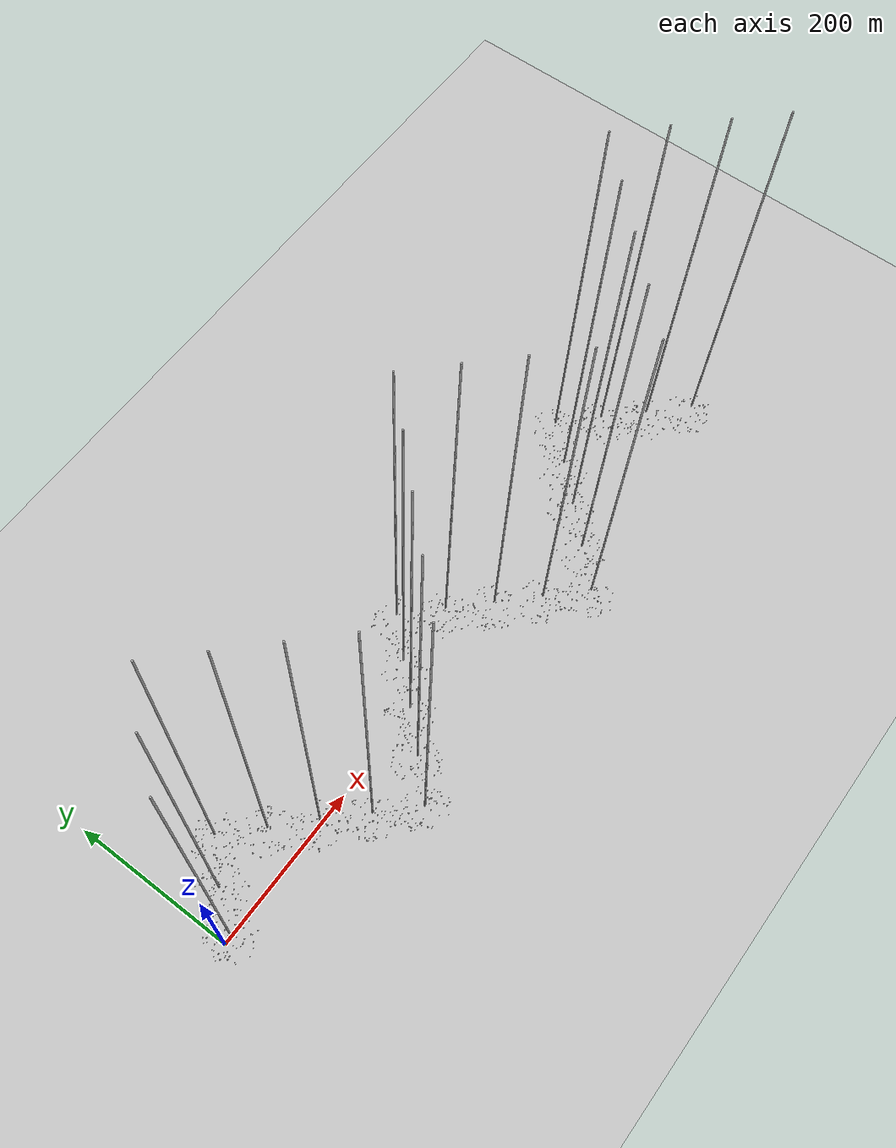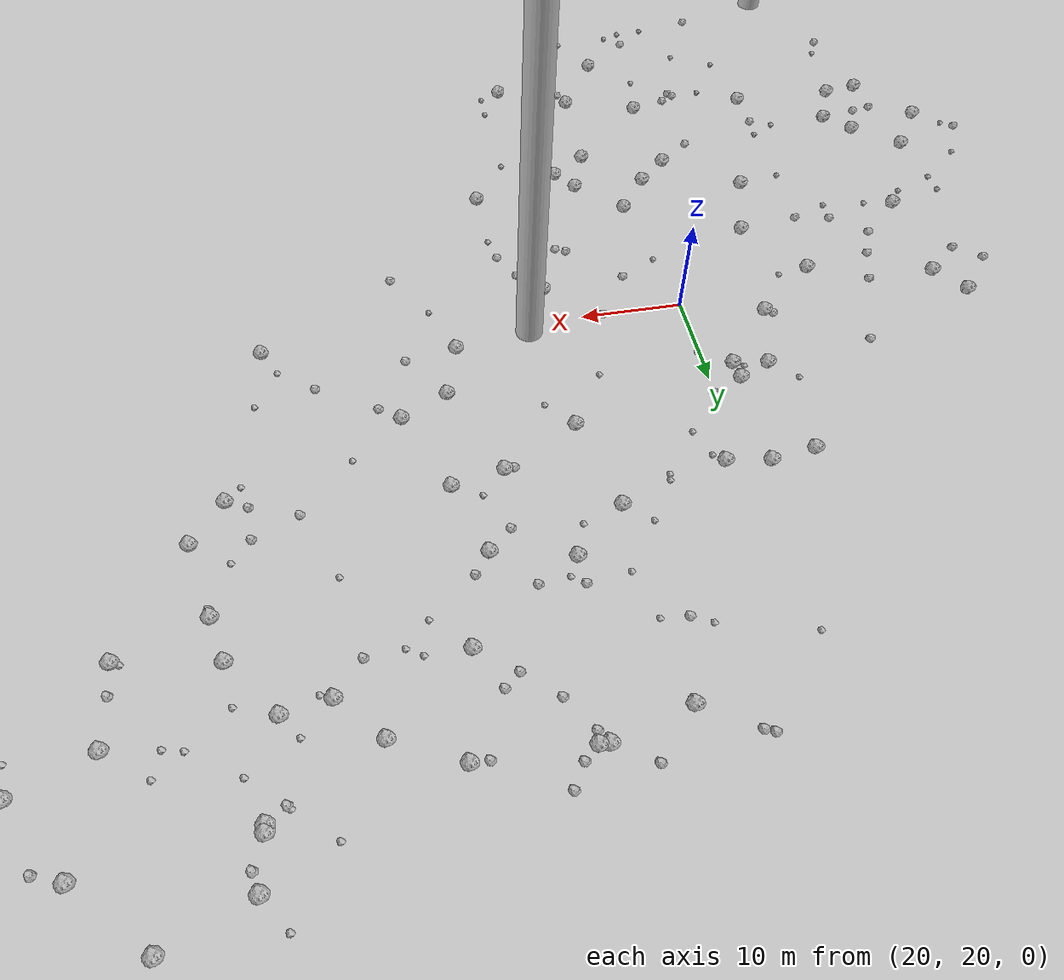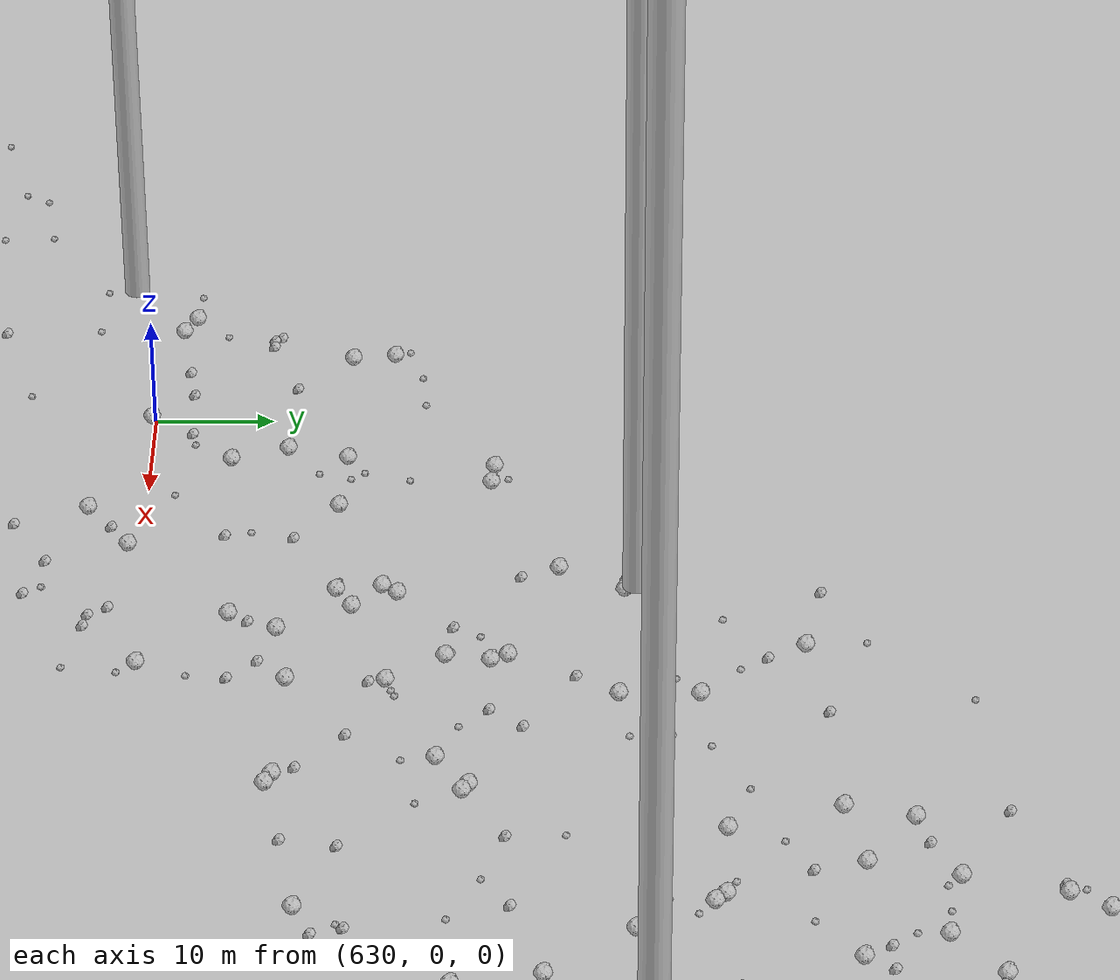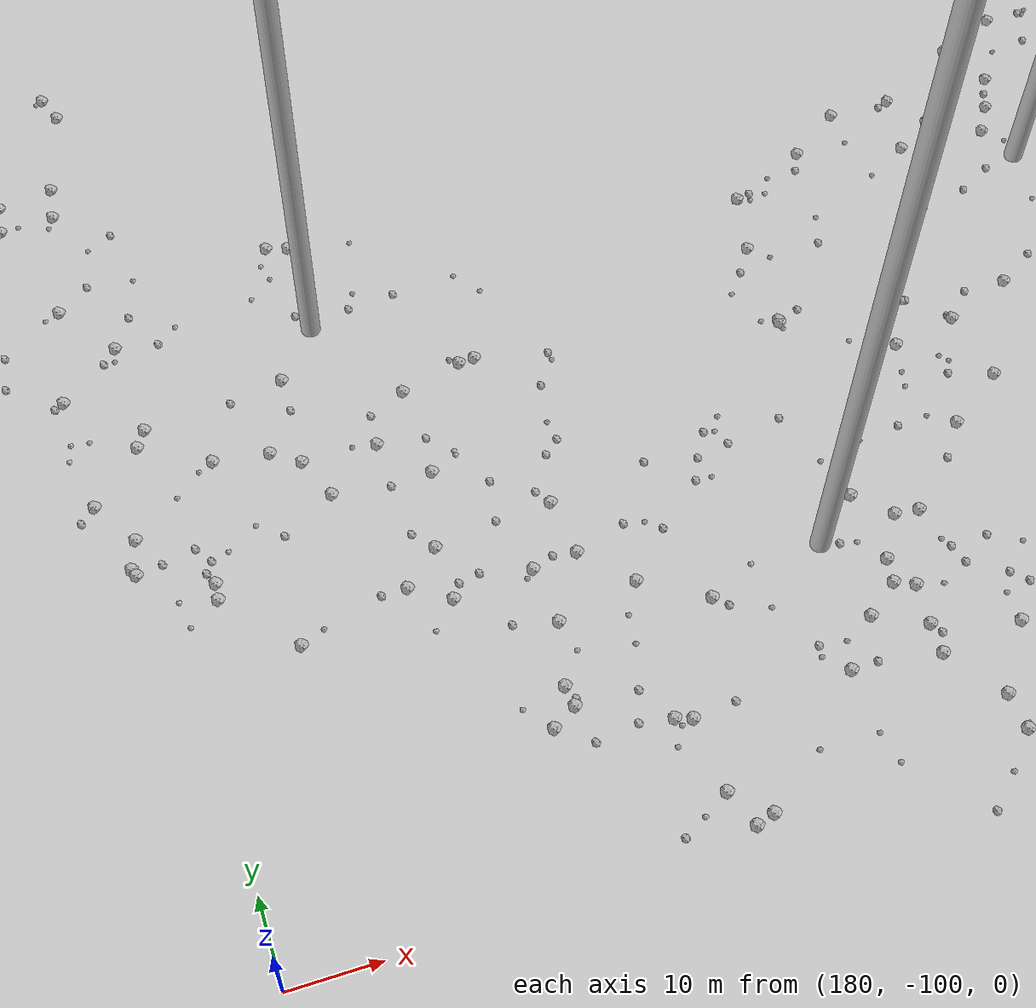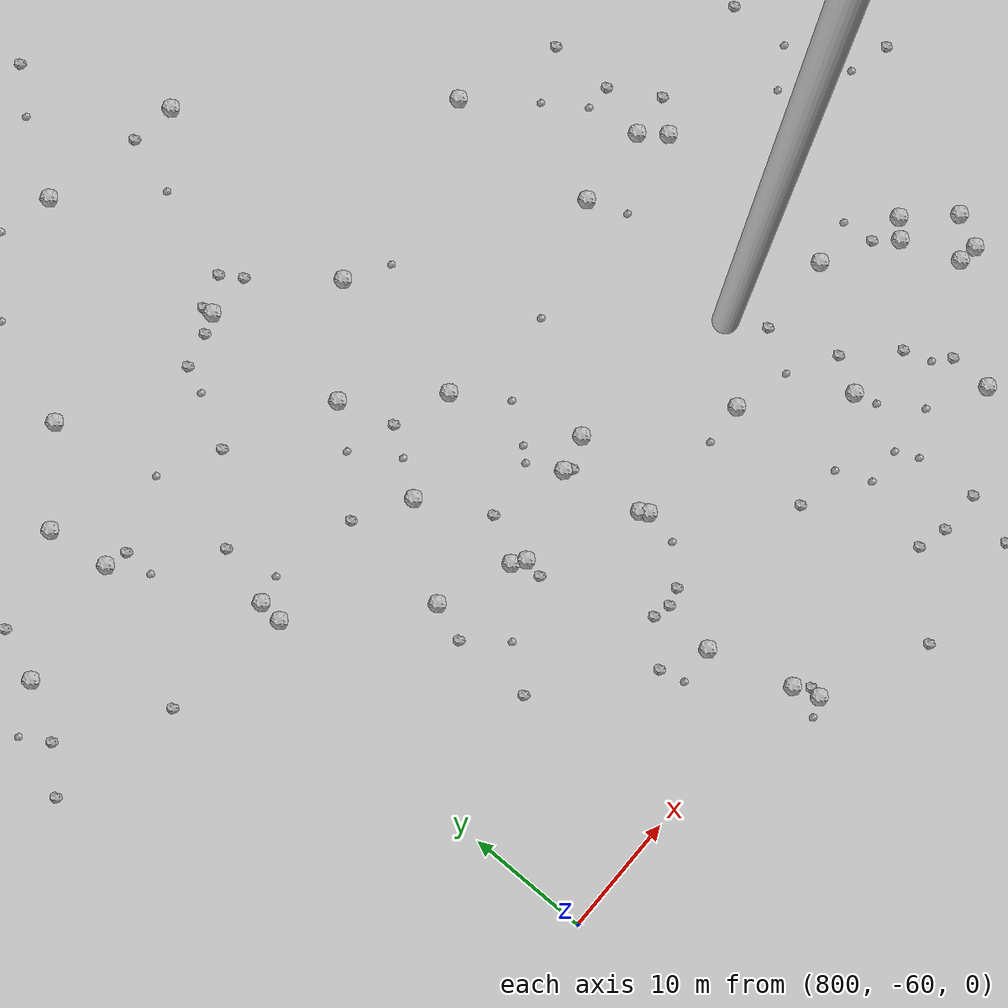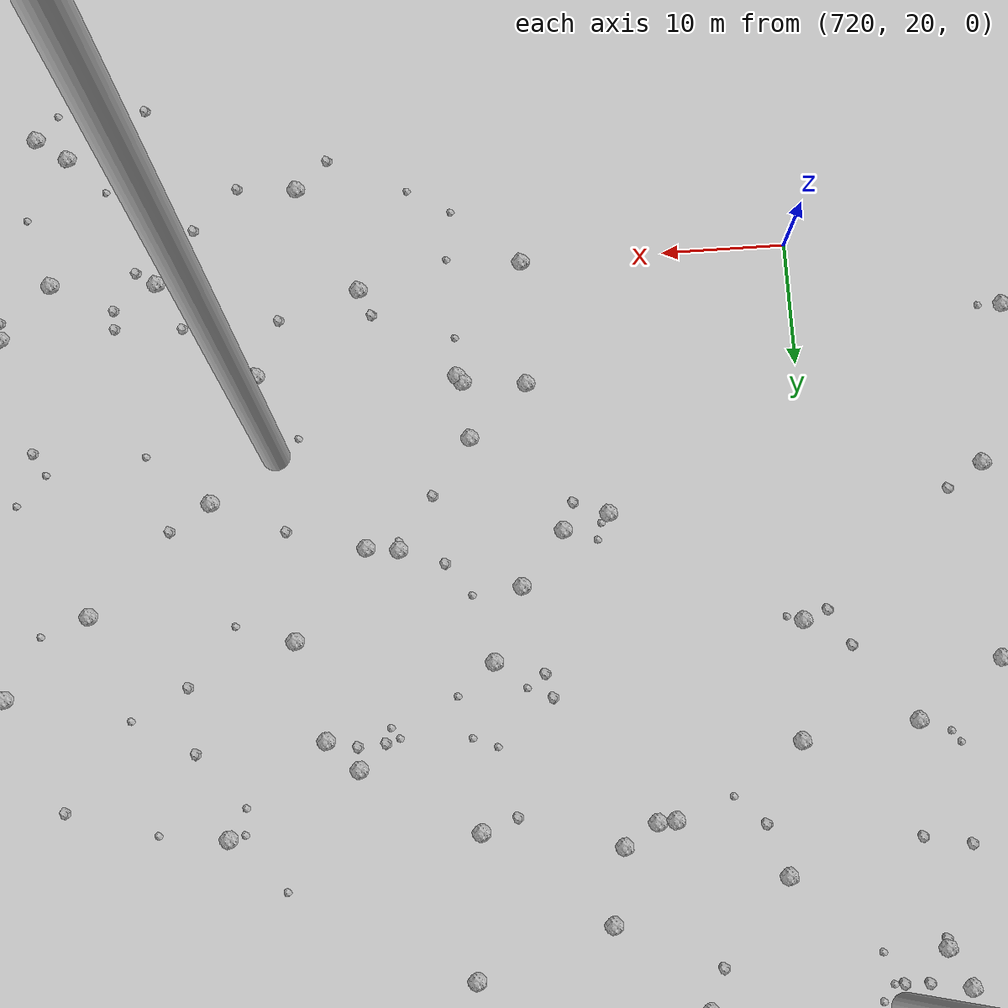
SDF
<sdf version="1.6">
 <world name="default">
  <include><uri>model://custom_ground</uri></include>
  <include><uri>model://sun</uri></include>
  <spherical_coordinates>
   <surface_model>EARTH_WGS84</surface_model>
   <latitude_deg>38.161479</latitude_deg>
   <longitude_deg>-122.454630</longitude_deg>
   <elevation>488.0</elevation>
   <heading_deg>90</heading_deg>
  </spherical_coordinates>
  <model name="rock1_0_0">
   <include><uri>model://rock1</uri><pose>-10.388747904983164 -11.75803176053617 0.5 0 0 0</pose></include>
  </model>
  <model name="rock1_0_1">
   <include><uri>model://rock1</uri><pose>26.428262382038966 0.5289827908445481 0.5 0 0 0</pose></include>
  </model>
  <model name="rock1_0_2">
   <include><uri>model://rock1</uri><pose>-4.687512336274619 -6.57455889378927 0.5 0 0 0</pose></include>
  </model>
  <model name="rock1_0_3">
   <include><uri>model://rock1</uri><pose>-15.140202449116567 -5.4696459528496 0.5 0 0 0</pose></include>
  </model>
  <model name="rock1_0_4">
   <include><uri>model://rock1</uri><pose>17.396998926052014 28.756112341361252 0.5 0 0 0</pose></include>
  </model>
  <model name="rock1_0_5">
   <include><uri>model://rock1</uri><pose>-6.800267446037278 -11.25413442466208 0.5 0 0 0</pose></include>
  </model>
  <model name="rock1_0_6">
   <include><uri>model://rock1</uri><pose>12.133424612152957 22.48349167656078 0.5 0 0 0</pose></include>
  </model>
  <model name="rock1_0_7">
   <include><uri>model://rock1</uri><pose>19.779112310787475 -21.36658829141027 0.5 0 0 0</pose></include>
  </model>
  <model name="rock1_0_8">
   <include><uri>model://rock1</uri><pose>10.686955683903506 10.445155333498334 0.5 0 0 0</pose></include>
  </model>
  <model name="rock1_0_9">
   <include><uri>model://rock1</uri><pose>-8.994138159872989 23.180514755637425 0.5 0 0 0</pose></include>
  </model>
  <model name="rock1_0_10">
   <include><uri>model://rock1</uri><pose>-6.607544439469423 19.97345108370984 0.5 0 0 0</pose></include>
  </model>
  <model name="rock1_0_11">
   <include><uri>model://rock1</uri><pose>4.04742348514845 -11.689524831275875 0.5 0 0 0</pose></include>
  </model>
  <model name="rock1_0_12">
   <include><uri>model://rock1</uri><pose>24.098524116641457 -14.523782246956635 0.5 0 0 0</pose></include>
  </model>
  <model name="rock1_0_13">
   <include><uri>model://rock1</uri><pose>33.1311247647336 15.71346973149489 0.5 0 0 0</pose></include>
  </model>
  <model name="rock1_0_14">
   <include><uri>model://rock1</uri><pose>-7.139792688241265 -3.9867166718749445 0.5 0 0 0</pose></include>
  </model>
  <model name="rock1_0_15">
   <include><uri>model://rock1</uri><pose>28.18695917645357 -1.8500782469272856 0.5 0 0 0</pose></include>
  </model>
  <model name="rock1_0_16">
   <include><uri>model://rock1</uri><pose>31.543551742745784 -17.95582542207713 0.5 0 0 0</pose></include>
  </model>
  <model name="rock1_0_17">
   <include><uri>model://rock1</uri><pose>22.01776538162138 4.846589527766703 0.5 0 0 0</pose></include>
  </model>
  <model name="rock1_0_18">
   <include><uri>model://rock1</uri><pose>5.881049681019178 17.33071280459115 0.5 0 0 0</pose></include>
  </model>
  <model name="rock1_0_19">
   <include><uri>model://rock1</uri><pose>-6.68777649148579 9.248225328289983 0.5 0 0 0</pose></include>
  </model>
  <model name="rock1_0_20">
   <include><uri>model://rock1</uri><pose>24.576468419778337 -4.298992718839838 0.5 0 0 0</pose></include>
  </model>
  <model name="rock1_0_21">
   <include><uri>model://rock1</uri><pose>-11.637312554168934 -0.3849603965866635 0.5 0 0 0</pose></include>
  </model>
  <model name="rock1_0_22">
   <include><uri>model://rock1</uri><pose>8.443942278029017 3.235490830580787 0.5 0 0 0</pose></include>
  </model>
  <model name="rock1_0_23">
   <include><uri>model://rock1</uri><pose>16.538188400855873 -12.082678243395975 0.5 0 0 0</pose></include>
  </model>
  <model name="rock1_0_24">
   <include><uri>model://rock1</uri><pose>15.842022060089825 -2.065789670940351 0.5 0 0 0</pose></include>
  </model>
  <model name="rock1_0_25">
   <include><uri>model://rock1</uri><pose>18.894740405846896 0.7224898964655075 0.5 0 0 0</pose></include>
  </model>
  <model name="rock1_0_26">
   <include><uri>model://rock1</uri><pose>37.360156037908986 0.8362163637808209 0.5 0 0 0</pose></include>
  </model>
  <model name="rock2_0_0">
   <include><uri>model://rock2</uri><pose>-2.48335766794899 13.176496202204618 0.3 0 0 0</pose></include>
  </model>
  <model name="rock2_0_1">
   <include><uri>model://rock2</uri><pose>-9.135345824955364 -21.549251496260435 0.3 0 0 0</pose></include>
  </model>
  <model name="rock2_0_2">
   <include><uri>model://rock2</uri><pose>27.968049566296955 20.125343193100747 0.3 0 0 0</pose></include>
  </model>
  <model name="rock2_0_3">
   <include><uri>model://rock2</uri><pose>11.753470882497762 -14.318229908479928 0.3 0 0 0</pose></include>
  </model>
  <model name="rock2_0_4">
   <include><uri>model://rock2</uri><pose>11.352432242472904 22.917475623809175 0.3 0 0 0</pose></include>
  </model>
  <model name="rock2_0_5">
   <include><uri>model://rock2</uri><pose>35.38269467032252 13.166544181129787 0.3 0 0 0</pose></include>
  </model>
  <model name="rock2_0_6">
   <include><uri>model://rock2</uri><pose>24.736947955771136 15.2258606241191 0.3 0 0 0</pose></include>
  </model>
  <model name="rock2_0_7">
   <include><uri>model://rock2</uri><pose>24.753173906994853 -16.316530106395852 0.3 0 0 0</pose></include>
  </model>
  <model name="rock2_0_8">
   <include><uri>model://rock2</uri><pose>36.84175377823139 10.223183091930416 0.3 0 0 0</pose></include>
  </model>
  <model name="rock2_0_9">
   <include><uri>model://rock2</uri><pose>5.724149485111187 -28.804782287077163 0.3 0 0 0</pose></include>
  </model>
  <model name="rock2_0_10">
   <include><uri>model://rock2</uri><pose>3.1752069843136894 28.000404603255916 0.3 0 0 0</pose></include>
  </model>
  <model name="rock2_0_11">
   <include><uri>model://rock2</uri><pose>-10.735102321734153 -7.642418152059243 0.3 0 0 0</pose></include>
  </model>
  <model name="rock2_0_12">
   <include><uri>model://rock2</uri><pose>4.3743250312621385 9.626996588856635 0.3 0 0 0</pose></include>
  </model>
  <model name="rock2_0_13">
   <include><uri>model://rock2</uri><pose>0.8054396402788342 10.3237151058242 0.3 0 0 0</pose></include>
  </model>
  <model name="rock2_0_14">
   <include><uri>model://rock2</uri><pose>0.09546570496425844 19.920204071222628 0.3 0 0 0</pose></include>
  </model>
  <model name="rock2_0_15">
   <include><uri>model://rock2</uri><pose>12.757498383344377 -13.031466540398664 0.3 0 0 0</pose></include>
  </model>
  <model name="rock2_0_16">
   <include><uri>model://rock2</uri><pose>-12.719772686165827 18.929981084769402 0.3 0 0 0</pose></include>
  </model>
  <model name="rock2_0_17">
   <include><uri>model://rock2</uri><pose>14.738109005402379 -25.3343123557817 0.3 0 0 0</pose></include>
  </model>
  <model name="rock2_0_18">
   <include><uri>model://rock2</uri><pose>30.657429251631285 10.023932910604763 0.3 0 0 0</pose></include>
  </model>
  <model name="rock2_0_19">
   <include><uri>model://rock2</uri><pose>29.62411639434665 10.526866022787942 0.3 0 0 0</pose></include>
  </model>
  <model name="rock2_0_20">
   <include><uri>model://rock2</uri><pose>12.412380838051163 -4.691962191002258 0.3 0 0 0</pose></include>
  </model>
  <model name="rock2_0_21">
   <include><uri>model://rock2</uri><pose>-8.691865414639423 -7.288307543662775 0.3 0 0 0</pose></include>
  </model>
  <model name="rock2_0_22">
   <include><uri>model://rock2</uri><pose>-10.188977615335926 17.019610160233228 0.3 0 0 0</pose></include>
  </model>
  <model name="rock2_0_23">
   <include><uri>model://rock2</uri><pose>3.844380535396617 -7.379986018884441 0.3 0 0 0</pose></include>
  </model>
  <model name="rock2_0_24">
   <include><uri>model://rock2</uri><pose>-19.02646104528288 -2.4821767406026076 0.3 0 0 0</pose></include>
  </model>
  <model name="rock2_0_25">
   <include><uri>model://rock2</uri><pose>-1.1210828850607086 16.24775452536545 0.3 0 0 0</pose></include>
  </model>
  <model name="rock2_0_26">
   <include><uri>model://rock2</uri><pose>11.35732054342746 -13.839691430678908 0.3 0 0 0</pose></include>
  </model>
  <model name="rock3_0_0">
   <include><uri>model://rock3</uri><pose>33.60692320551017 -4.51128651509725 0.2 0 0 0</pose></include>
  </model>
  <model name="rock3_0_1">
   <include><uri>model://rock3</uri><pose>33.637654086803465 -17.092726412005575 0.2 0 0 0</pose></include>
  </model>
  <model name="rock3_0_2">
   <include><uri>model://rock3</uri><pose>20.22570758149677 26.603557730200087 0.2 0 0 0</pose></include>
  </model>
  <model name="rock3_0_3">
   <include><uri>model://rock3</uri><pose>8.199370116060006 -14.085860900460967 0.2 0 0 0</pose></include>
  </model>
  <model name="rock3_0_4">
   <include><uri>model://rock3</uri><pose>37.276457188791476 7.553417459723171 0.2 0 0 0</pose></include>
  </model>
  <model name="rock3_0_5">
   <include><uri>model://rock3</uri><pose>14.521401971007997 -27.72829222927363 0.2 0 0 0</pose></include>
  </model>
  <model name="rock3_0_6">
   <include><uri>model://rock3</uri><pose>16.37912918818209 -27.043649828894427 0.2 0 0 0</pose></include>
  </model>
  <model name="rock3_0_7">
   <include><uri>model://rock3</uri><pose>4.90610303643567 -19.358584689670344 0.2 0 0 0</pose></include>
  </model>
  <model name="rock3_0_8">
   <include><uri>model://rock3</uri><pose>-8.272364650537378 7.262428727839854 0.2 0 0 0</pose></include>
  </model>
  <model name="rock3_0_9">
   <include><uri>model://rock3</uri><pose>3.9114331092266283 2.3941958361750295 0.2 0 0 0</pose></include>
  </model>
  <model name="rock3_0_10">
   <include><uri>model://rock3</uri><pose>0.6435302323815542 8.122182967236974 0.2 0 0 0</pose></include>
  </model>
  <model name="rock3_0_11">
   <include><uri>model://rock3</uri><pose>-12.604853073838004 7.756422742535321 0.2 0 0 0</pose></include>
  </model>
  <model name="rock3_0_12">
   <include><uri>model://rock3</uri><pose>-12.483770389723489 5.567131824466628 0.2 0 0 0</pose></include>
  </model>
  <model name="rock3_0_13">
   <include><uri>model://rock3</uri><pose>20.949178874789332 13.212131497524446 0.2 0 0 0</pose></include>
  </model>
  <model name="rock3_0_14">
   <include><uri>model://rock3</uri><pose>-8.16030923437204 -19.460036112776425 0.2 0 0 0</pose></include>
  </model>
  <model name="rock3_0_15">
   <include><uri>model://rock3</uri><pose>-17.858878025979852 -3.39003467606274 0.2 0 0 0</pose></include>
  </model>
  <model name="rock3_0_16">
   <include><uri>model://rock3</uri><pose>8.89659104143131 17.65196899244198 0.2 0 0 0</pose></include>
  </model>
  <model name="rock3_0_17">
   <include><uri>model://rock3</uri><pose>33.724491893601005 -14.23653387824064 0.2 0 0 0</pose></include>
  </model>
  <model name="rock3_0_18">
   <include><uri>model://rock3</uri><pose>1.5252659496282135 -6.516399359224238 0.2 0 0 0</pose></include>
  </model>
  <model name="rock3_0_19">
   <include><uri>model://rock3</uri><pose>22.26837193818728 -26.624745085604406 0.2 0 0 0</pose></include>
  </model>
  <model name="rock3_0_20">
   <include><uri>model://rock3</uri><pose>15.420024129699335 -17.327683377478344 0.2 0 0 0</pose></include>
  </model>
  <model name="rock3_0_21">
   <include><uri>model://rock3</uri><pose>-3.806378317159613 8.588758775163726 0.2 0 0 0</pose></include>
  </model>
  <model name="rock3_0_22">
   <include><uri>model://rock3</uri><pose>4.004641145440946 -5.116407170733559 0.2 0 0 0</pose></include>
  </model>
  <model name="rock3_0_23">
   <include><uri>model://rock3</uri><pose>33.20404735859003 14.114063991303311 0.2 0 0 0</pose></include>
  </model>
  <model name="rock3_0_24">
   <include><uri>model://rock3</uri><pose>9.258263041280898 -21.61858657373358 0.2 0 0 0</pose></include>
  </model>
  <model name="rock3_0_25">
   <include><uri>model://rock3</uri><pose>11.588298900384796 -27.955328857138774 0.2 0 0 0</pose></include>
  </model>
  <model name="rock3_0_26">
   <include><uri>model://rock3</uri><pose>-16.904761398304295 1.8536939798140963 0.2 0 0 0</pose></include>
  </model>
  <model name="rock1_1_0">
   <include><uri>model://rock1</uri><pose>68.86707073005306 40.67518506492202 0.5 0 0 0</pose></include>
  </model>
  <model name="rock1_1_1">
   <include><uri>model://rock1</uri><pose>36.832307850097976 47.555624932210385 0.5 0 0 0</pose></include>
  </model>
  <model name="rock1_1_2">
   <include><uri>model://rock1</uri><pose>31.039366786989095 62.305674150134 0.5 0 0 0</pose></include>
  </model>
  <model name="rock1_1_3">
   <include><uri>model://rock1</uri><pose>41.17177822464833 37.487025055570335 0.5 0 0 0</pose></include>
  </model>
  <model name="rock1_1_4">
   <include><uri>model://rock1</uri><pose>62.41902395216529 57.62793429632176 0.5 0 0 0</pose></include>
  </model>
  <model name="rock1_1_5">
   <include><uri>model://rock1</uri><pose>31.850116128569933 43.06399709171719 0.5 0 0 0</pose></include>
  </model>
  <model name="rock1_1_6">
   <include><uri>model://rock1</uri><pose>39.02813187615417 64.20103710788784 0.5 0 0 0</pose></include>
  </model>
  <model name="rock1_1_7">
   <include><uri>model://rock1</uri><pose>21.619466202692937 39.99528795350243 0.5 0 0 0</pose></include>
  </model>
  <model name="rock1_1_8">
   <include><uri>model://rock1</uri><pose>54.62933737020865 60.99005955075388 0.5 0 0 0</pose></include>
  </model>
  <model name="rock1_1_9">
   <include><uri>model://rock1</uri><pose>67.33313792336972 48.07908968569305 0.5 0 0 0</pose></include>
  </model>
  <model name="rock1_1_10">
   <include><uri>model://rock1</uri><pose>65.70093818631064 36.712666774755675 0.5 0 0 0</pose></include>
  </model>
  <model name="rock1_1_11">
   <include><uri>model://rock1</uri><pose>48.78894254405693 63.957164584078505 0.5 0 0 0</pose></include>
  </model>
  <model name="rock1_1_12">
   <include><uri>model://rock1</uri><pose>13.24025744925475 40.045438085088705 0.5 0 0 0</pose></include>
  </model>
  <model name="rock1_1_13">
   <include><uri>model://rock1</uri><pose>14.081920271976927 29.29056971825021 0.5 0 0 0</pose></include>
  </model>
  <model name="rock1_1_14">
   <include><uri>model://rock1</uri><pose>61.6081331499886 19.585035640748778 0.5 0 0 0</pose></include>
  </model>
  <model name="rock1_1_15">
   <include><uri>model://rock1</uri><pose>46.11241973549476 38.49244114396123 0.5 0 0 0</pose></include>
  </model>
  <model name="rock1_1_16">
   <include><uri>model://rock1</uri><pose>17.547277668457507 40.642705893367605 0.5 0 0 0</pose></include>
  </model>
  <model name="rock1_1_17">
   <include><uri>model://rock1</uri><pose>46.95688783816979 54.56910926811544 0.5 0 0 0</pose></include>
  </model>
  <model name="rock1_1_18">
   <include><uri>model://rock1</uri><pose>38.17607163481185 64.25573933985591 0.5 0 0 0</pose></include>
  </model>
  <model name="rock1_1_19">
   <include><uri>model://rock1</uri><pose>44.8132472984317 27.800147172651577 0.5 0 0 0</pose></include>
  </model>
  <model name="rock1_1_20">
   <include><uri>model://rock1</uri><pose>33.832799702484515 33.54151893815562 0.5 0 0 0</pose></include>
  </model>
  <model name="rock1_1_21">
   <include><uri>model://rock1</uri><pose>44.04441025643924 45.8137206461908 0.5 0 0 0</pose></include>
  </model>
  <model name="rock1_1_22">
   <include><uri>model://rock1</uri><pose>49.39376386452156 30.050667819247398 0.5 0 0 0</pose></include>
  </model>
  <model name="rock1_1_23">
   <include><uri>model://rock1</uri><pose>17.194614799920434 30.671890562451672 0.5 0 0 0</pose></include>
  </model>
  <model name="rock1_1_24">
   <include><uri>model://rock1</uri><pose>58.20413804266443 56.94054345962245 0.5 0 0 0</pose></include>
  </model>
  <model name="rock1_1_25">
   <include><uri>model://rock1</uri><pose>43.06063975976842 22.190261546993266 0.5 0 0 0</pose></include>
  </model>
  <model name="rock1_1_26">
   <include><uri>model://rock1</uri><pose>66.37218281731506 52.31597738099293 0.5 0 0 0</pose></include>
  </model>
  <model name="rock2_1_0">
   <include><uri>model://rock2</uri><pose>41.80046795470574 43.76703440922115 0.3 0 0 0</pose></include>
  </model>
  <model name="rock2_1_1">
   <include><uri>model://rock2</uri><pose>26.45860240154682 65.17633006852435 0.3 0 0 0</pose></include>
  </model>
  <model name="rock2_1_2">
   <include><uri>model://rock2</uri><pose>34.84565755198241 66.41589142192416 0.3 0 0 0</pose></include>
  </model>
  <model name="rock2_1_3">
   <include><uri>model://rock2</uri><pose>48.12795375596467 11.708249549667155 0.3 0 0 0</pose></include>
  </model>
  <model name="rock2_1_4">
   <include><uri>model://rock2</uri><pose>25.639209498188894 65.55300078343447 0.3 0 0 0</pose></include>
  </model>
  <model name="rock2_1_5">
   <include><uri>model://rock2</uri><pose>40.61860067815161 49.65922166207845 0.3 0 0 0</pose></include>
  </model>
  <model name="rock2_1_6">
   <include><uri>model://rock2</uri><pose>63.736130116594644 37.640766351609514 0.3 0 0 0</pose></include>
  </model>
  <model name="rock2_1_7">
   <include><uri>model://rock2</uri><pose>56.88656598756457 25.02587428057758 0.3 0 0 0</pose></include>
  </model>
  <model name="rock2_1_8">
   <include><uri>model://rock2</uri><pose>40.822985311788585 59.9167784844668 0.3 0 0 0</pose></include>
  </model>
  <model name="rock2_1_9">
   <include><uri>model://rock2</uri><pose>45.58075217095807 47.83401628011297 0.3 0 0 0</pose></include>
  </model>
  <model name="rock2_1_10">
   <include><uri>model://rock2</uri><pose>41.63455769653645 67.3433757174345 0.3 0 0 0</pose></include>
  </model>
  <model name="rock2_1_11">
   <include><uri>model://rock2</uri><pose>29.16969216361545 54.76318119009631 0.3 0 0 0</pose></include>
  </model>
  <model name="rock2_1_12">
   <include><uri>model://rock2</uri><pose>54.45652611124653 60.76469447773972 0.3 0 0 0</pose></include>
  </model>
  <model name="rock2_1_13">
   <include><uri>model://rock2</uri><pose>55.57022516211783 53.87212765127677 0.3 0 0 0</pose></include>
  </model>
  <model name="rock2_1_14">
   <include><uri>model://rock2</uri><pose>40.241391560122345 37.38945719496432 0.3 0 0 0</pose></include>
  </model>
  <model name="rock2_1_15">
   <include><uri>model://rock2</uri><pose>59.408515667859604 39.204655579983886 0.3 0 0 0</pose></include>
  </model>
  <model name="rock2_1_16">
   <include><uri>model://rock2</uri><pose>36.689900373591755 50.25268790116857 0.3 0 0 0</pose></include>
  </model>
  <model name="rock2_1_17">
   <include><uri>model://rock2</uri><pose>38.85146503254174 63.059216456568436 0.3 0 0 0</pose></include>
  </model>
  <model name="rock2_1_18">
   <include><uri>model://rock2</uri><pose>43.65858676533174 57.218186906086785 0.3 0 0 0</pose></include>
  </model>
  <model name="rock2_1_19">
   <include><uri>model://rock2</uri><pose>20.247144250536202 31.98894326808796 0.3 0 0 0</pose></include>
  </model>
  <model name="rock2_1_20">
   <include><uri>model://rock2</uri><pose>63.65210685805894 41.04963711350064 0.3 0 0 0</pose></include>
  </model>
  <model name="rock2_1_21">
   <include><uri>model://rock2</uri><pose>67.40607813021407 47.354562770436765 0.3 0 0 0</pose></include>
  </model>
  <model name="rock2_1_22">
   <include><uri>model://rock2</uri><pose>47.23219175366763 63.985612149386945 0.3 0 0 0</pose></include>
  </model>
  <model name="rock2_1_23">
   <include><uri>model://rock2</uri><pose>51.32750921354643 28.512633669534445 0.3 0 0 0</pose></include>
  </model>
  <model name="rock2_1_24">
   <include><uri>model://rock2</uri><pose>45.095622646337574 58.42158795584419 0.3 0 0 0</pose></include>
  </model>
  <model name="rock2_1_25">
   <include><uri>model://rock2</uri><pose>48.0887145995578 22.990120106693333 0.3 0 0 0</pose></include>
  </model>
  <model name="rock2_1_26">
   <include><uri>model://rock2</uri><pose>40.36769114280588 65.2898586063657 0.3 0 0 0</pose></include>
  </model>
  <model name="rock3_1_0">
   <include><uri>model://rock3</uri><pose>56.65070165364878 46.0206759877939 0.2 0 0 0</pose></include>
  </model>
  <model name="rock3_1_1">
   <include><uri>model://rock3</uri><pose>27.39131147754582 55.60033849843785 0.2 0 0 0</pose></include>
  </model>
  <model name="rock3_1_2">
   <include><uri>model://rock3</uri><pose>49.95630936100047 51.34386376250071 0.2 0 0 0</pose></include>
  </model>
  <model name="rock3_1_3">
   <include><uri>model://rock3</uri><pose>11.63198161410923 31.481408690876652 0.2 0 0 0</pose></include>
  </model>
  <model name="rock3_1_4">
   <include><uri>model://rock3</uri><pose>44.89478777629532 16.828502027829607 0.2 0 0 0</pose></include>
  </model>
  <model name="rock3_1_5">
   <include><uri>model://rock3</uri><pose>26.956428881033197 41.114053060031324 0.2 0 0 0</pose></include>
  </model>
  <model name="rock3_1_6">
   <include><uri>model://rock3</uri><pose>36.06702644786638 30.635381306887275 0.2 0 0 0</pose></include>
  </model>
  <model name="rock3_1_7">
   <include><uri>model://rock3</uri><pose>65.43169447331306 43.06573814557034 0.2 0 0 0</pose></include>
  </model>
  <model name="rock3_1_8">
   <include><uri>model://rock3</uri><pose>30.172415365972952 27.846834941956374 0.2 0 0 0</pose></include>
  </model>
  <model name="rock3_1_9">
   <include><uri>model://rock3</uri><pose>43.489635878631034 39.840753748973626 0.2 0 0 0</pose></include>
  </model>
  <model name="rock3_1_10">
   <include><uri>model://rock3</uri><pose>16.314909550806497 29.147551948005123 0.2 0 0 0</pose></include>
  </model>
  <model name="rock3_1_11">
   <include><uri>model://rock3</uri><pose>31.57470082483873 54.455784623161335 0.2 0 0 0</pose></include>
  </model>
  <model name="rock3_1_12">
   <include><uri>model://rock3</uri><pose>59.20451717933663 56.39285841558835 0.2 0 0 0</pose></include>
  </model>
  <model name="rock3_1_13">
   <include><uri>model://rock3</uri><pose>19.16531939705252 57.79096025389334 0.2 0 0 0</pose></include>
  </model>
  <model name="rock3_1_14">
   <include><uri>model://rock3</uri><pose>60.223102070575216 22.29214926705997 0.2 0 0 0</pose></include>
  </model>
  <model name="rock3_1_15">
   <include><uri>model://rock3</uri><pose>62.575759365552166 26.178828668724396 0.2 0 0 0</pose></include>
  </model>
  <model name="rock3_1_16">
   <include><uri>model://rock3</uri><pose>54.305407464750594 34.03668762622668 0.2 0 0 0</pose></include>
  </model>
  <model name="rock3_1_17">
   <include><uri>model://rock3</uri><pose>26.810861832624134 40.49610318280122 0.2 0 0 0</pose></include>
  </model>
  <model name="rock3_1_18">
   <include><uri>model://rock3</uri><pose>23.468574181212464 36.16494886966381 0.2 0 0 0</pose></include>
  </model>
  <model name="rock3_1_19">
   <include><uri>model://rock3</uri><pose>32.70475302907026 49.722543382165505 0.2 0 0 0</pose></include>
  </model>
  <model name="rock3_1_20">
   <include><uri>model://rock3</uri><pose>50.818505275448615 54.43798092188112 0.2 0 0 0</pose></include>
  </model>
  <model name="rock3_1_21">
   <include><uri>model://rock3</uri><pose>29.474450593546344 45.06528727456519 0.2 0 0 0</pose></include>
  </model>
  <model name="rock3_1_22">
   <include><uri>model://rock3</uri><pose>22.476531061799893 39.067461814206446 0.2 0 0 0</pose></include>
  </model>
  <model name="rock3_1_23">
   <include><uri>model://rock3</uri><pose>64.24196257667512 35.253377358268565 0.2 0 0 0</pose></include>
  </model>
  <model name="rock3_1_24">
   <include><uri>model://rock3</uri><pose>35.55071664037561 44.34564686590964 0.2 0 0 0</pose></include>
  </model>
  <model name="rock3_1_25">
   <include><uri>model://rock3</uri><pose>37.78966320353042 49.319244621638674 0.2 0 0 0</pose></include>
  </model>
  <model name="rock3_1_26">
   <include><uri>model://rock3</uri><pose>52.148035954996395 53.58721743747055 0.2 0 0 0</pose></include>
  </model>
  <model name="rock1_2_0">
   <include><uri>model://rock1</uri><pose>84.4896691033855 98.67513482836813 0.5 0 0 0</pose></include>
  </model>
  <model name="rock1_2_1">
   <include><uri>model://rock1</uri><pose>100.30958028738085 67.65202745664047 0.5 0 0 0</pose></include>
  </model>
  <model name="rock1_2_2">
   <include><uri>model://rock1</uri><pose>66.0933190787478 101.91978218834072 0.5 0 0 0</pose></include>
  </model>
  <model name="rock1_2_3">
   <include><uri>model://rock1</uri><pose>63.94880201473433 65.95382990052802 0.5 0 0 0</pose></include>
  </model>
  <model name="rock1_2_4">
   <include><uri>model://rock1</uri><pose>64.64798941107775 70.81478555967513 0.5 0 0 0</pose></include>
  </model>
  <model name="rock1_2_5">
   <include><uri>model://rock1</uri><pose>69.81340980668907 92.08085228162386 0.5 0 0 0</pose></include>
  </model>
  <model name="rock1_2_6">
   <include><uri>model://rock1</uri><pose>92.3438026194074 60.645687586900344 0.5 0 0 0</pose></include>
  </model>
  <model name="rock1_2_7">
   <include><uri>model://rock1</uri><pose>100.84906316510816 87.2251183909228 0.5 0 0 0</pose></include>
  </model>
  <model name="rock1_2_8">
   <include><uri>model://rock1</uri><pose>83.41385038547887 108.20822815729952 0.5 0 0 0</pose></include>
  </model>
  <model name="rock1_2_9">
   <include><uri>model://rock1</uri><pose>82.63090913269298 60.74619700801999 0.5 0 0 0</pose></include>
  </model>
  <model name="rock1_2_10">
   <include><uri>model://rock1</uri><pose>89.36333143939183 57.921920371847605 0.5 0 0 0</pose></include>
  </model>
  <model name="rock1_2_11">
   <include><uri>model://rock1</uri><pose>100.51259819171841 78.7232411863968 0.5 0 0 0</pose></include>
  </model>
  <model name="rock1_2_12">
   <include><uri>model://rock1</uri><pose>84.75095814721266 65.7737975665834 0.5 0 0 0</pose></include>
  </model>
  <model name="rock1_2_13">
   <include><uri>model://rock1</uri><pose>103.12549750835271 83.45397701427595 0.5 0 0 0</pose></include>
  </model>
  <model name="rock1_2_14">
   <include><uri>model://rock1</uri><pose>75.82252598360012 58.153712269157104 0.5 0 0 0</pose></include>
  </model>
  <model name="rock1_2_15">
   <include><uri>model://rock1</uri><pose>88.48964072975815 79.25285480673581 0.5 0 0 0</pose></include>
  </model>
  <model name="rock1_2_16">
   <include><uri>model://rock1</uri><pose>100.8835586650763 66.54118241095199 0.5 0 0 0</pose></include>
  </model>
  <model name="rock1_2_17">
   <include><uri>model://rock1</uri><pose>77.87022255748576 67.66516466493614 0.5 0 0 0</pose></include>
  </model>
  <model name="rock1_2_18">
   <include><uri>model://rock1</uri><pose>64.4791466938231 86.21884474989069 0.5 0 0 0</pose></include>
  </model>
  <model name="rock1_2_19">
   <include><uri>model://rock1</uri><pose>64.00415976039156 66.52542758666084 0.5 0 0 0</pose></include>
  </model>
  <model name="rock1_2_20">
   <include><uri>model://rock1</uri><pose>50.42866309953781 84.2163635755254 0.5 0 0 0</pose></include>
  </model>
  <model name="rock1_2_21">
   <include><uri>model://rock1</uri><pose>68.06839854621364 99.51782812328874 0.5 0 0 0</pose></include>
  </model>
  <model name="rock1_2_22">
   <include><uri>model://rock1</uri><pose>87.35680879989083 83.04897969529713 0.5 0 0 0</pose></include>
  </model>
  <model name="rock1_2_23">
   <include><uri>model://rock1</uri><pose>100.02742616245656 70.89444815074978 0.5 0 0 0</pose></include>
  </model>
  <model name="rock1_2_24">
   <include><uri>model://rock1</uri><pose>73.94631969342956 104.05388242126257 0.5 0 0 0</pose></include>
  </model>
  <model name="rock1_2_25">
   <include><uri>model://rock1</uri><pose>71.83495061178382 73.63640990633226 0.5 0 0 0</pose></include>
  </model>
  <model name="rock1_2_26">
   <include><uri>model://rock1</uri><pose>75.18305550655965 50.81491127866318 0.5 0 0 0</pose></include>
  </model>
  <model name="rock2_2_0">
   <include><uri>model://rock2</uri><pose>74.07109723773885 94.16411328358265 0.3 0 0 0</pose></include>
  </model>
  <model name="rock2_2_1">
   <include><uri>model://rock2</uri><pose>79.02351064808552 82.82627405589838 0.3 0 0 0</pose></include>
  </model>
  <model name="rock2_2_2">
   <include><uri>model://rock2</uri><pose>96.64425307473905 60.42079749545498 0.3 0 0 0</pose></include>
  </model>
  <model name="rock2_2_3">
   <include><uri>model://rock2</uri><pose>62.309230242596634 64.76787283066561 0.3 0 0 0</pose></include>
  </model>
  <model name="rock2_2_4">
   <include><uri>model://rock2</uri><pose>65.21790053251019 99.34821711959685 0.3 0 0 0</pose></include>
  </model>
  <model name="rock2_2_5">
   <include><uri>model://rock2</uri><pose>53.80423489247655 88.56732445047007 0.3 0 0 0</pose></include>
  </model>
  <model name="rock2_2_6">
   <include><uri>model://rock2</uri><pose>76.13613367502803 102.07253007823229 0.3 0 0 0</pose></include>
  </model>
  <model name="rock2_2_7">
   <include><uri>model://rock2</uri><pose>53.37314376462622 91.56179749101162 0.3 0 0 0</pose></include>
  </model>
  <model name="rock2_2_8">
   <include><uri>model://rock2</uri><pose>58.3636898768737 78.54390331970659 0.3 0 0 0</pose></include>
  </model>
  <model name="rock2_2_9">
   <include><uri>model://rock2</uri><pose>65.97849874135606 88.34118160687163 0.3 0 0 0</pose></include>
  </model>
  <model name="rock2_2_10">
   <include><uri>model://rock2</uri><pose>82.08614929341582 106.1425750626598 0.3 0 0 0</pose></include>
  </model>
  <model name="rock2_2_11">
   <include><uri>model://rock2</uri><pose>75.32113528134576 53.66998456713071 0.3 0 0 0</pose></include>
  </model>
  <model name="rock2_2_12">
   <include><uri>model://rock2</uri><pose>80.28821329721116 66.65127851562104 0.3 0 0 0</pose></include>
  </model>
  <model name="rock2_2_13">
   <include><uri>model://rock2</uri><pose>53.44977752211649 92.88834734865023 0.3 0 0 0</pose></include>
  </model>
  <model name="rock2_2_14">
   <include><uri>model://rock2</uri><pose>91.61666443323811 76.14809590789231 0.3 0 0 0</pose></include>
  </model>
  <model name="rock2_2_15">
   <include><uri>model://rock2</uri><pose>89.97980293363045 99.07342846853176 0.3 0 0 0</pose></include>
  </model>
  <model name="rock2_2_16">
   <include><uri>model://rock2</uri><pose>107.61588661119357 90.04791942948879 0.3 0 0 0</pose></include>
  </model>
  <model name="rock2_2_17">
   <include><uri>model://rock2</uri><pose>91.86835598475588 92.2416489794793 0.3 0 0 0</pose></include>
  </model>
  <model name="rock2_2_18">
   <include><uri>model://rock2</uri><pose>94.62716800588731 68.68838679677879 0.3 0 0 0</pose></include>
  </model>
  <model name="rock2_2_19">
   <include><uri>model://rock2</uri><pose>87.51288482793677 76.2557217158091 0.3 0 0 0</pose></include>
  </model>
  <model name="rock2_2_20">
   <include><uri>model://rock2</uri><pose>90.3507464275244 102.96864884115146 0.3 0 0 0</pose></include>
  </model>
  <model name="rock2_2_21">
   <include><uri>model://rock2</uri><pose>65.07292556993093 69.07467272667911 0.3 0 0 0</pose></include>
  </model>
  <model name="rock2_2_22">
   <include><uri>model://rock2</uri><pose>78.33358761673665 98.9959804691872 0.3 0 0 0</pose></include>
  </model>
  <model name="rock2_2_23">
   <include><uri>model://rock2</uri><pose>63.56549656216742 93.82961897111537 0.3 0 0 0</pose></include>
  </model>
  <model name="rock2_2_24">
   <include><uri>model://rock2</uri><pose>61.06295357524569 87.63870914058863 0.3 0 0 0</pose></include>
  </model>
  <model name="rock2_2_25">
   <include><uri>model://rock2</uri><pose>62.96955120096183 81.75880548569425 0.3 0 0 0</pose></include>
  </model>
  <model name="rock2_2_26">
   <include><uri>model://rock2</uri><pose>87.24091569718368 102.82779182690376 0.3 0 0 0</pose></include>
  </model>
  <model name="rock3_2_0">
   <include><uri>model://rock3</uri><pose>82.8776351475265 57.84828346332538 0.2 0 0 0</pose></include>
  </model>
  <model name="rock3_2_1">
   <include><uri>model://rock3</uri><pose>69.55727799820747 59.183652526231754 0.2 0 0 0</pose></include>
  </model>
  <model name="rock3_2_2">
   <include><uri>model://rock3</uri><pose>62.03789578410789 65.00720652134582 0.2 0 0 0</pose></include>
  </model>
  <model name="rock3_2_3">
   <include><uri>model://rock3</uri><pose>96.49055795084271 62.66459762629018 0.2 0 0 0</pose></include>
  </model>
  <model name="rock3_2_4">
   <include><uri>model://rock3</uri><pose>54.80358067697398 84.20303466293143 0.2 0 0 0</pose></include>
  </model>
  <model name="rock3_2_5">
   <include><uri>model://rock3</uri><pose>62.71484840344077 73.6367058512524 0.2 0 0 0</pose></include>
  </model>
  <model name="rock3_2_6">
   <include><uri>model://rock3</uri><pose>74.44539336708928 51.03942680218542 0.2 0 0 0</pose></include>
  </model>
  <model name="rock3_2_7">
   <include><uri>model://rock3</uri><pose>56.29830438657713 80.06680201398436 0.2 0 0 0</pose></include>
  </model>
  <model name="rock3_2_8">
   <include><uri>model://rock3</uri><pose>58.72765171736843 68.00390017929028 0.2 0 0 0</pose></include>
  </model>
  <model name="rock3_2_9">
   <include><uri>model://rock3</uri><pose>65.27064669179991 62.04996839227 0.2 0 0 0</pose></include>
  </model>
  <model name="rock3_2_10">
   <include><uri>model://rock3</uri><pose>64.46071867799947 85.8738276798739 0.2 0 0 0</pose></include>
  </model>
  <model name="rock3_2_11">
   <include><uri>model://rock3</uri><pose>60.92891605253299 59.662135912102 0.2 0 0 0</pose></include>
  </model>
  <model name="rock3_2_12">
   <include><uri>model://rock3</uri><pose>65.87577196265867 56.244362385756254 0.2 0 0 0</pose></include>
  </model>
  <model name="rock3_2_13">
   <include><uri>model://rock3</uri><pose>65.19396240066432 93.56592497461057 0.2 0 0 0</pose></include>
  </model>
  <model name="rock3_2_14">
   <include><uri>model://rock3</uri><pose>73.45887264102487 85.36903046909197 0.2 0 0 0</pose></include>
  </model>
  <model name="rock3_2_15">
   <include><uri>model://rock3</uri><pose>68.35875004095317 94.75137470224524 0.2 0 0 0</pose></include>
  </model>
  <model name="rock3_2_16">
   <include><uri>model://rock3</uri><pose>94.4882853583392 100.82752953080698 0.2 0 0 0</pose></include>
  </model>
  <model name="rock3_2_17">
   <include><uri>model://rock3</uri><pose>80.86200239633173 88.63077174829561 0.2 0 0 0</pose></include>
  </model>
  <model name="rock3_2_18">
   <include><uri>model://rock3</uri><pose>74.97320666903943 92.80128314020985 0.2 0 0 0</pose></include>
  </model>
  <model name="rock3_2_19">
   <include><uri>model://rock3</uri><pose>97.82013170292282 57.73920779896244 0.2 0 0 0</pose></include>
  </model>
  <model name="rock3_2_20">
   <include><uri>model://rock3</uri><pose>103.11456370182017 75.26663869076752 0.2 0 0 0</pose></include>
  </model>
  <model name="rock3_2_21">
   <include><uri>model://rock3</uri><pose>106.63816366483522 76.10020867054311 0.2 0 0 0</pose></include>
  </model>
  <model name="rock3_2_22">
   <include><uri>model://rock3</uri><pose>84.08900260872534 78.54649378985233 0.2 0 0 0</pose></include>
  </model>
  <model name="rock3_2_23">
   <include><uri>model://rock3</uri><pose>71.23174007155275 58.78013964574659 0.2 0 0 0</pose></include>
  </model>
  <model name="rock3_2_24">
   <include><uri>model://rock3</uri><pose>72.00258090350471 61.03336502560769 0.2 0 0 0</pose></include>
  </model>
  <model name="rock3_2_25">
   <include><uri>model://rock3</uri><pose>70.59263671937813 79.10520497638156 0.2 0 0 0</pose></include>
  </model>
  <model name="rock3_2_26">
   <include><uri>model://rock3</uri><pose>81.37593775325738 95.54961077371362 0.2 0 0 0</pose></include>
  </model>
  <model name="rock1_3_0">
   <include><uri>model://rock1</uri><pose>118.60032857598583 42.67035388066468 0.5 0 0 0</pose></include>
  </model>
  <model name="rock1_3_1">
   <include><uri>model://rock1</uri><pose>115.4737966123415 47.38170262579993 0.5 0 0 0</pose></include>
  </model>
  <model name="rock1_3_2">
   <include><uri>model://rock1</uri><pose>114.54703975161436 14.799485635031859 0.5 0 0 0</pose></include>
  </model>
  <model name="rock1_3_3">
   <include><uri>model://rock1</uri><pose>115.16207301370386 51.21782696315204 0.5 0 0 0</pose></include>
  </model>
  <model name="rock1_3_4">
   <include><uri>model://rock1</uri><pose>122.99090807897606 40.79391805236978 0.5 0 0 0</pose></include>
  </model>
  <model name="rock1_3_5">
   <include><uri>model://rock1</uri><pose>140.08704608100882 58.38513879227282 0.5 0 0 0</pose></include>
  </model>
  <model name="rock1_3_6">
   <include><uri>model://rock1</uri><pose>98.40712461045482 44.37874543290605 0.5 0 0 0</pose></include>
  </model>
  <model name="rock1_3_7">
   <include><uri>model://rock1</uri><pose>106.9056766130748 28.911018571237385 0.5 0 0 0</pose></include>
  </model>
  <model name="rock1_3_8">
   <include><uri>model://rock1</uri><pose>131.58053206372202 62.945153846064755 0.5 0 0 0</pose></include>
  </model>
  <model name="rock1_3_9">
   <include><uri>model://rock1</uri><pose>137.56221066017764 50.58095611760661 0.5 0 0 0</pose></include>
  </model>
  <model name="rock1_3_10">
   <include><uri>model://rock1</uri><pose>109.90975536181793 19.05340495647249 0.5 0 0 0</pose></include>
  </model>
  <model name="rock1_3_11">
   <include><uri>model://rock1</uri><pose>116.0712115059972 45.33767972628705 0.5 0 0 0</pose></include>
  </model>
  <model name="rock1_3_12">
   <include><uri>model://rock1</uri><pose>124.95665085333093 42.091508571029635 0.5 0 0 0</pose></include>
  </model>
  <model name="rock1_3_13">
   <include><uri>model://rock1</uri><pose>135.6019288252552 54.000681412069284 0.5 0 0 0</pose></include>
  </model>
  <model name="rock1_3_14">
   <include><uri>model://rock1</uri><pose>138.18992330685086 23.86818497487584 0.5 0 0 0</pose></include>
  </model>
  <model name="rock1_3_15">
   <include><uri>model://rock1</uri><pose>116.2577094646559 16.656591930625083 0.5 0 0 0</pose></include>
  </model>
  <model name="rock1_3_16">
   <include><uri>model://rock1</uri><pose>140.7251023414019 54.17800509512191 0.5 0 0 0</pose></include>
  </model>
  <model name="rock1_3_17">
   <include><uri>model://rock1</uri><pose>142.24031384154623 55.07438522072123 0.5 0 0 0</pose></include>
  </model>
  <model name="rock1_3_18">
   <include><uri>model://rock1</uri><pose>91.03974226213138 38.6656799253921 0.5 0 0 0</pose></include>
  </model>
  <model name="rock1_3_19">
   <include><uri>model://rock1</uri><pose>106.55399008743979 54.648024101592576 0.5 0 0 0</pose></include>
  </model>
  <model name="rock1_3_20">
   <include><uri>model://rock1</uri><pose>112.47544698432469 25.13343943473274 0.5 0 0 0</pose></include>
  </model>
  <model name="rock1_3_21">
   <include><uri>model://rock1</uri><pose>92.89535031428399 29.27541582868903 0.5 0 0 0</pose></include>
  </model>
  <model name="rock1_3_22">
   <include><uri>model://rock1</uri><pose>117.49679413347098 17.031524976042157 0.5 0 0 0</pose></include>
  </model>
  <model name="rock1_3_23">
   <include><uri>model://rock1</uri><pose>146.91120090879696 28.898231547548313 0.5 0 0 0</pose></include>
  </model>
  <model name="rock1_3_24">
   <include><uri>model://rock1</uri><pose>131.2126024195485 63.837476771062136 0.5 0 0 0</pose></include>
  </model>
  <model name="rock1_3_25">
   <include><uri>model://rock1</uri><pose>114.88392463359364 17.56803736199459 0.5 0 0 0</pose></include>
  </model>
  <model name="rock1_3_26">
   <include><uri>model://rock1</uri><pose>113.42013386204339 50.72360449733692 0.5 0 0 0</pose></include>
  </model>
  <model name="rock2_3_0">
   <include><uri>model://rock2</uri><pose>122.35836037590596 44.73136213547152 0.3 0 0 0</pose></include>
  </model>
  <model name="rock2_3_1">
   <include><uri>model://rock2</uri><pose>135.93507953256017 31.886895050025224 0.3 0 0 0</pose></include>
  </model>
  <model name="rock2_3_2">
   <include><uri>model://rock2</uri><pose>112.37948686603897 61.444148703529656 0.3 0 0 0</pose></include>
  </model>
  <model name="rock2_3_3">
   <include><uri>model://rock2</uri><pose>101.42618044829638 21.385524843101365 0.3 0 0 0</pose></include>
  </model>
  <model name="rock2_3_4">
   <include><uri>model://rock2</uri><pose>132.43863745210624 47.03331628873728 0.3 0 0 0</pose></include>
  </model>
  <model name="rock2_3_5">
   <include><uri>model://rock2</uri><pose>134.8572536368524 50.76961091847523 0.3 0 0 0</pose></include>
  </model>
  <model name="rock2_3_6">
   <include><uri>model://rock2</uri><pose>125.5641118355216 62.11635854070567 0.3 0 0 0</pose></include>
  </model>
  <model name="rock2_3_7">
   <include><uri>model://rock2</uri><pose>138.30376081959557 29.793292939431705 0.3 0 0 0</pose></include>
  </model>
  <model name="rock2_3_8">
   <include><uri>model://rock2</uri><pose>141.51350763147897 42.368839129093175 0.3 0 0 0</pose></include>
  </model>
  <model name="rock2_3_9">
   <include><uri>model://rock2</uri><pose>134.45658587491914 50.07854053359064 0.3 0 0 0</pose></include>
  </model>
  <model name="rock2_3_10">
   <include><uri>model://rock2</uri><pose>135.682057992757 63.15328140259896 0.3 0 0 0</pose></include>
  </model>
  <model name="rock2_3_11">
   <include><uri>model://rock2</uri><pose>127.21084064357964 61.545242815745134 0.3 0 0 0</pose></include>
  </model>
  <model name="rock2_3_12">
   <include><uri>model://rock2</uri><pose>126.40615297042122 63.04366303841963 0.3 0 0 0</pose></include>
  </model>
  <model name="rock2_3_13">
   <include><uri>model://rock2</uri><pose>128.38068064766722 63.45810960133102 0.3 0 0 0</pose></include>
  </model>
  <model name="rock2_3_14">
   <include><uri>model://rock2</uri><pose>119.3823067583994 49.56096526183829 0.3 0 0 0</pose></include>
  </model>
  <model name="rock2_3_15">
   <include><uri>model://rock2</uri><pose>113.34134549591673 12.537897698326727 0.3 0 0 0</pose></include>
  </model>
  <model name="rock2_3_16">
   <include><uri>model://rock2</uri><pose>126.75840476752136 16.772825670528782 0.3 0 0 0</pose></include>
  </model>
  <model name="rock2_3_17">
   <include><uri>model://rock2</uri><pose>141.91759167762805 57.27755249036866 0.3 0 0 0</pose></include>
  </model>
  <model name="rock2_3_18">
   <include><uri>model://rock2</uri><pose>113.55396984352834 30.56178401968191 0.3 0 0 0</pose></include>
  </model>
  <model name="rock2_3_19">
   <include><uri>model://rock2</uri><pose>130.52287064249634 50.98978174759297 0.3 0 0 0</pose></include>
  </model>
  <model name="rock2_3_20">
   <include><uri>model://rock2</uri><pose>110.41010196264781 58.609962325523256 0.3 0 0 0</pose></include>
  </model>
  <model name="rock2_3_21">
   <include><uri>model://rock2</uri><pose>98.83347800912388 37.957212958187384 0.3 0 0 0</pose></include>
  </model>
  <model name="rock2_3_22">
   <include><uri>model://rock2</uri><pose>146.0587092066397 42.293731932179085 0.3 0 0 0</pose></include>
  </model>
  <model name="rock2_3_23">
   <include><uri>model://rock2</uri><pose>107.26129873471805 36.68504256596026 0.3 0 0 0</pose></include>
  </model>
  <model name="rock2_3_24">
   <include><uri>model://rock2</uri><pose>96.74762461577885 45.66581114564654 0.3 0 0 0</pose></include>
  </model>
  <model name="rock2_3_25">
   <include><uri>model://rock2</uri><pose>116.89010816070075 68.68185990876862 0.3 0 0 0</pose></include>
  </model>
  <model name="rock2_3_26">
   <include><uri>model://rock2</uri><pose>141.64680402114269 24.526226431425762 0.3 0 0 0</pose></include>
  </model>
  <model name="rock3_3_0">
   <include><uri>model://rock3</uri><pose>134.5948441161061 57.8619798671494 0.2 0 0 0</pose></include>
  </model>
  <model name="rock3_3_1">
   <include><uri>model://rock3</uri><pose>149.29042446987052 34.49980019143 0.2 0 0 0</pose></include>
  </model>
  <model name="rock3_3_2">
   <include><uri>model://rock3</uri><pose>119.58495637826175 46.59230935299605 0.2 0 0 0</pose></include>
  </model>
  <model name="rock3_3_3">
   <include><uri>model://rock3</uri><pose>104.32528189023358 50.709660239283785 0.2 0 0 0</pose></include>
  </model>
  <model name="rock3_3_4">
   <include><uri>model://rock3</uri><pose>116.92778556199377 23.851825309659638 0.2 0 0 0</pose></include>
  </model>
  <model name="rock3_3_5">
   <include><uri>model://rock3</uri><pose>94.12158906238315 52.235399131651555 0.2 0 0 0</pose></include>
  </model>
  <model name="rock3_3_6">
   <include><uri>model://rock3</uri><pose>103.64911846072921 17.615182935794955 0.2 0 0 0</pose></include>
  </model>
  <model name="rock3_3_7">
   <include><uri>model://rock3</uri><pose>95.78225098224964 55.371912897485764 0.2 0 0 0</pose></include>
  </model>
  <model name="rock3_3_8">
   <include><uri>model://rock3</uri><pose>128.54266872216897 65.6494570914924 0.2 0 0 0</pose></include>
  </model>
  <model name="rock3_3_9">
   <include><uri>model://rock3</uri><pose>134.48502248028052 57.11350000688938 0.2 0 0 0</pose></include>
  </model>
  <model name="rock3_3_10">
   <include><uri>model://rock3</uri><pose>94.9416083710006 36.72310684496327 0.2 0 0 0</pose></include>
  </model>
  <model name="rock3_3_11">
   <include><uri>model://rock3</uri><pose>99.42924231541562 32.22847791951743 0.2 0 0 0</pose></include>
  </model>
  <model name="rock3_3_12">
   <include><uri>model://rock3</uri><pose>134.33014325985567 55.37834274181253 0.2 0 0 0</pose></include>
  </model>
  <model name="rock3_3_13">
   <include><uri>model://rock3</uri><pose>107.03883889542031 43.49577990862515 0.2 0 0 0</pose></include>
  </model>
  <model name="rock3_3_14">
   <include><uri>model://rock3</uri><pose>114.64467515490846 22.186965540605758 0.2 0 0 0</pose></include>
  </model>
  <model name="rock3_3_15">
   <include><uri>model://rock3</uri><pose>115.89098540008055 22.53910671545858 0.2 0 0 0</pose></include>
  </model>
  <model name="rock3_3_16">
   <include><uri>model://rock3</uri><pose>121.75241355941316 10.360581377109714 0.2 0 0 0</pose></include>
  </model>
  <model name="rock3_3_17">
   <include><uri>model://rock3</uri><pose>133.00720050627905 65.14954667107031 0.2 0 0 0</pose></include>
  </model>
  <model name="rock3_3_18">
   <include><uri>model://rock3</uri><pose>147.613770281722 40.58150681383994 0.2 0 0 0</pose></include>
  </model>
  <model name="rock3_3_19">
   <include><uri>model://rock3</uri><pose>121.69913712822758 20.36410347707387 0.2 0 0 0</pose></include>
  </model>
  <model name="rock3_3_20">
   <include><uri>model://rock3</uri><pose>138.7390083584323 47.04646536446028 0.2 0 0 0</pose></include>
  </model>
  <model name="rock3_3_21">
   <include><uri>model://rock3</uri><pose>114.44424947549913 63.31261985749382 0.2 0 0 0</pose></include>
  </model>
  <model name="rock3_3_22">
   <include><uri>model://rock3</uri><pose>147.55005816495478 31.01216797621309 0.2 0 0 0</pose></include>
  </model>
  <model name="rock3_3_23">
   <include><uri>model://rock3</uri><pose>120.18040669221732 66.67042180899529 0.2 0 0 0</pose></include>
  </model>
  <model name="rock3_3_24">
   <include><uri>model://rock3</uri><pose>116.27807134015308 31.212455399354322 0.2 0 0 0</pose></include>
  </model>
  <model name="rock3_3_25">
   <include><uri>model://rock3</uri><pose>110.01281038821934 15.542071075704545 0.2 0 0 0</pose></include>
  </model>
  <model name="rock3_3_26">
   <include><uri>model://rock3</uri><pose>111.64495693805165 45.049932449045045 0.2 0 0 0</pose></include>
  </model>
  <model name="rock1_4_0">
   <include><uri>model://rock1</uri><pose>156.71772704881226 -1.0861319109996508 0.5 0 0 0</pose></include>
  </model>
  <model name="rock1_4_1">
   <include><uri>model://rock1</uri><pose>161.58119058180222 15.70667871309611 0.5 0 0 0</pose></include>
  </model>
  <model name="rock1_4_2">
   <include><uri>model://rock1</uri><pose>174.72796225187184 -13.37454622201346 0.5 0 0 0</pose></include>
  </model>
  <model name="rock1_4_3">
   <include><uri>model://rock1</uri><pose>137.99741705897068 -14.68515742351272 0.5 0 0 0</pose></include>
  </model>
  <model name="rock1_4_4">
   <include><uri>model://rock1</uri><pose>135.96340607001915 -16.979909476129162 0.5 0 0 0</pose></include>
  </model>
  <model name="rock1_4_5">
   <include><uri>model://rock1</uri><pose>180.12779075254042 17.787749142297933 0.5 0 0 0</pose></include>
  </model>
  <model name="rock1_4_6">
   <include><uri>model://rock1</uri><pose>139.99950422634282 -6.034107385449488 0.5 0 0 0</pose></include>
  </model>
  <model name="rock1_4_7">
   <include><uri>model://rock1</uri><pose>132.70091235716566 1.8687132217531186 0.5 0 0 0</pose></include>
  </model>
  <model name="rock1_4_8">
   <include><uri>model://rock1</uri><pose>163.19609496778997 -5.942205077800914 0.5 0 0 0</pose></include>
  </model>
  <model name="rock1_4_9">
   <include><uri>model://rock1</uri><pose>178.8681751186034 21.264221223056936 0.5 0 0 0</pose></include>
  </model>
  <model name="rock1_4_10">
   <include><uri>model://rock1</uri><pose>163.3130412980235 -19.912867471452074 0.5 0 0 0</pose></include>
  </model>
  <model name="rock1_4_11">
   <include><uri>model://rock1</uri><pose>146.52593700894485 -0.46272523927311227 0.5 0 0 0</pose></include>
  </model>
  <model name="rock1_4_12">
   <include><uri>model://rock1</uri><pose>164.19683045863545 -16.722089563151513 0.5 0 0 0</pose></include>
  </model>
  <model name="rock1_4_13">
   <include><uri>model://rock1</uri><pose>177.26609651164796 5.966276226220316 0.5 0 0 0</pose></include>
  </model>
  <model name="rock1_4_14">
   <include><uri>model://rock1</uri><pose>176.66705760819622 1.5397398195762655 0.5 0 0 0</pose></include>
  </model>
  <model name="rock1_4_15">
   <include><uri>model://rock1</uri><pose>130.5792158043728 3.072307980433351 0.5 0 0 0</pose></include>
  </model>
  <model name="rock1_4_16">
   <include><uri>model://rock1</uri><pose>172.84922584185244 -26.46048246299082 0.5 0 0 0</pose></include>
  </model>
  <model name="rock1_4_17">
   <include><uri>model://rock1</uri><pose>134.1798555428246 6.969557832239836 0.5 0 0 0</pose></include>
  </model>
  <model name="rock1_4_18">
   <include><uri>model://rock1</uri><pose>162.21092913462036 7.02297387385169 0.5 0 0 0</pose></include>
  </model>
  <model name="rock1_4_19">
   <include><uri>model://rock1</uri><pose>170.25737900658913 1.0644551960063033 0.5 0 0 0</pose></include>
  </model>
  <model name="rock1_4_20">
   <include><uri>model://rock1</uri><pose>156.74336326577998 9.83750510490249 0.5 0 0 0</pose></include>
  </model>
  <model name="rock1_4_21">
   <include><uri>model://rock1</uri><pose>138.54703948605626 0.45859907314950377 0.5 0 0 0</pose></include>
  </model>
  <model name="rock1_4_22">
   <include><uri>model://rock1</uri><pose>130.9439692509423 -6.748517168649656 0.5 0 0 0</pose></include>
  </model>
  <model name="rock1_4_23">
   <include><uri>model://rock1</uri><pose>170.71296210360538 4.88119007069875 0.5 0 0 0</pose></include>
  </model>
  <model name="rock1_4_24">
   <include><uri>model://rock1</uri><pose>137.11283432607345 4.8868493648414315 0.5 0 0 0</pose></include>
  </model>
  <model name="rock1_4_25">
   <include><uri>model://rock1</uri><pose>150.55889379668633 17.138938352190948 0.5 0 0 0</pose></include>
  </model>
  <model name="rock1_4_26">
   <include><uri>model://rock1</uri><pose>137.5640831487776 -14.840346189611616 0.5 0 0 0</pose></include>
  </model>
  <model name="rock2_4_0">
   <include><uri>model://rock2</uri><pose>171.68059242774135 -26.928359029467067 0.3 0 0 0</pose></include>
  </model>
  <model name="rock2_4_1">
   <include><uri>model://rock2</uri><pose>135.23349844203062 -8.330447450635766 0.3 0 0 0</pose></include>
  </model>
  <model name="rock2_4_2">
   <include><uri>model://rock2</uri><pose>135.55130767712464 -1.9922295160049224 0.3 0 0 0</pose></include>
  </model>
  <model name="rock2_4_3">
   <include><uri>model://rock2</uri><pose>150.9749337044749 19.784778135873395 0.3 0 0 0</pose></include>
  </model>
  <model name="rock2_4_4">
   <include><uri>model://rock2</uri><pose>140.3755160796421 -7.425867805325755 0.3 0 0 0</pose></include>
  </model>
  <model name="rock2_4_5">
   <include><uri>model://rock2</uri><pose>147.50459690632027 -17.367284299230782 0.3 0 0 0</pose></include>
  </model>
  <model name="rock2_4_6">
   <include><uri>model://rock2</uri><pose>142.10729246340236 0.43945213385795867 0.3 0 0 0</pose></include>
  </model>
  <model name="rock2_4_7">
   <include><uri>model://rock2</uri><pose>167.4764438911154 -18.00807113648268 0.3 0 0 0</pose></include>
  </model>
  <model name="rock2_4_8">
   <include><uri>model://rock2</uri><pose>140.86216799183177 3.477571544018687 0.3 0 0 0</pose></include>
  </model>
  <model name="rock2_4_9">
   <include><uri>model://rock2</uri><pose>144.78426021790824 -6.542635286201069 0.3 0 0 0</pose></include>
  </model>
  <model name="rock2_4_10">
   <include><uri>model://rock2</uri><pose>166.77850958897537 -9.401992478647085 0.3 0 0 0</pose></include>
  </model>
  <model name="rock2_4_11">
   <include><uri>model://rock2</uri><pose>166.84536680174753 -22.460431260585747 0.3 0 0 0</pose></include>
  </model>
  <model name="rock2_4_12">
   <include><uri>model://rock2</uri><pose>155.88846162706363 20.371188450172838 0.3 0 0 0</pose></include>
  </model>
  <model name="rock2_4_13">
   <include><uri>model://rock2</uri><pose>149.64838815040275 -7.019630102859743 0.3 0 0 0</pose></include>
  </model>
  <model name="rock2_4_14">
   <include><uri>model://rock2</uri><pose>178.22416379686962 -22.24508519599063 0.3 0 0 0</pose></include>
  </model>
  <model name="rock2_4_15">
   <include><uri>model://rock2</uri><pose>134.93526170054645 14.11634324964082 0.3 0 0 0</pose></include>
  </model>
  <model name="rock2_4_16">
   <include><uri>model://rock2</uri><pose>142.6897703744374 -1.7444136172858435 0.3 0 0 0</pose></include>
  </model>
  <model name="rock2_4_17">
   <include><uri>model://rock2</uri><pose>163.47257502938746 -4.062845632495527 0.3 0 0 0</pose></include>
  </model>
  <model name="rock2_4_18">
   <include><uri>model://rock2</uri><pose>152.74242185020591 -12.04927359260088 0.3 0 0 0</pose></include>
  </model>
  <model name="rock2_4_19">
   <include><uri>model://rock2</uri><pose>156.40594747712615 24.209052371303727 0.3 0 0 0</pose></include>
  </model>
  <model name="rock2_4_20">
   <include><uri>model://rock2</uri><pose>182.73605307966125 -3.2335240905721783 0.3 0 0 0</pose></include>
  </model>
  <model name="rock2_4_21">
   <include><uri>model://rock2</uri><pose>143.92994381938576 13.082396783803155 0.3 0 0 0</pose></include>
  </model>
  <model name="rock2_4_22">
   <include><uri>model://rock2</uri><pose>182.31892529170125 -16.370379387840508 0.3 0 0 0</pose></include>
  </model>
  <model name="rock2_4_23">
   <include><uri>model://rock2</uri><pose>150.6503642135463 25.644924085824144 0.3 0 0 0</pose></include>
  </model>
  <model name="rock2_4_24">
   <include><uri>model://rock2</uri><pose>178.52036581983043 -10.33091556134919 0.3 0 0 0</pose></include>
  </model>
  <model name="rock2_4_25">
   <include><uri>model://rock2</uri><pose>157.6403357710061 20.060364081271388 0.3 0 0 0</pose></include>
  </model>
  <model name="rock2_4_26">
   <include><uri>model://rock2</uri><pose>139.05681341679423 17.525498002020143 0.3 0 0 0</pose></include>
  </model>
  <model name="rock3_4_0">
   <include><uri>model://rock3</uri><pose>183.93845805722805 -10.972053733180015 0.2 0 0 0</pose></include>
  </model>
  <model name="rock3_4_1">
   <include><uri>model://rock3</uri><pose>164.53724188875063 -4.154073957486723 0.2 0 0 0</pose></include>
  </model>
  <model name="rock3_4_2">
   <include><uri>model://rock3</uri><pose>135.63912385100642 -14.079409849359939 0.2 0 0 0</pose></include>
  </model>
  <model name="rock3_4_3">
   <include><uri>model://rock3</uri><pose>179.68518276107417 -4.844600958581246 0.2 0 0 0</pose></include>
  </model>
  <model name="rock3_4_4">
   <include><uri>model://rock3</uri><pose>163.75451346356346 -2.0328672126312206 0.2 0 0 0</pose></include>
  </model>
  <model name="rock3_4_5">
   <include><uri>model://rock3</uri><pose>149.81472488095773 20.330076123568674 0.2 0 0 0</pose></include>
  </model>
  <model name="rock3_4_6">
   <include><uri>model://rock3</uri><pose>153.2792307736783 -4.072189169141154 0.2 0 0 0</pose></include>
  </model>
  <model name="rock3_4_7">
   <include><uri>model://rock3</uri><pose>165.02585696963 -0.7586781720895033 0.2 0 0 0</pose></include>
  </model>
  <model name="rock3_4_8">
   <include><uri>model://rock3</uri><pose>155.46127165705968 -24.139807259066846 0.2 0 0 0</pose></include>
  </model>
  <model name="rock3_4_9">
   <include><uri>model://rock3</uri><pose>162.97113326890855 1.5270376228784102 0.2 0 0 0</pose></include>
  </model>
  <model name="rock3_4_10">
   <include><uri>model://rock3</uri><pose>146.4246254448675 -4.007690706417247 0.2 0 0 0</pose></include>
  </model>
  <model name="rock3_4_11">
   <include><uri>model://rock3</uri><pose>135.57665075560644 0.48568689499288453 0.2 0 0 0</pose></include>
  </model>
  <model name="rock3_4_12">
   <include><uri>model://rock3</uri><pose>179.50162628878138 -22.25704275357809 0.2 0 0 0</pose></include>
  </model>
  <model name="rock3_4_13">
   <include><uri>model://rock3</uri><pose>175.8436273290012 0.13126434183877222 0.2 0 0 0</pose></include>
  </model>
  <model name="rock3_4_14">
   <include><uri>model://rock3</uri><pose>146.04383328739488 23.748267310013517 0.2 0 0 0</pose></include>
  </model>
  <model name="rock3_4_15">
   <include><uri>model://rock3</uri><pose>148.62344925703448 -22.70505483553074 0.2 0 0 0</pose></include>
  </model>
  <model name="rock3_4_16">
   <include><uri>model://rock3</uri><pose>160.9322565218814 20.125806769303423 0.2 0 0 0</pose></include>
  </model>
  <model name="rock3_4_17">
   <include><uri>model://rock3</uri><pose>157.91204334543286 -11.047206334248457 0.2 0 0 0</pose></include>
  </model>
  <model name="rock3_4_18">
   <include><uri>model://rock3</uri><pose>155.46393931296961 6.37489645890043 0.2 0 0 0</pose></include>
  </model>
  <model name="rock3_4_19">
   <include><uri>model://rock3</uri><pose>172.32741465401904 1.39685298183813 0.2 0 0 0</pose></include>
  </model>
  <model name="rock3_4_20">
   <include><uri>model://rock3</uri><pose>146.9509729623125 -20.293902736912532 0.2 0 0 0</pose></include>
  </model>
  <model name="rock3_4_21">
   <include><uri>model://rock3</uri><pose>172.95182152391786 -13.942275904524855 0.2 0 0 0</pose></include>
  </model>
  <model name="rock3_4_22">
   <include><uri>model://rock3</uri><pose>137.42339911490893 17.453499163339544 0.2 0 0 0</pose></include>
  </model>
  <model name="rock3_4_23">
   <include><uri>model://rock3</uri><pose>177.97844597032824 21.058126577058864 0.2 0 0 0</pose></include>
  </model>
  <model name="rock3_4_24">
   <include><uri>model://rock3</uri><pose>161.80362813567567 -4.716145890756437 0.2 0 0 0</pose></include>
  </model>
  <model name="rock3_4_25">
   <include><uri>model://rock3</uri><pose>144.29566033465656 -9.288791087942844 0.2 0 0 0</pose></include>
  </model>
  <model name="rock3_4_26">
   <include><uri>model://rock3</uri><pose>164.09533616503683 11.044384814863442 0.2 0 0 0</pose></include>
  </model>
  <model name="rock1_5_0">
   <include><uri>model://rock1</uri><pose>221.32412042213542 -55.91658140725683 0.5 0 0 0</pose></include>
  </model>
  <model name="rock1_5_1">
   <include><uri>model://rock1</uri><pose>180.81596938771006 -32.91984317836641 0.5 0 0 0</pose></include>
  </model>
  <model name="rock1_5_2">
   <include><uri>model://rock1</uri><pose>175.78923620090188 -50.45129589104063 0.5 0 0 0</pose></include>
  </model>
  <model name="rock1_5_3">
   <include><uri>model://rock1</uri><pose>176.1354549689432 -51.30522795185513 0.5 0 0 0</pose></include>
  </model>
  <model name="rock1_5_4">
   <include><uri>model://rock1</uri><pose>179.95900534883987 -20.56061603782871 0.5 0 0 0</pose></include>
  </model>
  <model name="rock1_5_5">
   <include><uri>model://rock1</uri><pose>187.1837773881784 -39.41996438259146 0.5 0 0 0</pose></include>
  </model>
  <model name="rock1_5_6">
   <include><uri>model://rock1</uri><pose>200.2117256208739 -11.19498216712556 0.5 0 0 0</pose></include>
  </model>
  <model name="rock1_5_7">
   <include><uri>model://rock1</uri><pose>210.0420307950231 -36.58498848438922 0.5 0 0 0</pose></include>
  </model>
  <model name="rock1_5_8">
   <include><uri>model://rock1</uri><pose>173.51465705802283 -41.40769188090049 0.5 0 0 0</pose></include>
  </model>
  <model name="rock1_5_9">
   <include><uri>model://rock1</uri><pose>210.08677326123205 -48.117703275934076 0.5 0 0 0</pose></include>
  </model>
  <model name="rock1_5_10">
   <include><uri>model://rock1</uri><pose>193.54510103865863 -40.239071437410885 0.5 0 0 0</pose></include>
  </model>
  <model name="rock1_5_11">
   <include><uri>model://rock1</uri><pose>183.80007601498102 -56.86429945794042 0.5 0 0 0</pose></include>
  </model>
  <model name="rock1_5_12">
   <include><uri>model://rock1</uri><pose>202.7233404920013 -11.934588145404717 0.5 0 0 0</pose></include>
  </model>
  <model name="rock1_5_13">
   <include><uri>model://rock1</uri><pose>205.2527951127152 -42.67501317677734 0.5 0 0 0</pose></include>
  </model>
  <model name="rock1_5_14">
   <include><uri>model://rock1</uri><pose>197.25148165873122 -30.82049348860096 0.5 0 0 0</pose></include>
  </model>
  <model name="rock1_5_15">
   <include><uri>model://rock1</uri><pose>196.66789741696667 -42.46713253050859 0.5 0 0 0</pose></include>
  </model>
  <model name="rock1_5_16">
   <include><uri>model://rock1</uri><pose>198.7132092464091 -47.60743384639994 0.5 0 0 0</pose></include>
  </model>
  <model name="rock1_5_17">
   <include><uri>model://rock1</uri><pose>190.8709609499835 -64.88106055609606 0.5 0 0 0</pose></include>
  </model>
  <model name="rock1_5_18">
   <include><uri>model://rock1</uri><pose>183.99270675471817 -54.838902254332794 0.5 0 0 0</pose></include>
  </model>
  <model name="rock1_5_19">
   <include><uri>model://rock1</uri><pose>219.2208043196935 -34.426953986351904 0.5 0 0 0</pose></include>
  </model>
  <model name="rock1_5_20">
   <include><uri>model://rock1</uri><pose>216.8437904686683 -63.408300158912915 0.5 0 0 0</pose></include>
  </model>
  <model name="rock1_5_21">
   <include><uri>model://rock1</uri><pose>217.34643065671116 -34.6026109218858 0.5 0 0 0</pose></include>
  </model>
  <model name="rock1_5_22">
   <include><uri>model://rock1</uri><pose>203.370571916794 -61.58689484399356 0.5 0 0 0</pose></include>
  </model>
  <model name="rock1_5_23">
   <include><uri>model://rock1</uri><pose>176.93394704082684 -46.907289848868224 0.5 0 0 0</pose></include>
  </model>
  <model name="rock1_5_24">
   <include><uri>model://rock1</uri><pose>207.67144243091272 -64.33876827955713 0.5 0 0 0</pose></include>
  </model>
  <model name="rock1_5_25">
   <include><uri>model://rock1</uri><pose>179.56995491310903 -35.02705714046709 0.5 0 0 0</pose></include>
  </model>
  <model name="rock1_5_26">
   <include><uri>model://rock1</uri><pose>207.62141044696784 -57.60651859660662 0.5 0 0 0</pose></include>
  </model>
  <model name="rock2_5_0">
   <include><uri>model://rock2</uri><pose>183.3125607928923 -53.23248951416736 0.3 0 0 0</pose></include>
  </model>
  <model name="rock2_5_1">
   <include><uri>model://rock2</uri><pose>224.67028681233518 -47.992994822557804 0.3 0 0 0</pose></include>
  </model>
  <model name="rock2_5_2">
   <include><uri>model://rock2</uri><pose>227.59571070693985 -36.12309473987494 0.3 0 0 0</pose></include>
  </model>
  <model name="rock2_5_3">
   <include><uri>model://rock2</uri><pose>203.73010941861344 -13.150245530764884 0.3 0 0 0</pose></include>
  </model>
  <model name="rock2_5_4">
   <include><uri>model://rock2</uri><pose>222.86911089112635 -49.6074014712061 0.3 0 0 0</pose></include>
  </model>
  <model name="rock2_5_5">
   <include><uri>model://rock2</uri><pose>201.00604053072917 -22.080289003947165 0.3 0 0 0</pose></include>
  </model>
  <model name="rock2_5_6">
   <include><uri>model://rock2</uri><pose>220.17161371625392 -53.975104719823726 0.3 0 0 0</pose></include>
  </model>
  <model name="rock2_5_7">
   <include><uri>model://rock2</uri><pose>205.6118503609036 -38.61342059735307 0.3 0 0 0</pose></include>
  </model>
  <model name="rock2_5_8">
   <include><uri>model://rock2</uri><pose>215.80563081348583 -51.111905467537845 0.3 0 0 0</pose></include>
  </model>
  <model name="rock2_5_9">
   <include><uri>model://rock2</uri><pose>225.33612277366444 -40.33120774421702 0.3 0 0 0</pose></include>
  </model>
  <model name="rock2_5_10">
   <include><uri>model://rock2</uri><pose>208.76097093196435 -62.55050772205571 0.3 0 0 0</pose></include>
  </model>
  <model name="rock2_5_11">
   <include><uri>model://rock2</uri><pose>200.41814109340018 -61.54965649359036 0.3 0 0 0</pose></include>
  </model>
  <model name="rock2_5_12">
   <include><uri>model://rock2</uri><pose>214.8739138989594 -56.260262681223075 0.3 0 0 0</pose></include>
  </model>
  <model name="rock2_5_13">
   <include><uri>model://rock2</uri><pose>205.63111687469063 -55.13154825619995 0.3 0 0 0</pose></include>
  </model>
  <model name="rock2_5_14">
   <include><uri>model://rock2</uri><pose>184.16493489243967 -51.865553771913895 0.3 0 0 0</pose></include>
  </model>
  <model name="rock2_5_15">
   <include><uri>model://rock2</uri><pose>192.45949227420618 -51.16636867452729 0.3 0 0 0</pose></include>
  </model>
  <model name="rock2_5_16">
   <include><uri>model://rock2</uri><pose>182.82555568265988 -49.84360760498026 0.3 0 0 0</pose></include>
  </model>
  <model name="rock2_5_17">
   <include><uri>model://rock2</uri><pose>171.68915143198754 -42.96784882817526 0.3 0 0 0</pose></include>
  </model>
  <model name="rock2_5_18">
   <include><uri>model://rock2</uri><pose>207.2415456538034 -22.937421526863005 0.3 0 0 0</pose></include>
  </model>
  <model name="rock2_5_19">
   <include><uri>model://rock2</uri><pose>190.85957416284208 -32.08476923378279 0.3 0 0 0</pose></include>
  </model>
  <model name="rock2_5_20">
   <include><uri>model://rock2</uri><pose>179.03718883799363 -50.668641875323715 0.3 0 0 0</pose></include>
  </model>
  <model name="rock2_5_21">
   <include><uri>model://rock2</uri><pose>212.8030370824911 -22.37809174741627 0.3 0 0 0</pose></include>
  </model>
  <model name="rock2_5_22">
   <include><uri>model://rock2</uri><pose>205.2300638621008 -48.42104445766181 0.3 0 0 0</pose></include>
  </model>
  <model name="rock2_5_23">
   <include><uri>model://rock2</uri><pose>184.811082386706 -21.210424941036983 0.3 0 0 0</pose></include>
  </model>
  <model name="rock2_5_24">
   <include><uri>model://rock2</uri><pose>197.1499490541954 -35.07581135413778 0.3 0 0 0</pose></include>
  </model>
  <model name="rock2_5_25">
   <include><uri>model://rock2</uri><pose>211.19316398592582 -62.03645970122843 0.3 0 0 0</pose></include>
  </model>
  <model name="rock2_5_26">
   <include><uri>model://rock2</uri><pose>210.71871042097595 -43.42581575712452 0.3 0 0 0</pose></include>
  </model>
  <model name="rock3_5_0">
   <include><uri>model://rock3</uri><pose>204.76750927449376 -67.39500791523577 0.2 0 0 0</pose></include>
  </model>
  <model name="rock3_5_1">
   <include><uri>model://rock3</uri><pose>220.4663146931023 -21.857591520099085 0.2 0 0 0</pose></include>
  </model>
  <model name="rock3_5_2">
   <include><uri>model://rock3</uri><pose>209.98190063433577 -13.152168273517908 0.2 0 0 0</pose></include>
  </model>
  <model name="rock3_5_3">
   <include><uri>model://rock3</uri><pose>193.57308295946189 -63.591218481046766 0.2 0 0 0</pose></include>
  </model>
  <model name="rock3_5_4">
   <include><uri>model://rock3</uri><pose>187.20250091588605 -19.364500095932094 0.2 0 0 0</pose></include>
  </model>
  <model name="rock3_5_5">
   <include><uri>model://rock3</uri><pose>216.36341990932848 -33.60712824042104 0.2 0 0 0</pose></include>
  </model>
  <model name="rock3_5_6">
   <include><uri>model://rock3</uri><pose>202.49803082364565 -42.10472125462809 0.2 0 0 0</pose></include>
  </model>
  <model name="rock3_5_7">
   <include><uri>model://rock3</uri><pose>185.3829166950607 -40.17773492487391 0.2 0 0 0</pose></include>
  </model>
  <model name="rock3_5_8">
   <include><uri>model://rock3</uri><pose>198.9543186495151 -13.492149249392 0.2 0 0 0</pose></include>
  </model>
  <model name="rock3_5_9">
   <include><uri>model://rock3</uri><pose>189.77055805339384 -48.88977145940384 0.2 0 0 0</pose></include>
  </model>
  <model name="rock3_5_10">
   <include><uri>model://rock3</uri><pose>180.24868326375204 -59.19583560359883 0.2 0 0 0</pose></include>
  </model>
  <model name="rock3_5_11">
   <include><uri>model://rock3</uri><pose>174.57224762204225 -32.55475697906621 0.2 0 0 0</pose></include>
  </model>
  <model name="rock3_5_12">
   <include><uri>model://rock3</uri><pose>186.169437061901 -51.239883010832585 0.2 0 0 0</pose></include>
  </model>
  <model name="rock3_5_13">
   <include><uri>model://rock3</uri><pose>222.80068609315555 -24.969803336431845 0.2 0 0 0</pose></include>
  </model>
  <model name="rock3_5_14">
   <include><uri>model://rock3</uri><pose>224.38584302524106 -45.42069432732601 0.2 0 0 0</pose></include>
  </model>
  <model name="rock3_5_15">
   <include><uri>model://rock3</uri><pose>171.93608846689244 -34.46921575503243 0.2 0 0 0</pose></include>
  </model>
  <model name="rock3_5_16">
   <include><uri>model://rock3</uri><pose>179.7152565246162 -55.84095873381454 0.2 0 0 0</pose></include>
  </model>
  <model name="rock3_5_17">
   <include><uri>model://rock3</uri><pose>199.50708419619616 -15.708359185114574 0.2 0 0 0</pose></include>
  </model>
  <model name="rock3_5_18">
   <include><uri>model://rock3</uri><pose>213.23480390604846 -46.01013925072591 0.2 0 0 0</pose></include>
  </model>
  <model name="rock3_5_19">
   <include><uri>model://rock3</uri><pose>172.47981670302204 -32.33210435517314 0.2 0 0 0</pose></include>
  </model>
  <model name="rock3_5_20">
   <include><uri>model://rock3</uri><pose>215.92212994570872 -64.22212623783913 0.2 0 0 0</pose></include>
  </model>
  <model name="rock3_5_21">
   <include><uri>model://rock3</uri><pose>227.69210892460896 -37.22291481584976 0.2 0 0 0</pose></include>
  </model>
  <model name="rock3_5_22">
   <include><uri>model://rock3</uri><pose>182.36666374838146 -42.7814893500581 0.2 0 0 0</pose></include>
  </model>
  <model name="rock3_5_23">
   <include><uri>model://rock3</uri><pose>213.24337960361078 -46.568916719347186 0.2 0 0 0</pose></include>
  </model>
  <model name="rock3_5_24">
   <include><uri>model://rock3</uri><pose>208.2985189252403 -20.8258483913226 0.2 0 0 0</pose></include>
  </model>
  <model name="rock3_5_25">
   <include><uri>model://rock3</uri><pose>196.6962654734084 -18.057858854214707 0.2 0 0 0</pose></include>
  </model>
  <model name="rock3_5_26">
   <include><uri>model://rock3</uri><pose>216.36567563238393 -33.823693471579084 0.2 0 0 0</pose></include>
  </model>
  <model name="rock1_6_0">
   <include><uri>model://rock1</uri><pose>230.87734068411254 -97.35089653116532 0.5 0 0 0</pose></include>
  </model>
  <model name="rock1_6_1">
   <include><uri>model://rock1</uri><pose>225.11346186037377 -84.60181938055615 0.5 0 0 0</pose></include>
  </model>
  <model name="rock1_6_2">
   <include><uri>model://rock1</uri><pose>228.76417099180878 -98.05177927351056 0.5 0 0 0</pose></include>
  </model>
  <model name="rock1_6_3">
   <include><uri>model://rock1</uri><pose>215.61837583645456 -77.73626551090652 0.5 0 0 0</pose></include>
  </model>
  <model name="rock1_6_4">
   <include><uri>model://rock1</uri><pose>255.24710233008736 -77.61587455116782 0.5 0 0 0</pose></include>
  </model>
  <model name="rock1_6_5">
   <include><uri>model://rock1</uri><pose>254.68042035907283 -82.43937338342043 0.5 0 0 0</pose></include>
  </model>
  <model name="rock1_6_6">
   <include><uri>model://rock1</uri><pose>253.0679280436617 -76.61334549905453 0.5 0 0 0</pose></include>
  </model>
  <model name="rock1_6_7">
   <include><uri>model://rock1</uri><pose>258.8469886210454 -92.38577683929562 0.5 0 0 0</pose></include>
  </model>
  <model name="rock1_6_8">
   <include><uri>model://rock1</uri><pose>259.0272433749473 -96.58395736030295 0.5 0 0 0</pose></include>
  </model>
  <model name="rock1_6_9">
   <include><uri>model://rock1</uri><pose>249.10234793196366 -79.65805056103072 0.5 0 0 0</pose></include>
  </model>
  <model name="rock1_6_10">
   <include><uri>model://rock1</uri><pose>222.01850569303573 -62.81437589769705 0.5 0 0 0</pose></include>
  </model>
  <model name="rock1_6_11">
   <include><uri>model://rock1</uri><pose>217.4588837129079 -70.34202649990218 0.5 0 0 0</pose></include>
  </model>
  <model name="rock1_6_12">
   <include><uri>model://rock1</uri><pose>244.55998027114222 -84.98770344411531 0.5 0 0 0</pose></include>
  </model>
  <model name="rock1_6_13">
   <include><uri>model://rock1</uri><pose>226.89059028306463 -68.13225644508687 0.5 0 0 0</pose></include>
  </model>
  <model name="rock1_6_14">
   <include><uri>model://rock1</uri><pose>264.00564184014087 -84.96206724191757 0.5 0 0 0</pose></include>
  </model>
  <model name="rock1_6_15">
   <include><uri>model://rock1</uri><pose>226.92809143667156 -85.20684522663693 0.5 0 0 0</pose></include>
  </model>
  <model name="rock1_6_16">
   <include><uri>model://rock1</uri><pose>233.92460054844088 -72.49852653411577 0.5 0 0 0</pose></include>
  </model>
  <model name="rock1_6_17">
   <include><uri>model://rock1</uri><pose>267.161277641576 -92.60889463140548 0.5 0 0 0</pose></include>
  </model>
  <model name="rock1_6_18">
   <include><uri>model://rock1</uri><pose>259.5352233566766 -68.99817379170855 0.5 0 0 0</pose></include>
  </model>
  <model name="rock1_6_19">
   <include><uri>model://rock1</uri><pose>253.09360354178418 -65.02093872657022 0.5 0 0 0</pose></include>
  </model>
  <model name="rock1_6_20">
   <include><uri>model://rock1</uri><pose>227.2368957840249 -93.79826529530374 0.5 0 0 0</pose></include>
  </model>
  <model name="rock1_6_21">
   <include><uri>model://rock1</uri><pose>213.02626244322911 -81.98072235737808 0.5 0 0 0</pose></include>
  </model>
  <model name="rock1_6_22">
   <include><uri>model://rock1</uri><pose>264.079070633655 -96.59124814730649 0.5 0 0 0</pose></include>
  </model>
  <model name="rock1_6_23">
   <include><uri>model://rock1</uri><pose>215.85230880226678 -80.19023346490195 0.5 0 0 0</pose></include>
  </model>
  <model name="rock1_6_24">
   <include><uri>model://rock1</uri><pose>256.72242436418327 -68.70536236349554 0.5 0 0 0</pose></include>
  </model>
  <model name="rock1_6_25">
   <include><uri>model://rock1</uri><pose>254.47309615412917 -86.0206429796792 0.5 0 0 0</pose></include>
  </model>
  <model name="rock1_6_26">
   <include><uri>model://rock1</uri><pose>253.576875752123 -73.72691750840127 0.5 0 0 0</pose></include>
  </model>
  <model name="rock2_6_0">
   <include><uri>model://rock2</uri><pose>231.79532316927578 -84.60256088699954 0.3 0 0 0</pose></include>
  </model>
  <model name="rock2_6_1">
   <include><uri>model://rock2</uri><pose>212.62123768789962 -69.14310744586892 0.3 0 0 0</pose></include>
  </model>
  <model name="rock2_6_2">
   <include><uri>model://rock2</uri><pose>238.85133773458176 -55.17619165763965 0.3 0 0 0</pose></include>
  </model>
  <model name="rock2_6_3">
   <include><uri>model://rock2</uri><pose>242.770057712426 -54.369905938763786 0.3 0 0 0</pose></include>
  </model>
  <model name="rock2_6_4">
   <include><uri>model://rock2</uri><pose>221.40729056635814 -83.93491716392707 0.3 0 0 0</pose></include>
  </model>
  <model name="rock2_6_5">
   <include><uri>model://rock2</uri><pose>221.5545338292173 -97.10999543889531 0.3 0 0 0</pose></include>
  </model>
  <model name="rock2_6_6">
   <include><uri>model://rock2</uri><pose>216.2377606667431 -79.34255033651745 0.3 0 0 0</pose></include>
  </model>
  <model name="rock2_6_7">
   <include><uri>model://rock2</uri><pose>260.8983419731654 -74.24474771944392 0.3 0 0 0</pose></include>
  </model>
  <model name="rock2_6_8">
   <include><uri>model://rock2</uri><pose>219.38801615148452 -62.35746622668426 0.3 0 0 0</pose></include>
  </model>
  <model name="rock2_6_9">
   <include><uri>model://rock2</uri><pose>235.30138745455972 -73.80423144909244 0.3 0 0 0</pose></include>
  </model>
  <model name="rock2_6_10">
   <include><uri>model://rock2</uri><pose>265.18168041603053 -74.11458083796052 0.3 0 0 0</pose></include>
  </model>
  <model name="rock2_6_11">
   <include><uri>model://rock2</uri><pose>237.57606667241177 -57.923522606410195 0.3 0 0 0</pose></include>
  </model>
  <model name="rock2_6_12">
   <include><uri>model://rock2</uri><pose>231.9321466502201 -62.66669822934491 0.3 0 0 0</pose></include>
  </model>
  <model name="rock2_6_13">
   <include><uri>model://rock2</uri><pose>252.0732272237987 -103.77909999762288 0.3 0 0 0</pose></include>
  </model>
  <model name="rock2_6_14">
   <include><uri>model://rock2</uri><pose>267.08029621305536 -80.73911203071188 0.3 0 0 0</pose></include>
  </model>
  <model name="rock2_6_15">
   <include><uri>model://rock2</uri><pose>232.94047458893903 -53.87345626627018 0.3 0 0 0</pose></include>
  </model>
  <model name="rock2_6_16">
   <include><uri>model://rock2</uri><pose>228.00890141888823 -60.80446637638477 0.3 0 0 0</pose></include>
  </model>
  <model name="rock2_6_17">
   <include><uri>model://rock2</uri><pose>247.61248928237495 -84.78958970548234 0.3 0 0 0</pose></include>
  </model>
  <model name="rock2_6_18">
   <include><uri>model://rock2</uri><pose>265.5128713981933 -79.10429847666461 0.3 0 0 0</pose></include>
  </model>
  <model name="rock2_6_19">
   <include><uri>model://rock2</uri><pose>240.7095680808752 -52.10911712076251 0.3 0 0 0</pose></include>
  </model>
  <model name="rock2_6_20">
   <include><uri>model://rock2</uri><pose>216.5503442683272 -84.6391179566685 0.3 0 0 0</pose></include>
  </model>
  <model name="rock2_6_21">
   <include><uri>model://rock2</uri><pose>242.46442302766383 -81.23635797624164 0.3 0 0 0</pose></include>
  </model>
  <model name="rock2_6_22">
   <include><uri>model://rock2</uri><pose>261.54955366003446 -76.53855455750369 0.3 0 0 0</pose></include>
  </model>
  <model name="rock2_6_23">
   <include><uri>model://rock2</uri><pose>249.54933271777577 -52.89929302037406 0.3 0 0 0</pose></include>
  </model>
  <model name="rock2_6_24">
   <include><uri>model://rock2</uri><pose>222.70992842635377 -80.37349598057473 0.3 0 0 0</pose></include>
  </model>
  <model name="rock2_6_25">
   <include><uri>model://rock2</uri><pose>249.52611777479274 -70.30179337904065 0.3 0 0 0</pose></include>
  </model>
  <model name="rock2_6_26">
   <include><uri>model://rock2</uri><pose>255.4852691398013 -83.66471882591038 0.3 0 0 0</pose></include>
  </model>
  <model name="rock3_6_0">
   <include><uri>model://rock3</uri><pose>230.31817060178133 -61.284543613654485 0.2 0 0 0</pose></include>
  </model>
  <model name="rock3_6_1">
   <include><uri>model://rock3</uri><pose>251.42375833149666 -70.69243850745981 0.2 0 0 0</pose></include>
  </model>
  <model name="rock3_6_2">
   <include><uri>model://rock3</uri><pose>259.46391957397736 -95.97288170356063 0.2 0 0 0</pose></include>
  </model>
  <model name="rock3_6_3">
   <include><uri>model://rock3</uri><pose>243.00865287109366 -50.525346577969 0.2 0 0 0</pose></include>
  </model>
  <model name="rock3_6_4">
   <include><uri>model://rock3</uri><pose>264.08127397152816 -81.34509827496146 0.2 0 0 0</pose></include>
  </model>
  <model name="rock3_6_5">
   <include><uri>model://rock3</uri><pose>224.2250309340787 -95.59553985071416 0.2 0 0 0</pose></include>
  </model>
  <model name="rock3_6_6">
   <include><uri>model://rock3</uri><pose>245.16503627606318 -96.05348273026026 0.2 0 0 0</pose></include>
  </model>
  <model name="rock3_6_7">
   <include><uri>model://rock3</uri><pose>258.22797948020315 -78.2588004450035 0.2 0 0 0</pose></include>
  </model>
  <model name="rock3_6_8">
   <include><uri>model://rock3</uri><pose>256.98526074951843 -58.50707500571674 0.2 0 0 0</pose></include>
  </model>
  <model name="rock3_6_9">
   <include><uri>model://rock3</uri><pose>255.60516035608492 -100.42600208437815 0.2 0 0 0</pose></include>
  </model>
  <model name="rock3_6_10">
   <include><uri>model://rock3</uri><pose>239.53285320616902 -75.45406729965464 0.2 0 0 0</pose></include>
  </model>
  <model name="rock3_6_11">
   <include><uri>model://rock3</uri><pose>225.58722393805215 -85.5173496528295 0.2 0 0 0</pose></include>
  </model>
  <model name="rock3_6_12">
   <include><uri>model://rock3</uri><pose>239.40332597889858 -69.78826728170316 0.2 0 0 0</pose></include>
  </model>
  <model name="rock3_6_13">
   <include><uri>model://rock3</uri><pose>224.30558088540946 -87.65435704607428 0.2 0 0 0</pose></include>
  </model>
  <model name="rock3_6_14">
   <include><uri>model://rock3</uri><pose>224.71291831269292 -71.71858567972535 0.2 0 0 0</pose></include>
  </model>
  <model name="rock3_6_15">
   <include><uri>model://rock3</uri><pose>239.4403983634052 -58.000142739251004 0.2 0 0 0</pose></include>
  </model>
  <model name="rock3_6_16">
   <include><uri>model://rock3</uri><pose>224.2842211920911 -75.17403212901274 0.2 0 0 0</pose></include>
  </model>
  <model name="rock3_6_17">
   <include><uri>model://rock3</uri><pose>237.906854817909 -92.29071303224256 0.2 0 0 0</pose></include>
  </model>
  <model name="rock3_6_18">
   <include><uri>model://rock3</uri><pose>244.4711345899892 -92.40477024187621 0.2 0 0 0</pose></include>
  </model>
  <model name="rock3_6_19">
   <include><uri>model://rock3</uri><pose>268.63128224353363 -75.97186809566323 0.2 0 0 0</pose></include>
  </model>
  <model name="rock3_6_20">
   <include><uri>model://rock3</uri><pose>241.96716334229512 -52.36997615589034 0.2 0 0 0</pose></include>
  </model>
  <model name="rock3_6_21">
   <include><uri>model://rock3</uri><pose>218.17218619713455 -74.06143296297593 0.2 0 0 0</pose></include>
  </model>
  <model name="rock3_6_22">
   <include><uri>model://rock3</uri><pose>242.2440351188854 -82.57109384458737 0.2 0 0 0</pose></include>
  </model>
  <model name="rock3_6_23">
   <include><uri>model://rock3</uri><pose>260.28638499061805 -73.09668904521199 0.2 0 0 0</pose></include>
  </model>
  <model name="rock3_6_24">
   <include><uri>model://rock3</uri><pose>210.60089108646963 -78.8955122398324 0.2 0 0 0</pose></include>
  </model>
  <model name="rock3_6_25">
   <include><uri>model://rock3</uri><pose>251.76527089343608 -59.75302938943515 0.2 0 0 0</pose></include>
  </model>
  <model name="rock3_6_26">
   <include><uri>model://rock3</uri><pose>245.51985445565515 -81.60672810205708 0.2 0 0 0</pose></include>
  </model>
  <model name="rock1_7_0">
   <include><uri>model://rock1</uri><pose>268.0620894535858 -40.472780813453966 0.5 0 0 0</pose></include>
  </model>
  <model name="rock1_7_1">
   <include><uri>model://rock1</uri><pose>293.0206476277496 -60.01356933847582 0.5 0 0 0</pose></include>
  </model>
  <model name="rock1_7_2">
   <include><uri>model://rock1</uri><pose>266.49380201030164 -47.42064590383427 0.5 0 0 0</pose></include>
  </model>
  <model name="rock1_7_3">
   <include><uri>model://rock1</uri><pose>293.44164626337874 -57.41228857441528 0.5 0 0 0</pose></include>
  </model>
  <model name="rock1_7_4">
   <include><uri>model://rock1</uri><pose>284.6062747832626 -16.148706891129947 0.5 0 0 0</pose></include>
  </model>
  <model name="rock1_7_5">
   <include><uri>model://rock1</uri><pose>296.96470103167536 -37.35024513511353 0.5 0 0 0</pose></include>
  </model>
  <model name="rock1_7_6">
   <include><uri>model://rock1</uri><pose>268.4605302088702 -59.60155188657957 0.5 0 0 0</pose></include>
  </model>
  <model name="rock1_7_7">
   <include><uri>model://rock1</uri><pose>299.55789329023304 -26.889885992510052 0.5 0 0 0</pose></include>
  </model>
  <model name="rock1_7_8">
   <include><uri>model://rock1</uri><pose>273.6120569594995 -11.529680372897168 0.5 0 0 0</pose></include>
  </model>
  <model name="rock1_7_9">
   <include><uri>model://rock1</uri><pose>274.31555273304014 -45.84078348575223 0.5 0 0 0</pose></include>
  </model>
  <model name="rock1_7_10">
   <include><uri>model://rock1</uri><pose>282.5775152305707 -42.58883842550217 0.5 0 0 0</pose></include>
  </model>
  <model name="rock1_7_11">
   <include><uri>model://rock1</uri><pose>267.0049510204219 -16.2974388354678 0.5 0 0 0</pose></include>
  </model>
  <model name="rock1_7_12">
   <include><uri>model://rock1</uri><pose>270.52119843008353 -38.744624206735956 0.5 0 0 0</pose></include>
  </model>
  <model name="rock1_7_13">
   <include><uri>model://rock1</uri><pose>284.5338373174941 -65.00508152994347 0.5 0 0 0</pose></include>
  </model>
  <model name="rock1_7_14">
   <include><uri>model://rock1</uri><pose>255.4042448288422 -28.708438926435 0.5 0 0 0</pose></include>
  </model>
  <model name="rock1_7_15">
   <include><uri>model://rock1</uri><pose>257.13071258736414 -20.957217676849922 0.5 0 0 0</pose></include>
  </model>
  <model name="rock1_7_16">
   <include><uri>model://rock1</uri><pose>306.6186964206346 -37.8419279187212 0.5 0 0 0</pose></include>
  </model>
  <model name="rock1_7_17">
   <include><uri>model://rock1</uri><pose>254.81914936234725 -40.28633129474167 0.5 0 0 0</pose></include>
  </model>
  <model name="rock1_7_18">
   <include><uri>model://rock1</uri><pose>275.4352387964194 -54.687991210917765 0.5 0 0 0</pose></include>
  </model>
  <model name="rock1_7_19">
   <include><uri>model://rock1</uri><pose>288.98140962706424 -63.93828057208037 0.5 0 0 0</pose></include>
  </model>
  <model name="rock1_7_20">
   <include><uri>model://rock1</uri><pose>279.819822132765 -19.314212003438882 0.5 0 0 0</pose></include>
  </model>
  <model name="rock1_7_21">
   <include><uri>model://rock1</uri><pose>281.3560792413386 -11.408326703917865 0.5 0 0 0</pose></include>
  </model>
  <model name="rock1_7_22">
   <include><uri>model://rock1</uri><pose>290.6425537938801 -19.70577429695509 0.5 0 0 0</pose></include>
  </model>
  <model name="rock1_7_23">
   <include><uri>model://rock1</uri><pose>254.80781585828515 -39.934797379808884 0.5 0 0 0</pose></include>
  </model>
  <model name="rock1_7_24">
   <include><uri>model://rock1</uri><pose>292.89991512721076 -16.111112655533873 0.5 0 0 0</pose></include>
  </model>
  <model name="rock1_7_25">
   <include><uri>model://rock1</uri><pose>282.9212668069901 -52.92334801850087 0.5 0 0 0</pose></include>
  </model>
  <model name="rock1_7_26">
   <include><uri>model://rock1</uri><pose>278.15807535402126 -64.96980216887619 0.5 0 0 0</pose></include>
  </model>
  <model name="rock2_7_0">
   <include><uri>model://rock2</uri><pose>258.8607429241583 -20.469862775039424 0.3 0 0 0</pose></include>
  </model>
  <model name="rock2_7_1">
   <include><uri>model://rock2</uri><pose>273.98676940928647 -45.20578385480218 0.3 0 0 0</pose></include>
  </model>
  <model name="rock2_7_2">
   <include><uri>model://rock2</uri><pose>288.4874867385711 -25.41402603652299 0.3 0 0 0</pose></include>
  </model>
  <model name="rock2_7_3">
   <include><uri>model://rock2</uri><pose>296.079839778462 -44.21317856505826 0.3 0 0 0</pose></include>
  </model>
  <model name="rock2_7_4">
   <include><uri>model://rock2</uri><pose>287.2349732043336 -39.50440339965205 0.3 0 0 0</pose></include>
  </model>
  <model name="rock2_7_5">
   <include><uri>model://rock2</uri><pose>261.960766437509 -57.91980954998348 0.3 0 0 0</pose></include>
  </model>
  <model name="rock2_7_6">
   <include><uri>model://rock2</uri><pose>296.6932607976783 -52.20630942775588 0.3 0 0 0</pose></include>
  </model>
  <model name="rock2_7_7">
   <include><uri>model://rock2</uri><pose>270.47160858032237 -52.901897656675175 0.3 0 0 0</pose></include>
  </model>
  <model name="rock2_7_8">
   <include><uri>model://rock2</uri><pose>301.4698776609316 -21.962705379215677 0.3 0 0 0</pose></include>
  </model>
  <model name="rock2_7_9">
   <include><uri>model://rock2</uri><pose>284.30010790371733 -69.64305765224971 0.3 0 0 0</pose></include>
  </model>
  <model name="rock2_7_10">
   <include><uri>model://rock2</uri><pose>284.27834701942277 -27.8185487479931 0.3 0 0 0</pose></include>
  </model>
  <model name="rock2_7_11">
   <include><uri>model://rock2</uri><pose>253.2472339069791 -31.778744076378864 0.3 0 0 0</pose></include>
  </model>
  <model name="rock2_7_12">
   <include><uri>model://rock2</uri><pose>306.5363103747386 -42.694118194243195 0.3 0 0 0</pose></include>
  </model>
  <model name="rock2_7_13">
   <include><uri>model://rock2</uri><pose>294.9954007286856 -36.22323870745051 0.3 0 0 0</pose></include>
  </model>
  <model name="rock2_7_14">
   <include><uri>model://rock2</uri><pose>269.855728983187 -41.50993144386596 0.3 0 0 0</pose></include>
  </model>
  <model name="rock2_7_15">
   <include><uri>model://rock2</uri><pose>277.47953773595873 -42.469117594054204 0.3 0 0 0</pose></include>
  </model>
  <model name="rock2_7_16">
   <include><uri>model://rock2</uri><pose>265.44194662816096 -63.56333131651481 0.3 0 0 0</pose></include>
  </model>
  <model name="rock2_7_17">
   <include><uri>model://rock2</uri><pose>263.90838679814055 -30.2811736175845 0.3 0 0 0</pose></include>
  </model>
  <model name="rock2_7_18">
   <include><uri>model://rock2</uri><pose>297.1212824202973 -60.53792449432919 0.3 0 0 0</pose></include>
  </model>
  <model name="rock2_7_19">
   <include><uri>model://rock2</uri><pose>304.59958042079984 -56.96523792212261 0.3 0 0 0</pose></include>
  </model>
  <model name="rock2_7_20">
   <include><uri>model://rock2</uri><pose>265.7627189099278 -18.6119984764859 0.3 0 0 0</pose></include>
  </model>
  <model name="rock2_7_21">
   <include><uri>model://rock2</uri><pose>303.57204038622615 -52.10092736918503 0.3 0 0 0</pose></include>
  </model>
  <model name="rock2_7_22">
   <include><uri>model://rock2</uri><pose>279.96803553875185 -11.856198633631571 0.3 0 0 0</pose></include>
  </model>
  <model name="rock2_7_23">
   <include><uri>model://rock2</uri><pose>257.5487950522992 -39.00547370798366 0.3 0 0 0</pose></include>
  </model>
  <model name="rock2_7_24">
   <include><uri>model://rock2</uri><pose>270.2525901061751 -41.56841284024104 0.3 0 0 0</pose></include>
  </model>
  <model name="rock2_7_25">
   <include><uri>model://rock2</uri><pose>257.28713816931366 -21.069920317846872 0.3 0 0 0</pose></include>
  </model>
  <model name="rock2_7_26">
   <include><uri>model://rock2</uri><pose>301.64541042302443 -53.60904348530582 0.3 0 0 0</pose></include>
  </model>
  <model name="rock3_7_0">
   <include><uri>model://rock3</uri><pose>288.8109249585299 -48.65467319924411 0.2 0 0 0</pose></include>
  </model>
  <model name="rock3_7_1">
   <include><uri>model://rock3</uri><pose>254.90313170877397 -41.08318288392703 0.2 0 0 0</pose></include>
  </model>
  <model name="rock3_7_2">
   <include><uri>model://rock3</uri><pose>300.1007358803465 -39.68960566833765 0.2 0 0 0</pose></include>
  </model>
  <model name="rock3_7_3">
   <include><uri>model://rock3</uri><pose>287.69845775798547 -65.28907828641691 0.2 0 0 0</pose></include>
  </model>
  <model name="rock3_7_4">
   <include><uri>model://rock3</uri><pose>265.0415644351607 -53.117639530386676 0.2 0 0 0</pose></include>
  </model>
  <model name="rock3_7_5">
   <include><uri>model://rock3</uri><pose>273.52991290414013 -16.152331170070262 0.2 0 0 0</pose></include>
  </model>
  <model name="rock3_7_6">
   <include><uri>model://rock3</uri><pose>252.86487197412026 -39.330620232351784 0.2 0 0 0</pose></include>
  </model>
  <model name="rock3_7_7">
   <include><uri>model://rock3</uri><pose>282.7484406071451 -66.14108998396759 0.2 0 0 0</pose></include>
  </model>
  <model name="rock3_7_8">
   <include><uri>model://rock3</uri><pose>251.0729171413448 -34.52002222075608 0.2 0 0 0</pose></include>
  </model>
  <model name="rock3_7_9">
   <include><uri>model://rock3</uri><pose>291.7451327092655 -31.659162477692597 0.2 0 0 0</pose></include>
  </model>
  <model name="rock3_7_10">
   <include><uri>model://rock3</uri><pose>265.2316989634565 -26.462485975747903 0.2 0 0 0</pose></include>
  </model>
  <model name="rock3_7_11">
   <include><uri>model://rock3</uri><pose>261.54558578439986 -45.116923206339344 0.2 0 0 0</pose></include>
  </model>
  <model name="rock3_7_12">
   <include><uri>model://rock3</uri><pose>274.52671118661476 -22.226850493195293 0.2 0 0 0</pose></include>
  </model>
  <model name="rock3_7_13">
   <include><uri>model://rock3</uri><pose>262.0167300021865 -18.766140015736106 0.2 0 0 0</pose></include>
  </model>
  <model name="rock3_7_14">
   <include><uri>model://rock3</uri><pose>257.5778937578103 -30.59976603664184 0.2 0 0 0</pose></include>
  </model>
  <model name="rock3_7_15">
   <include><uri>model://rock3</uri><pose>270.5848596044611 -50.283232218726695 0.2 0 0 0</pose></include>
  </model>
  <model name="rock3_7_16">
   <include><uri>model://rock3</uri><pose>284.25958982401755 -16.208777650733524 0.2 0 0 0</pose></include>
  </model>
  <model name="rock3_7_17">
   <include><uri>model://rock3</uri><pose>292.7169861573275 -21.833076528530867 0.2 0 0 0</pose></include>
  </model>
  <model name="rock3_7_18">
   <include><uri>model://rock3</uri><pose>277.3072948899213 -65.92665609274987 0.2 0 0 0</pose></include>
  </model>
  <model name="rock3_7_19">
   <include><uri>model://rock3</uri><pose>260.7770255948249 -20.978562404239405 0.2 0 0 0</pose></include>
  </model>
  <model name="rock3_7_20">
   <include><uri>model://rock3</uri><pose>274.66922726416027 -45.61455186617285 0.2 0 0 0</pose></include>
  </model>
  <model name="rock3_7_21">
   <include><uri>model://rock3</uri><pose>302.35678109216565 -50.18628421864278 0.2 0 0 0</pose></include>
  </model>
  <model name="rock3_7_22">
   <include><uri>model://rock3</uri><pose>271.3943884664992 -51.24102808350118 0.2 0 0 0</pose></include>
  </model>
  <model name="rock3_7_23">
   <include><uri>model://rock3</uri><pose>265.52369103600427 -51.13251855740107 0.2 0 0 0</pose></include>
  </model>
  <model name="rock3_7_24">
   <include><uri>model://rock3</uri><pose>258.6660094373935 -21.44989528884704 0.2 0 0 0</pose></include>
  </model>
  <model name="rock3_7_25">
   <include><uri>model://rock3</uri><pose>265.6639955998175 -57.63310670363786 0.2 0 0 0</pose></include>
  </model>
  <model name="rock3_7_26">
   <include><uri>model://rock3</uri><pose>278.55294130542967 -29.13625971633963 0.2 0 0 0</pose></include>
  </model>
  <model name="rock1_8_0">
   <include><uri>model://rock1</uri><pose>329.59125292435436 4.194189196267658 0.5 0 0 0</pose></include>
  </model>
  <model name="rock1_8_1">
   <include><uri>model://rock1</uri><pose>308.6183999769014 -19.428321758161978 0.5 0 0 0</pose></include>
  </model>
  <model name="rock1_8_2">
   <include><uri>model://rock1</uri><pose>314.34064220378787 9.365125233890545 0.5 0 0 0</pose></include>
  </model>
  <model name="rock1_8_3">
   <include><uri>model://rock1</uri><pose>314.8876863003047 -22.567679423011132 0.5 0 0 0</pose></include>
  </model>
  <model name="rock1_8_4">
   <include><uri>model://rock1</uri><pose>346.30122757671 11.258201171568686 0.5 0 0 0</pose></include>
  </model>
  <model name="rock1_8_5">
   <include><uri>model://rock1</uri><pose>325.8239226189712 -26.61146186264665 0.5 0 0 0</pose></include>
  </model>
  <model name="rock1_8_6">
   <include><uri>model://rock1</uri><pose>344.13634767956785 -7.048460563267753 0.5 0 0 0</pose></include>
  </model>
  <model name="rock1_8_7">
   <include><uri>model://rock1</uri><pose>309.1878902833665 22.115230350675567 0.5 0 0 0</pose></include>
  </model>
  <model name="rock1_8_8">
   <include><uri>model://rock1</uri><pose>299.9499387212027 -1.9306335355791262 0.5 0 0 0</pose></include>
  </model>
  <model name="rock1_8_9">
   <include><uri>model://rock1</uri><pose>310.58939494899454 -22.786778940383083 0.5 0 0 0</pose></include>
  </model>
  <model name="rock1_8_10">
   <include><uri>model://rock1</uri><pose>329.2487660454083 -8.71729988726663 0.5 0 0 0</pose></include>
  </model>
  <model name="rock1_8_11">
   <include><uri>model://rock1</uri><pose>304.958088553941 24.38236076510431 0.5 0 0 0</pose></include>
  </model>
  <model name="rock1_8_12">
   <include><uri>model://rock1</uri><pose>295.00114725319435 -11.639667967552455 0.5 0 0 0</pose></include>
  </model>
  <model name="rock1_8_13">
   <include><uri>model://rock1</uri><pose>318.6089405471766 9.274562121109504 0.5 0 0 0</pose></include>
  </model>
  <model name="rock1_8_14">
   <include><uri>model://rock1</uri><pose>337.01790575972586 -4.652802732906785 0.5 0 0 0</pose></include>
  </model>
  <model name="rock1_8_15">
   <include><uri>model://rock1</uri><pose>323.14387924882885 -16.193619755354252 0.5 0 0 0</pose></include>
  </model>
  <model name="rock1_8_16">
   <include><uri>model://rock1</uri><pose>300.4474209029893 21.53291272247332 0.5 0 0 0</pose></include>
  </model>
  <model name="rock1_8_17">
   <include><uri>model://rock1</uri><pose>300.51141321108076 -22.407700825319214 0.5 0 0 0</pose></include>
  </model>
  <model name="rock1_8_18">
   <include><uri>model://rock1</uri><pose>299.9491426009875 -15.008996780988348 0.5 0 0 0</pose></include>
  </model>
  <model name="rock1_8_19">
   <include><uri>model://rock1</uri><pose>335.43286164462205 -12.930529783756946 0.5 0 0 0</pose></include>
  </model>
  <model name="rock1_8_20">
   <include><uri>model://rock1</uri><pose>341.4993716785612 3.4383922129060025 0.5 0 0 0</pose></include>
  </model>
  <model name="rock1_8_21">
   <include><uri>model://rock1</uri><pose>307.21644339036925 22.850853190731648 0.5 0 0 0</pose></include>
  </model>
  <model name="rock1_8_22">
   <include><uri>model://rock1</uri><pose>316.3586772636968 7.605918479928157 0.5 0 0 0</pose></include>
  </model>
  <model name="rock1_8_23">
   <include><uri>model://rock1</uri><pose>310.5675102205399 0.7750493547843789 0.5 0 0 0</pose></include>
  </model>
  <model name="rock1_8_24">
   <include><uri>model://rock1</uri><pose>335.4648642952588 19.759283875787688 0.5 0 0 0</pose></include>
  </model>
  <model name="rock1_8_25">
   <include><uri>model://rock1</uri><pose>292.0491028551914 -5.405765305335429 0.5 0 0 0</pose></include>
  </model>
  <model name="rock1_8_26">
   <include><uri>model://rock1</uri><pose>318.76822715852154 -12.64127324804058 0.5 0 0 0</pose></include>
  </model>
  <model name="rock2_8_0">
   <include><uri>model://rock2</uri><pose>307.42017776587255 9.809018729578348 0.3 0 0 0</pose></include>
  </model>
  <model name="rock2_8_1">
   <include><uri>model://rock2</uri><pose>329.55655909898655 -14.696505795732303 0.3 0 0 0</pose></include>
  </model>
  <model name="rock2_8_2">
   <include><uri>model://rock2</uri><pose>307.1758430354548 -9.529012324422233 0.3 0 0 0</pose></include>
  </model>
  <model name="rock2_8_3">
   <include><uri>model://rock2</uri><pose>331.34289989570533 -19.768944021003485 0.3 0 0 0</pose></include>
  </model>
  <model name="rock2_8_4">
   <include><uri>model://rock2</uri><pose>319.5662013831773 3.2617824624335086 0.3 0 0 0</pose></include>
  </model>
  <model name="rock2_8_5">
   <include><uri>model://rock2</uri><pose>304.42696069053056 -1.6313002102006458 0.3 0 0 0</pose></include>
  </model>
  <model name="rock2_8_6">
   <include><uri>model://rock2</uri><pose>337.59975917799846 -9.18062839604925 0.3 0 0 0</pose></include>
  </model>
  <model name="rock2_8_7">
   <include><uri>model://rock2</uri><pose>311.7782600416025 12.267308791762616 0.3 0 0 0</pose></include>
  </model>
  <model name="rock2_8_8">
   <include><uri>model://rock2</uri><pose>310.7351585753291 2.473553394957044 0.3 0 0 0</pose></include>
  </model>
  <model name="rock2_8_9">
   <include><uri>model://rock2</uri><pose>306.2026399678142 21.113462735789874 0.3 0 0 0</pose></include>
  </model>
  <model name="rock2_8_10">
   <include><uri>model://rock2</uri><pose>305.15435706650845 16.957992422868138 0.3 0 0 0</pose></include>
  </model>
  <model name="rock2_8_11">
   <include><uri>model://rock2</uri><pose>309.5620366807337 -6.170376519138355 0.3 0 0 0</pose></include>
  </model>
  <model name="rock2_8_12">
   <include><uri>model://rock2</uri><pose>327.0467033710054 16.268257488686636 0.3 0 0 0</pose></include>
  </model>
  <model name="rock2_8_13">
   <include><uri>model://rock2</uri><pose>303.15516946388806 22.544223311091315 0.3 0 0 0</pose></include>
  </model>
  <model name="rock2_8_14">
   <include><uri>model://rock2</uri><pose>314.09272975588453 4.360521896132923 0.3 0 0 0</pose></include>
  </model>
  <model name="rock2_8_15">
   <include><uri>model://rock2</uri><pose>311.2371969115124 16.383522103535327 0.3 0 0 0</pose></include>
  </model>
  <model name="rock2_8_16">
   <include><uri>model://rock2</uri><pose>324.97911091122796 -15.390776275326782 0.3 0 0 0</pose></include>
  </model>
  <model name="rock2_8_17">
   <include><uri>model://rock2</uri><pose>340.9202996582138 -19.31680023349684 0.3 0 0 0</pose></include>
  </model>
  <model name="rock2_8_18">
   <include><uri>model://rock2</uri><pose>343.9815996653153 17.100906268500843 0.3 0 0 0</pose></include>
  </model>
  <model name="rock2_8_19">
   <include><uri>model://rock2</uri><pose>308.31926649740103 7.86976500648592 0.3 0 0 0</pose></include>
  </model>
  <model name="rock2_8_20">
   <include><uri>model://rock2</uri><pose>317.62872237947056 21.834971260238547 0.3 0 0 0</pose></include>
  </model>
  <model name="rock2_8_21">
   <include><uri>model://rock2</uri><pose>302.8540077858455 -6.473107133054519 0.3 0 0 0</pose></include>
  </model>
  <model name="rock2_8_22">
   <include><uri>model://rock2</uri><pose>296.9539098577034 -3.094358247596606 0.3 0 0 0</pose></include>
  </model>
  <model name="rock2_8_23">
   <include><uri>model://rock2</uri><pose>293.77078241253815 -13.735670080476279 0.3 0 0 0</pose></include>
  </model>
  <model name="rock2_8_24">
   <include><uri>model://rock2</uri><pose>309.2376707765573 2.8374756697546957 0.3 0 0 0</pose></include>
  </model>
  <model name="rock2_8_25">
   <include><uri>model://rock2</uri><pose>308.59636614561634 5.786917160345375 0.3 0 0 0</pose></include>
  </model>
  <model name="rock2_8_26">
   <include><uri>model://rock2</uri><pose>299.6851626249299 -18.3814496232575 0.3 0 0 0</pose></include>
  </model>
  <model name="rock3_8_0">
   <include><uri>model://rock3</uri><pose>330.343111708562 0.5615896387370398 0.2 0 0 0</pose></include>
  </model>
  <model name="rock3_8_1">
   <include><uri>model://rock3</uri><pose>297.64539904537014 -2.442254402068677 0.2 0 0 0</pose></include>
  </model>
  <model name="rock3_8_2">
   <include><uri>model://rock3</uri><pose>345.15343090839536 -10.54921771832943 0.2 0 0 0</pose></include>
  </model>
  <model name="rock3_8_3">
   <include><uri>model://rock3</uri><pose>329.05960886485184 6.954468282158253 0.2 0 0 0</pose></include>
  </model>
  <model name="rock3_8_4">
   <include><uri>model://rock3</uri><pose>334.2141346334145 12.814972156214978 0.2 0 0 0</pose></include>
  </model>
  <model name="rock3_8_5">
   <include><uri>model://rock3</uri><pose>304.91839376783975 -1.9730468399123318 0.2 0 0 0</pose></include>
  </model>
  <model name="rock3_8_6">
   <include><uri>model://rock3</uri><pose>342.47418601076447 13.823313192683777 0.2 0 0 0</pose></include>
  </model>
  <model name="rock3_8_7">
   <include><uri>model://rock3</uri><pose>328.28319316200214 2.0590020448684285 0.2 0 0 0</pose></include>
  </model>
  <model name="rock3_8_8">
   <include><uri>model://rock3</uri><pose>335.00213088089026 -7.848487516897013 0.2 0 0 0</pose></include>
  </model>
  <model name="rock3_8_9">
   <include><uri>model://rock3</uri><pose>325.7803789181323 18.799827323118492 0.2 0 0 0</pose></include>
  </model>
  <model name="rock3_8_10">
   <include><uri>model://rock3</uri><pose>305.5709932830709 -1.3428104029641403 0.2 0 0 0</pose></include>
  </model>
  <model name="rock3_8_11">
   <include><uri>model://rock3</uri><pose>306.1397949765887 -25.27580651483158 0.2 0 0 0</pose></include>
  </model>
  <model name="rock3_8_12">
   <include><uri>model://rock3</uri><pose>300.33884159684305 -17.344063334186735 0.2 0 0 0</pose></include>
  </model>
  <model name="rock3_8_13">
   <include><uri>model://rock3</uri><pose>298.21673411690387 -7.194178842578502 0.2 0 0 0</pose></include>
  </model>
  <model name="rock3_8_14">
   <include><uri>model://rock3</uri><pose>331.6956425476567 23.499798743483034 0.2 0 0 0</pose></include>
  </model>
  <model name="rock3_8_15">
   <include><uri>model://rock3</uri><pose>306.5515661074663 11.900761562511924 0.2 0 0 0</pose></include>
  </model>
  <model name="rock3_8_16">
   <include><uri>model://rock3</uri><pose>345.2264949825354 10.24529155478966 0.2 0 0 0</pose></include>
  </model>
  <model name="rock3_8_17">
   <include><uri>model://rock3</uri><pose>341.02467580270815 -20.830908485304008 0.2 0 0 0</pose></include>
  </model>
  <model name="rock3_8_18">
   <include><uri>model://rock3</uri><pose>338.18062941057264 -19.353282557724597 0.2 0 0 0</pose></include>
  </model>
  <model name="rock3_8_19">
   <include><uri>model://rock3</uri><pose>328.33055194063724 -13.056097518806805 0.2 0 0 0</pose></include>
  </model>
  <model name="rock3_8_20">
   <include><uri>model://rock3</uri><pose>307.765237793677 -6.087706140498376 0.2 0 0 0</pose></include>
  </model>
  <model name="rock3_8_21">
   <include><uri>model://rock3</uri><pose>349.098370559046 -4.564483424281409 0.2 0 0 0</pose></include>
  </model>
  <model name="rock3_8_22">
   <include><uri>model://rock3</uri><pose>321.9514908345312 18.42401600768732 0.2 0 0 0</pose></include>
  </model>
  <model name="rock3_8_23">
   <include><uri>model://rock3</uri><pose>312.1618947337222 19.730865866833625 0.2 0 0 0</pose></include>
  </model>
  <model name="rock3_8_24">
   <include><uri>model://rock3</uri><pose>312.08763021224627 -11.710163795529695 0.2 0 0 0</pose></include>
  </model>
  <model name="rock3_8_25">
   <include><uri>model://rock3</uri><pose>310.38907451113016 -9.36312559021718 0.2 0 0 0</pose></include>
  </model>
  <model name="rock3_8_26">
   <include><uri>model://rock3</uri><pose>342.4497835061451 -0.19882986391748858 0.2 0 0 0</pose></include>
  </model>
  <model name="rock1_9_0">
   <include><uri>model://rock1</uri><pose>339.688769756186 19.03621558127257 0.5 0 0 0</pose></include>
  </model>
  <model name="rock1_9_1">
   <include><uri>model://rock1</uri><pose>369.4171573693052 55.415916975171534 0.5 0 0 0</pose></include>
  </model>
  <model name="rock1_9_2">
   <include><uri>model://rock1</uri><pose>340.1039155123242 18.247280948187598 0.5 0 0 0</pose></include>
  </model>
  <model name="rock1_9_3">
   <include><uri>model://rock1</uri><pose>371.50728016418765 21.99176324996389 0.5 0 0 0</pose></include>
  </model>
  <model name="rock1_9_4">
   <include><uri>model://rock1</uri><pose>334.6556065913905 44.33334069975587 0.5 0 0 0</pose></include>
  </model>
  <model name="rock1_9_5">
   <include><uri>model://rock1</uri><pose>367.3931186247509 29.326280365933993 0.5 0 0 0</pose></include>
  </model>
  <model name="rock1_9_6">
   <include><uri>model://rock1</uri><pose>368.8539889989385 26.888535712518525 0.5 0 0 0</pose></include>
  </model>
  <model name="rock1_9_7">
   <include><uri>model://rock1</uri><pose>352.1696501078071 42.737948030731054 0.5 0 0 0</pose></include>
  </model>
  <model name="rock1_9_8">
   <include><uri>model://rock1</uri><pose>368.68421806737445 55.252913025542725 0.5 0 0 0</pose></include>
  </model>
  <model name="rock1_9_9">
   <include><uri>model://rock1</uri><pose>380.7781622118846 49.40807518195704 0.5 0 0 0</pose></include>
  </model>
  <model name="rock1_9_10">
   <include><uri>model://rock1</uri><pose>377.51036858685035 36.12585805777283 0.5 0 0 0</pose></include>
  </model>
  <model name="rock1_9_11">
   <include><uri>model://rock1</uri><pose>373.0387986532104 30.527203879307734 0.5 0 0 0</pose></include>
  </model>
  <model name="rock1_9_12">
   <include><uri>model://rock1</uri><pose>340.39990611199 39.10979587348725 0.5 0 0 0</pose></include>
  </model>
  <model name="rock1_9_13">
   <include><uri>model://rock1</uri><pose>357.42262871536434 15.129795322248027 0.5 0 0 0</pose></include>
  </model>
  <model name="rock1_9_14">
   <include><uri>model://rock1</uri><pose>367.62360944658434 22.09980401134006 0.5 0 0 0</pose></include>
  </model>
  <model name="rock1_9_15">
   <include><uri>model://rock1</uri><pose>348.40600221835894 31.569822109986642 0.5 0 0 0</pose></include>
  </model>
  <model name="rock1_9_16">
   <include><uri>model://rock1</uri><pose>375.7507725300393 40.72497813281935 0.5 0 0 0</pose></include>
  </model>
  <model name="rock1_9_17">
   <include><uri>model://rock1</uri><pose>333.0536820425859 27.494505028944303 0.5 0 0 0</pose></include>
  </model>
  <model name="rock1_9_18">
   <include><uri>model://rock1</uri><pose>363.0931264419925 10.740171466899383 0.5 0 0 0</pose></include>
  </model>
  <model name="rock1_9_19">
   <include><uri>model://rock1</uri><pose>373.4428981613516 38.94495864645913 0.5 0 0 0</pose></include>
  </model>
  <model name="rock1_9_20">
   <include><uri>model://rock1</uri><pose>341.98356859951207 52.107590142835946 0.5 0 0 0</pose></include>
  </model>
  <model name="rock1_9_21">
   <include><uri>model://rock1</uri><pose>337.43681749728796 53.20694157871788 0.5 0 0 0</pose></include>
  </model>
  <model name="rock1_9_22">
   <include><uri>model://rock1</uri><pose>354.44997219959856 25.292944179598166 0.5 0 0 0</pose></include>
  </model>
  <model name="rock1_9_23">
   <include><uri>model://rock1</uri><pose>374.2694850394329 66.30047266739662 0.5 0 0 0</pose></include>
  </model>
  <model name="rock1_9_24">
   <include><uri>model://rock1</uri><pose>372.3775136909526 16.083263437943508 0.5 0 0 0</pose></include>
  </model>
  <model name="rock1_9_25">
   <include><uri>model://rock1</uri><pose>359.98297492601046 16.113605991625327 0.5 0 0 0</pose></include>
  </model>
  <model name="rock1_9_26">
   <include><uri>model://rock1</uri><pose>377.62095898163994 43.379405717243685 0.5 0 0 0</pose></include>
  </model>
  <model name="rock2_9_0">
   <include><uri>model://rock2</uri><pose>349.3255271352358 63.71057048851258 0.3 0 0 0</pose></include>
  </model>
  <model name="rock2_9_1">
   <include><uri>model://rock2</uri><pose>373.75681597451415 56.47240544005126 0.3 0 0 0</pose></include>
  </model>
  <model name="rock2_9_2">
   <include><uri>model://rock2</uri><pose>341.4368431623618 38.81531835361405 0.3 0 0 0</pose></include>
  </model>
  <model name="rock2_9_3">
   <include><uri>model://rock2</uri><pose>352.2536689909656 25.918869997873134 0.3 0 0 0</pose></include>
  </model>
  <model name="rock2_9_4">
   <include><uri>model://rock2</uri><pose>350.72146095697417 43.01112686466197 0.3 0 0 0</pose></include>
  </model>
  <model name="rock2_9_5">
   <include><uri>model://rock2</uri><pose>385.13581245845705 43.53740914286532 0.3 0 0 0</pose></include>
  </model>
  <model name="rock2_9_6">
   <include><uri>model://rock2</uri><pose>364.7098333071735 51.69247969355374 0.3 0 0 0</pose></include>
  </model>
  <model name="rock2_9_7">
   <include><uri>model://rock2</uri><pose>363.3570600921069 46.703594126549284 0.3 0 0 0</pose></include>
  </model>
  <model name="rock2_9_8">
   <include><uri>model://rock2</uri><pose>340.87814036575963 24.542254159202763 0.3 0 0 0</pose></include>
  </model>
  <model name="rock2_9_9">
   <include><uri>model://rock2</uri><pose>379.34694087919263 61.153641211158806 0.3 0 0 0</pose></include>
  </model>
  <model name="rock2_9_10">
   <include><uri>model://rock2</uri><pose>369.3344740345798 28.73194123883642 0.3 0 0 0</pose></include>
  </model>
  <model name="rock2_9_11">
   <include><uri>model://rock2</uri><pose>370.4721366405952 52.74437803625129 0.3 0 0 0</pose></include>
  </model>
  <model name="rock2_9_12">
   <include><uri>model://rock2</uri><pose>360.6989869225622 59.98101062349475 0.3 0 0 0</pose></include>
  </model>
  <model name="rock2_9_13">
   <include><uri>model://rock2</uri><pose>359.59903546535725 18.471547057786722 0.3 0 0 0</pose></include>
  </model>
  <model name="rock2_9_14">
   <include><uri>model://rock2</uri><pose>341.8985743985513 21.83957419471822 0.3 0 0 0</pose></include>
  </model>
  <model name="rock2_9_15">
   <include><uri>model://rock2</uri><pose>353.8228620341499 58.65883630246969 0.3 0 0 0</pose></include>
  </model>
  <model name="rock2_9_16">
   <include><uri>model://rock2</uri><pose>386.07799026470786 37.05543907289629 0.3 0 0 0</pose></include>
  </model>
  <model name="rock2_9_17">
   <include><uri>model://rock2</uri><pose>380.74568080077324 29.061239433253775 0.3 0 0 0</pose></include>
  </model>
  <model name="rock2_9_18">
   <include><uri>model://rock2</uri><pose>340.8666276458721 17.981278583189557 0.3 0 0 0</pose></include>
  </model>
  <model name="rock2_9_19">
   <include><uri>model://rock2</uri><pose>378.5642573603776 62.92151902110263 0.3 0 0 0</pose></include>
  </model>
  <model name="rock2_9_20">
   <include><uri>model://rock2</uri><pose>376.07109928987217 45.36548769331638 0.3 0 0 0</pose></include>
  </model>
  <model name="rock2_9_21">
   <include><uri>model://rock2</uri><pose>343.6022787486637 37.47553986986851 0.3 0 0 0</pose></include>
  </model>
  <model name="rock2_9_22">
   <include><uri>model://rock2</uri><pose>371.6374352645788 56.261523609061605 0.3 0 0 0</pose></include>
  </model>
  <model name="rock2_9_23">
   <include><uri>model://rock2</uri><pose>363.952225386672 58.5205775202531 0.3 0 0 0</pose></include>
  </model>
  <model name="rock2_9_24">
   <include><uri>model://rock2</uri><pose>361.0097906931252 60.00832040916174 0.3 0 0 0</pose></include>
  </model>
  <model name="rock2_9_25">
   <include><uri>model://rock2</uri><pose>382.2818329340536 58.16936041106875 0.3 0 0 0</pose></include>
  </model>
  <model name="rock2_9_26">
   <include><uri>model://rock2</uri><pose>358.3793916132165 29.1011708268872 0.3 0 0 0</pose></include>
  </model>
  <model name="rock3_9_0">
   <include><uri>model://rock3</uri><pose>362.6993087195109 29.108387559198366 0.2 0 0 0</pose></include>
  </model>
  <model name="rock3_9_1">
   <include><uri>model://rock3</uri><pose>345.86288493517276 31.670081344704037 0.2 0 0 0</pose></include>
  </model>
  <model name="rock3_9_2">
   <include><uri>model://rock3</uri><pose>387.48949382376964 34.48077914666072 0.2 0 0 0</pose></include>
  </model>
  <model name="rock3_9_3">
   <include><uri>model://rock3</uri><pose>348.57096269119893 20.092913797597696 0.2 0 0 0</pose></include>
  </model>
  <model name="rock3_9_4">
   <include><uri>model://rock3</uri><pose>380.15667292230904 52.98108029012603 0.2 0 0 0</pose></include>
  </model>
  <model name="rock3_9_5">
   <include><uri>model://rock3</uri><pose>339.41157007838876 52.02516225600861 0.2 0 0 0</pose></include>
  </model>
  <model name="rock3_9_6">
   <include><uri>model://rock3</uri><pose>352.12699730871714 43.78968794614322 0.2 0 0 0</pose></include>
  </model>
  <model name="rock3_9_7">
   <include><uri>model://rock3</uri><pose>360.5607747671834 23.16455869979734 0.2 0 0 0</pose></include>
  </model>
  <model name="rock3_9_8">
   <include><uri>model://rock3</uri><pose>378.85024532545043 56.633821074661014 0.2 0 0 0</pose></include>
  </model>
  <model name="rock3_9_9">
   <include><uri>model://rock3</uri><pose>343.47992309037926 54.33695818277064 0.2 0 0 0</pose></include>
  </model>
  <model name="rock3_9_10">
   <include><uri>model://rock3</uri><pose>358.03561480129565 17.746084534914054 0.2 0 0 0</pose></include>
  </model>
  <model name="rock3_9_11">
   <include><uri>model://rock3</uri><pose>371.2073682174852 33.19922883031697 0.2 0 0 0</pose></include>
  </model>
  <model name="rock3_9_12">
   <include><uri>model://rock3</uri><pose>363.2129406969557 66.88740122429911 0.2 0 0 0</pose></include>
  </model>
  <model name="rock3_9_13">
   <include><uri>model://rock3</uri><pose>341.88168289731675 57.64530050368489 0.2 0 0 0</pose></include>
  </model>
  <model name="rock3_9_14">
   <include><uri>model://rock3</uri><pose>347.76445878240963 14.864397277790175 0.2 0 0 0</pose></include>
  </model>
  <model name="rock3_9_15">
   <include><uri>model://rock3</uri><pose>357.9974178254496 29.932307179011236 0.2 0 0 0</pose></include>
  </model>
  <model name="rock3_9_16">
   <include><uri>model://rock3</uri><pose>354.48484040142563 51.17732494176515 0.2 0 0 0</pose></include>
  </model>
  <model name="rock3_9_17">
   <include><uri>model://rock3</uri><pose>343.97106604766543 15.796005781545704 0.2 0 0 0</pose></include>
  </model>
  <model name="rock3_9_18">
   <include><uri>model://rock3</uri><pose>337.89855112374516 23.033686304503007 0.2 0 0 0</pose></include>
  </model>
  <model name="rock3_9_19">
   <include><uri>model://rock3</uri><pose>354.4114144552113 20.571111677561053 0.2 0 0 0</pose></include>
  </model>
  <model name="rock3_9_20">
   <include><uri>model://rock3</uri><pose>369.7976521574994 60.30152181161628 0.2 0 0 0</pose></include>
  </model>
  <model name="rock3_9_21">
   <include><uri>model://rock3</uri><pose>350.08913444867216 67.85352329422136 0.2 0 0 0</pose></include>
  </model>
  <model name="rock3_9_22">
   <include><uri>model://rock3</uri><pose>379.277361296766 52.71551416806045 0.2 0 0 0</pose></include>
  </model>
  <model name="rock3_9_23">
   <include><uri>model://rock3</uri><pose>361.8856210662486 46.13607492188824 0.2 0 0 0</pose></include>
  </model>
  <model name="rock3_9_24">
   <include><uri>model://rock3</uri><pose>358.0560388168613 16.074172377020762 0.2 0 0 0</pose></include>
  </model>
  <model name="rock3_9_25">
   <include><uri>model://rock3</uri><pose>365.0915934612437 59.292698757356696 0.2 0 0 0</pose></include>
  </model>
  <model name="rock3_9_26">
   <include><uri>model://rock3</uri><pose>375.6295864547332 53.771379914868405 0.2 0 0 0</pose></include>
  </model>
  <model name="rock1_10_0">
   <include><uri>model://rock1</uri><pose>379.39914473002 97.43423412496256 0.5 0 0 0</pose></include>
  </model>
  <model name="rock1_10_1">
   <include><uri>model://rock1</uri><pose>389.20984886371696 60.85457325533717 0.5 0 0 0</pose></include>
  </model>
  <model name="rock1_10_2">
   <include><uri>model://rock1</uri><pose>376.48179529269765 73.14753607407044 0.5 0 0 0</pose></include>
  </model>
  <model name="rock1_10_3">
   <include><uri>model://rock1</uri><pose>401.5094666702139 52.87843146311018 0.5 0 0 0</pose></include>
  </model>
  <model name="rock1_10_4">
   <include><uri>model://rock1</uri><pose>395.04239882810367 64.68536555293589 0.5 0 0 0</pose></include>
  </model>
  <model name="rock1_10_5">
   <include><uri>model://rock1</uri><pose>390.3466886431251 85.33160519087048 0.5 0 0 0</pose></include>
  </model>
  <model name="rock1_10_6">
   <include><uri>model://rock1</uri><pose>406.5612307340365 74.49596101887218 0.5 0 0 0</pose></include>
  </model>
  <model name="rock1_10_7">
   <include><uri>model://rock1</uri><pose>387.760282774186 85.67153370227621 0.5 0 0 0</pose></include>
  </model>
  <model name="rock1_10_8">
   <include><uri>model://rock1</uri><pose>397.9727091399457 58.801432306672844 0.5 0 0 0</pose></include>
  </model>
  <model name="rock1_10_9">
   <include><uri>model://rock1</uri><pose>392.2086564043969 92.28581796989958 0.5 0 0 0</pose></include>
  </model>
  <model name="rock1_10_10">
   <include><uri>model://rock1</uri><pose>382.34946608528645 65.61454823796538 0.5 0 0 0</pose></include>
  </model>
  <model name="rock1_10_11">
   <include><uri>model://rock1</uri><pose>420.26691144960614 83.35674321392875 0.5 0 0 0</pose></include>
  </model>
  <model name="rock1_10_12">
   <include><uri>model://rock1</uri><pose>406.77492960484636 73.53986659201517 0.5 0 0 0</pose></include>
  </model>
  <model name="rock1_10_13">
   <include><uri>model://rock1</uri><pose>417.81811822285516 59.1561009339344 0.5 0 0 0</pose></include>
  </model>
  <model name="rock1_10_14">
   <include><uri>model://rock1</uri><pose>373.67972119416584 66.86973392511551 0.5 0 0 0</pose></include>
  </model>
  <model name="rock1_10_15">
   <include><uri>model://rock1</uri><pose>397.0281905848698 64.92315874984062 0.5 0 0 0</pose></include>
  </model>
  <model name="rock1_10_16">
   <include><uri>model://rock1</uri><pose>418.547812315638 90.82162113060838 0.5 0 0 0</pose></include>
  </model>
  <model name="rock1_10_17">
   <include><uri>model://rock1</uri><pose>398.4174787593604 68.40593792975709 0.5 0 0 0</pose></include>
  </model>
  <model name="rock1_10_18">
   <include><uri>model://rock1</uri><pose>407.4201811504986 68.71190838394355 0.5 0 0 0</pose></include>
  </model>
  <model name="rock1_10_19">
   <include><uri>model://rock1</uri><pose>394.1464000010805 56.770287057325675 0.5 0 0 0</pose></include>
  </model>
  <model name="rock1_10_20">
   <include><uri>model://rock1</uri><pose>422.6329867470047 94.82277946485189 0.5 0 0 0</pose></include>
  </model>
  <model name="rock1_10_21">
   <include><uri>model://rock1</uri><pose>376.97045908427174 98.04976648371787 0.5 0 0 0</pose></include>
  </model>
  <model name="rock1_10_22">
   <include><uri>model://rock1</uri><pose>375.8274118653941 84.06343509009173 0.5 0 0 0</pose></include>
  </model>
  <model name="rock1_10_23">
   <include><uri>model://rock1</uri><pose>414.41759301101905 66.03630748139038 0.5 0 0 0</pose></include>
  </model>
  <model name="rock1_10_24">
   <include><uri>model://rock1</uri><pose>384.63293299765047 73.91567922044072 0.5 0 0 0</pose></include>
  </model>
  <model name="rock1_10_25">
   <include><uri>model://rock1</uri><pose>427.09197462360936 79.06554496954774 0.5 0 0 0</pose></include>
  </model>
  <model name="rock1_10_26">
   <include><uri>model://rock1</uri><pose>391.4432449865572 104.01979953823633 0.5 0 0 0</pose></include>
  </model>
  <model name="rock2_10_0">
   <include><uri>model://rock2</uri><pose>409.23089927780404 51.773194273787105 0.3 0 0 0</pose></include>
  </model>
  <model name="rock2_10_1">
   <include><uri>model://rock2</uri><pose>426.59321225800704 92.67011352655429 0.3 0 0 0</pose></include>
  </model>
  <model name="rock2_10_2">
   <include><uri>model://rock2</uri><pose>388.8840965896248 72.27121354219922 0.3 0 0 0</pose></include>
  </model>
  <model name="rock2_10_3">
   <include><uri>model://rock2</uri><pose>423.3532962830196 92.11892392135397 0.3 0 0 0</pose></include>
  </model>
  <model name="rock2_10_4">
   <include><uri>model://rock2</uri><pose>398.9167180544296 99.52222274824538 0.3 0 0 0</pose></include>
  </model>
  <model name="rock2_10_5">
   <include><uri>model://rock2</uri><pose>376.3534084402777 72.3057151543718 0.3 0 0 0</pose></include>
  </model>
  <model name="rock2_10_6">
   <include><uri>model://rock2</uri><pose>399.96865136364505 82.38772817114133 0.3 0 0 0</pose></include>
  </model>
  <model name="rock2_10_7">
   <include><uri>model://rock2</uri><pose>416.604344225235 72.16067845714616 0.3 0 0 0</pose></include>
  </model>
  <model name="rock2_10_8">
   <include><uri>model://rock2</uri><pose>407.26899881370247 63.46129294094895 0.3 0 0 0</pose></include>
  </model>
  <model name="rock2_10_9">
   <include><uri>model://rock2</uri><pose>375.6450502070806 75.70703850211709 0.3 0 0 0</pose></include>
  </model>
  <model name="rock2_10_10">
   <include><uri>model://rock2</uri><pose>418.4010576481644 82.0927443351325 0.3 0 0 0</pose></include>
  </model>
  <model name="rock2_10_11">
   <include><uri>model://rock2</uri><pose>371.9398050727056 73.53556702597024 0.3 0 0 0</pose></include>
  </model>
  <model name="rock2_10_12">
   <include><uri>model://rock2</uri><pose>384.42417441316576 68.38038610515594 0.3 0 0 0</pose></include>
  </model>
  <model name="rock2_10_13">
   <include><uri>model://rock2</uri><pose>386.13529938692653 54.281656910294096 0.3 0 0 0</pose></include>
  </model>
  <model name="rock2_10_14">
   <include><uri>model://rock2</uri><pose>414.01173653010727 58.98043891241155 0.3 0 0 0</pose></include>
  </model>
  <model name="rock2_10_15">
   <include><uri>model://rock2</uri><pose>391.4664095854946 61.58003142962393 0.3 0 0 0</pose></include>
  </model>
  <model name="rock2_10_16">
   <include><uri>model://rock2</uri><pose>422.60476324461547 73.69765126125925 0.3 0 0 0</pose></include>
  </model>
  <model name="rock2_10_17">
   <include><uri>model://rock2</uri><pose>407.65675116785314 55.44209096358399 0.3 0 0 0</pose></include>
  </model>
  <model name="rock2_10_18">
   <include><uri>model://rock2</uri><pose>389.91319772951636 85.13385618491158 0.3 0 0 0</pose></include>
  </model>
  <model name="rock2_10_19">
   <include><uri>model://rock2</uri><pose>387.2119506487715 59.8898187356922 0.3 0 0 0</pose></include>
  </model>
  <model name="rock2_10_20">
   <include><uri>model://rock2</uri><pose>417.8351058741337 90.90701078913104 0.3 0 0 0</pose></include>
  </model>
  <model name="rock2_10_21">
   <include><uri>model://rock2</uri><pose>407.2910307389837 100.74089367877647 0.3 0 0 0</pose></include>
  </model>
  <model name="rock2_10_22">
   <include><uri>model://rock2</uri><pose>387.85173967933576 54.27160072026486 0.3 0 0 0</pose></include>
  </model>
  <model name="rock2_10_23">
   <include><uri>model://rock2</uri><pose>402.7066187849875 52.81330015337567 0.3 0 0 0</pose></include>
  </model>
  <model name="rock2_10_24">
   <include><uri>model://rock2</uri><pose>380.56729738826664 96.04301335676632 0.3 0 0 0</pose></include>
  </model>
  <model name="rock2_10_25">
   <include><uri>model://rock2</uri><pose>392.1489906692577 105.45221532970396 0.3 0 0 0</pose></include>
  </model>
  <model name="rock2_10_26">
   <include><uri>model://rock2</uri><pose>385.8938061118094 101.63070531222277 0.3 0 0 0</pose></include>
  </model>
  <model name="rock3_10_0">
   <include><uri>model://rock3</uri><pose>407.03511347974523 68.28980753902083 0.2 0 0 0</pose></include>
  </model>
  <model name="rock3_10_1">
   <include><uri>model://rock3</uri><pose>420.5990618688412 89.54409219063548 0.2 0 0 0</pose></include>
  </model>
  <model name="rock3_10_2">
   <include><uri>model://rock3</uri><pose>392.1494963204842 78.77711834614074 0.2 0 0 0</pose></include>
  </model>
  <model name="rock3_10_3">
   <include><uri>model://rock3</uri><pose>399.68602095908943 75.32188463294983 0.2 0 0 0</pose></include>
  </model>
  <model name="rock3_10_4">
   <include><uri>model://rock3</uri><pose>375.2148431535733 63.27329123861435 0.2 0 0 0</pose></include>
  </model>
  <model name="rock3_10_5">
   <include><uri>model://rock3</uri><pose>375.43007207922653 86.36439542485581 0.2 0 0 0</pose></include>
  </model>
  <model name="rock3_10_6">
   <include><uri>model://rock3</uri><pose>396.81655562568267 104.20313059614783 0.2 0 0 0</pose></include>
  </model>
  <model name="rock3_10_7">
   <include><uri>model://rock3</uri><pose>411.69526645208634 54.539400553171916 0.2 0 0 0</pose></include>
  </model>
  <model name="rock3_10_8">
   <include><uri>model://rock3</uri><pose>372.3482627631054 74.5689514845553 0.2 0 0 0</pose></include>
  </model>
  <model name="rock3_10_9">
   <include><uri>model://rock3</uri><pose>373.06531010149644 91.54415413734569 0.2 0 0 0</pose></include>
  </model>
  <model name="rock3_10_10">
   <include><uri>model://rock3</uri><pose>400.77260081813847 101.29478780652286 0.2 0 0 0</pose></include>
  </model>
  <model name="rock3_10_11">
   <include><uri>model://rock3</uri><pose>406.70429757708956 85.87153378260646 0.2 0 0 0</pose></include>
  </model>
  <model name="rock3_10_12">
   <include><uri>model://rock3</uri><pose>408.1983960836151 82.26858592681782 0.2 0 0 0</pose></include>
  </model>
  <model name="rock3_10_13">
   <include><uri>model://rock3</uri><pose>411.27029122380577 103.52597777350188 0.2 0 0 0</pose></include>
  </model>
  <model name="rock3_10_14">
   <include><uri>model://rock3</uri><pose>389.6331619699051 102.04919762486617 0.2 0 0 0</pose></include>
  </model>
  <model name="rock3_10_15">
   <include><uri>model://rock3</uri><pose>410.0357877207963 88.99288788052098 0.2 0 0 0</pose></include>
  </model>
  <model name="rock3_10_16">
   <include><uri>model://rock3</uri><pose>421.16747807980903 67.47723727125073 0.2 0 0 0</pose></include>
  </model>
  <model name="rock3_10_17">
   <include><uri>model://rock3</uri><pose>423.54608087620704 97.56732569501398 0.2 0 0 0</pose></include>
  </model>
  <model name="rock3_10_18">
   <include><uri>model://rock3</uri><pose>389.82364095827165 55.03734091016872 0.2 0 0 0</pose></include>
  </model>
  <model name="rock3_10_19">
   <include><uri>model://rock3</uri><pose>384.9573953208924 103.01398417747214 0.2 0 0 0</pose></include>
  </model>
  <model name="rock3_10_20">
   <include><uri>model://rock3</uri><pose>397.82514923993915 56.39715438225053 0.2 0 0 0</pose></include>
  </model>
  <model name="rock3_10_21">
   <include><uri>model://rock3</uri><pose>384.20754753744075 57.0539306646264 0.2 0 0 0</pose></include>
  </model>
  <model name="rock3_10_22">
   <include><uri>model://rock3</uri><pose>411.86051955935875 105.45445741215941 0.2 0 0 0</pose></include>
  </model>
  <model name="rock3_10_23">
   <include><uri>model://rock3</uri><pose>420.56280811036663 64.37250370633835 0.2 0 0 0</pose></include>
  </model>
  <model name="rock3_10_24">
   <include><uri>model://rock3</uri><pose>413.11735180907806 57.444127073775675 0.2 0 0 0</pose></include>
  </model>
  <model name="rock3_10_25">
   <include><uri>model://rock3</uri><pose>391.90693347860105 55.542596790429315 0.2 0 0 0</pose></include>
  </model>
  <model name="rock3_10_26">
   <include><uri>model://rock3</uri><pose>396.6857135567806 74.99077385479146 0.2 0 0 0</pose></include>
  </model>
  <model name="rock1_11_0">
   <include><uri>model://rock1</uri><pose>437.65067916293935 58.60532327515452 0.5 0 0 0</pose></include>
  </model>
  <model name="rock1_11_1">
   <include><uri>model://rock1</uri><pose>449.1820594222202 51.17005021695287 0.5 0 0 0</pose></include>
  </model>
  <model name="rock1_11_2">
   <include><uri>model://rock1</uri><pose>457.61756499799185 27.048303325501802 0.5 0 0 0</pose></include>
  </model>
  <model name="rock1_11_3">
   <include><uri>model://rock1</uri><pose>428.39974636739845 21.615960177732504 0.5 0 0 0</pose></include>
  </model>
  <model name="rock1_11_4">
   <include><uri>model://rock1</uri><pose>428.87949833212923 61.721855964684664 0.5 0 0 0</pose></include>
  </model>
  <model name="rock1_11_5">
   <include><uri>model://rock1</uri><pose>451.3291794959799 31.543347387385424 0.5 0 0 0</pose></include>
  </model>
  <model name="rock1_11_6">
   <include><uri>model://rock1</uri><pose>419.3762225829702 46.97582044774958 0.5 0 0 0</pose></include>
  </model>
  <model name="rock1_11_7">
   <include><uri>model://rock1</uri><pose>436.79841109351406 50.07131236126487 0.5 0 0 0</pose></include>
  </model>
  <model name="rock1_11_8">
   <include><uri>model://rock1</uri><pose>437.34078915400937 14.156228369592764 0.5 0 0 0</pose></include>
  </model>
  <model name="rock1_11_9">
   <include><uri>model://rock1</uri><pose>467.2235682434526 35.49904281400952 0.5 0 0 0</pose></include>
  </model>
  <model name="rock1_11_10">
   <include><uri>model://rock1</uri><pose>453.38463157170014 28.236816567880908 0.5 0 0 0</pose></include>
  </model>
  <model name="rock1_11_11">
   <include><uri>model://rock1</uri><pose>425.40154452519425 33.13706014096886 0.5 0 0 0</pose></include>
  </model>
  <model name="rock1_11_12">
   <include><uri>model://rock1</uri><pose>432.8694795381886 33.57603187581735 0.5 0 0 0</pose></include>
  </model>
  <model name="rock1_11_13">
   <include><uri>model://rock1</uri><pose>421.9427351456511 46.51089469995087 0.5 0 0 0</pose></include>
  </model>
  <model name="rock1_11_14">
   <include><uri>model://rock1</uri><pose>461.38625463517224 49.221867674228655 0.5 0 0 0</pose></include>
  </model>
  <model name="rock1_11_15">
   <include><uri>model://rock1</uri><pose>430.02494788454254 49.87426269824069 0.5 0 0 0</pose></include>
  </model>
  <model name="rock1_11_16">
   <include><uri>model://rock1</uri><pose>423.58550529655236 63.422559548195075 0.5 0 0 0</pose></include>
  </model>
  <model name="rock1_11_17">
   <include><uri>model://rock1</uri><pose>444.75471963640354 25.472621618573942 0.5 0 0 0</pose></include>
  </model>
  <model name="rock1_11_18">
   <include><uri>model://rock1</uri><pose>430.66067200443496 48.78935668896077 0.5 0 0 0</pose></include>
  </model>
  <model name="rock1_11_19">
   <include><uri>model://rock1</uri><pose>448.6227265635246 49.52410898478817 0.5 0 0 0</pose></include>
  </model>
  <model name="rock1_11_20">
   <include><uri>model://rock1</uri><pose>429.13793262671584 33.47795366409794 0.5 0 0 0</pose></include>
  </model>
  <model name="rock1_11_21">
   <include><uri>model://rock1</uri><pose>429.2125868724938 52.35453394547025 0.5 0 0 0</pose></include>
  </model>
  <model name="rock1_11_22">
   <include><uri>model://rock1</uri><pose>418.0839403351837 34.75669604785902 0.5 0 0 0</pose></include>
  </model>
  <model name="rock1_11_23">
   <include><uri>model://rock1</uri><pose>435.23821319452287 49.80164485367985 0.5 0 0 0</pose></include>
  </model>
  <model name="rock1_11_24">
   <include><uri>model://rock1</uri><pose>419.1325589331317 54.041776921916345 0.5 0 0 0</pose></include>
  </model>
  <model name="rock1_11_25">
   <include><uri>model://rock1</uri><pose>459.92404002262066 28.9545175158206 0.5 0 0 0</pose></include>
  </model>
  <model name="rock1_11_26">
   <include><uri>model://rock1</uri><pose>445.69663192902567 38.58872589755489 0.5 0 0 0</pose></include>
  </model>
  <model name="rock2_11_0">
   <include><uri>model://rock2</uri><pose>428.5075221464538 41.202735471158284 0.3 0 0 0</pose></include>
  </model>
  <model name="rock2_11_1">
   <include><uri>model://rock2</uri><pose>415.09642840059416 24.559774757855834 0.3 0 0 0</pose></include>
  </model>
  <model name="rock2_11_2">
   <include><uri>model://rock2</uri><pose>451.5114803295937 20.05937706056983 0.3 0 0 0</pose></include>
  </model>
  <model name="rock2_11_3">
   <include><uri>model://rock2</uri><pose>422.07394556059484 29.404230274761293 0.3 0 0 0</pose></include>
  </model>
  <model name="rock2_11_4">
   <include><uri>model://rock2</uri><pose>450.271225487625 58.937652827386955 0.3 0 0 0</pose></include>
  </model>
  <model name="rock2_11_5">
   <include><uri>model://rock2</uri><pose>444.79569844167656 62.58019549197749 0.3 0 0 0</pose></include>
  </model>
  <model name="rock2_11_6">
   <include><uri>model://rock2</uri><pose>465.9185876782573 25.37123804486665 0.3 0 0 0</pose></include>
  </model>
  <model name="rock2_11_7">
   <include><uri>model://rock2</uri><pose>418.7361143687137 44.75618489635196 0.3 0 0 0</pose></include>
  </model>
  <model name="rock2_11_8">
   <include><uri>model://rock2</uri><pose>420.97799456964196 33.29159124136749 0.3 0 0 0</pose></include>
  </model>
  <model name="rock2_11_9">
   <include><uri>model://rock2</uri><pose>441.93903881012113 52.10114128005489 0.3 0 0 0</pose></include>
  </model>
  <model name="rock2_11_10">
   <include><uri>model://rock2</uri><pose>455.0844399968936 63.617277737436666 0.3 0 0 0</pose></include>
  </model>
  <model name="rock2_11_11">
   <include><uri>model://rock2</uri><pose>445.8599777378239 29.445880283920488 0.3 0 0 0</pose></include>
  </model>
  <model name="rock2_11_12">
   <include><uri>model://rock2</uri><pose>443.64663001754894 31.292965530324206 0.3 0 0 0</pose></include>
  </model>
  <model name="rock2_11_13">
   <include><uri>model://rock2</uri><pose>434.38367625380795 20.852180881327108 0.3 0 0 0</pose></include>
  </model>
  <model name="rock2_11_14">
   <include><uri>model://rock2</uri><pose>432.1154457400127 21.91836752464162 0.3 0 0 0</pose></include>
  </model>
  <model name="rock2_11_15">
   <include><uri>model://rock2</uri><pose>437.9462254879723 30.846828462021946 0.3 0 0 0</pose></include>
  </model>
  <model name="rock2_11_16">
   <include><uri>model://rock2</uri><pose>436.71254982984465 69.62341398562941 0.3 0 0 0</pose></include>
  </model>
  <model name="rock2_11_17">
   <include><uri>model://rock2</uri><pose>461.30965767253457 40.943322433957334 0.3 0 0 0</pose></include>
  </model>
  <model name="rock2_11_18">
   <include><uri>model://rock2</uri><pose>451.72677742018953 55.36073925897443 0.3 0 0 0</pose></include>
  </model>
  <model name="rock2_11_19">
   <include><uri>model://rock2</uri><pose>444.19607122613945 42.55776230624767 0.3 0 0 0</pose></include>
  </model>
  <model name="rock2_11_20">
   <include><uri>model://rock2</uri><pose>457.3510836878715 38.69436633221697 0.3 0 0 0</pose></include>
  </model>
  <model name="rock2_11_21">
   <include><uri>model://rock2</uri><pose>442.26948704867016 30.311883678408297 0.3 0 0 0</pose></include>
  </model>
  <model name="rock2_11_22">
   <include><uri>model://rock2</uri><pose>441.79534116422104 64.31594468643627 0.3 0 0 0</pose></include>
  </model>
  <model name="rock2_11_23">
   <include><uri>model://rock2</uri><pose>450.77054117154074 32.740969380647186 0.3 0 0 0</pose></include>
  </model>
  <model name="rock2_11_24">
   <include><uri>model://rock2</uri><pose>459.738822110161 21.123779545130184 0.3 0 0 0</pose></include>
  </model>
  <model name="rock2_11_25">
   <include><uri>model://rock2</uri><pose>426.0423611231532 42.24579626751741 0.3 0 0 0</pose></include>
  </model>
  <model name="rock2_11_26">
   <include><uri>model://rock2</uri><pose>443.3892840364509 44.549366445220286 0.3 0 0 0</pose></include>
  </model>
  <model name="rock3_11_0">
   <include><uri>model://rock3</uri><pose>457.0094200590552 34.527179256958334 0.2 0 0 0</pose></include>
  </model>
  <model name="rock3_11_1">
   <include><uri>model://rock3</uri><pose>466.22352903739943 27.640563583506474 0.2 0 0 0</pose></include>
  </model>
  <model name="rock3_11_2">
   <include><uri>model://rock3</uri><pose>453.87891888771196 48.864519563472356 0.2 0 0 0</pose></include>
  </model>
  <model name="rock3_11_3">
   <include><uri>model://rock3</uri><pose>467.3349973735802 44.49223670703438 0.2 0 0 0</pose></include>
  </model>
  <model name="rock3_11_4">
   <include><uri>model://rock3</uri><pose>421.1959356434578 37.72985820093166 0.2 0 0 0</pose></include>
  </model>
  <model name="rock3_11_5">
   <include><uri>model://rock3</uri><pose>448.235945786464 54.23774094858618 0.2 0 0 0</pose></include>
  </model>
  <model name="rock3_11_6">
   <include><uri>model://rock3</uri><pose>416.7577496964652 43.02704737354105 0.2 0 0 0</pose></include>
  </model>
  <model name="rock3_11_7">
   <include><uri>model://rock3</uri><pose>425.3975602123646 22.75525132772087 0.2 0 0 0</pose></include>
  </model>
  <model name="rock3_11_8">
   <include><uri>model://rock3</uri><pose>438.0446274160184 56.90713477463727 0.2 0 0 0</pose></include>
  </model>
  <model name="rock3_11_9">
   <include><uri>model://rock3</uri><pose>447.1367407109352 38.99820151164539 0.2 0 0 0</pose></include>
  </model>
  <model name="rock3_11_10">
   <include><uri>model://rock3</uri><pose>414.78862095623305 47.301987164960394 0.2 0 0 0</pose></include>
  </model>
  <model name="rock3_11_11">
   <include><uri>model://rock3</uri><pose>466.37544233958374 46.38834309791985 0.2 0 0 0</pose></include>
  </model>
  <model name="rock3_11_12">
   <include><uri>model://rock3</uri><pose>445.69119759785525 53.66275744738741 0.2 0 0 0</pose></include>
  </model>
  <model name="rock3_11_13">
   <include><uri>model://rock3</uri><pose>418.1390550723439 42.5215503915438 0.2 0 0 0</pose></include>
  </model>
  <model name="rock3_11_14">
   <include><uri>model://rock3</uri><pose>463.15863111091886 40.80661052551974 0.2 0 0 0</pose></include>
  </model>
  <model name="rock3_11_15">
   <include><uri>model://rock3</uri><pose>442.6039612778503 59.36521174476471 0.2 0 0 0</pose></include>
  </model>
  <model name="rock3_11_16">
   <include><uri>model://rock3</uri><pose>449.886581930372 53.312426775143834 0.2 0 0 0</pose></include>
  </model>
  <model name="rock3_11_17">
   <include><uri>model://rock3</uri><pose>463.747917812542 27.31174950122275 0.2 0 0 0</pose></include>
  </model>
  <model name="rock3_11_18">
   <include><uri>model://rock3</uri><pose>417.5748904795404 35.320389380010816 0.2 0 0 0</pose></include>
  </model>
  <model name="rock3_11_19">
   <include><uri>model://rock3</uri><pose>422.6009051905008 32.289973414615396 0.2 0 0 0</pose></include>
  </model>
  <model name="rock3_11_20">
   <include><uri>model://rock3</uri><pose>427.21823421714765 65.925886095181 0.2 0 0 0</pose></include>
  </model>
  <model name="rock3_11_21">
   <include><uri>model://rock3</uri><pose>438.206268106644 13.611364762762463 0.2 0 0 0</pose></include>
  </model>
  <model name="rock3_11_22">
   <include><uri>model://rock3</uri><pose>447.5388669674761 65.63526421568187 0.2 0 0 0</pose></include>
  </model>
  <model name="rock3_11_23">
   <include><uri>model://rock3</uri><pose>437.79341320764183 52.87227308418366 0.2 0 0 0</pose></include>
  </model>
  <model name="rock3_11_24">
   <include><uri>model://rock3</uri><pose>444.8615675882478 10.71686531411826 0.2 0 0 0</pose></include>
  </model>
  <model name="rock3_11_25">
   <include><uri>model://rock3</uri><pose>432.14572515258357 37.06817625140354 0.2 0 0 0</pose></include>
  </model>
  <model name="rock3_11_26">
   <include><uri>model://rock3</uri><pose>433.9962268290574 66.23795403921409 0.2 0 0 0</pose></include>
  </model>
  <model name="rock1_12_0">
   <include><uri>model://rock1</uri><pose>461.39720188746776 11.765028886125577 0.5 0 0 0</pose></include>
  </model>
  <model name="rock1_12_1">
   <include><uri>model://rock1</uri><pose>506.1022337954794 -5.958964645324876 0.5 0 0 0</pose></include>
  </model>
  <model name="rock1_12_2">
   <include><uri>model://rock1</uri><pose>501.43518937652925 17.01910326664195 0.5 0 0 0</pose></include>
  </model>
  <model name="rock1_12_3">
   <include><uri>model://rock1</uri><pose>495.3154587168973 24.19286575031058 0.5 0 0 0</pose></include>
  </model>
  <model name="rock1_12_4">
   <include><uri>model://rock1</uri><pose>467.6009135911278 17.11470149309435 0.5 0 0 0</pose></include>
  </model>
  <model name="rock1_12_5">
   <include><uri>model://rock1</uri><pose>463.43682355606813 -11.698546459219958 0.5 0 0 0</pose></include>
  </model>
  <model name="rock1_12_6">
   <include><uri>model://rock1</uri><pose>483.3217072034495 25.435721085857672 0.5 0 0 0</pose></include>
  </model>
  <model name="rock1_12_7">
   <include><uri>model://rock1</uri><pose>498.82388782219823 6.66731231190176 0.5 0 0 0</pose></include>
  </model>
  <model name="rock1_12_8">
   <include><uri>model://rock1</uri><pose>455.943304710016 -6.157855075569977 0.5 0 0 0</pose></include>
  </model>
  <model name="rock1_12_9">
   <include><uri>model://rock1</uri><pose>466.35928882448957 -21.6604371942107 0.5 0 0 0</pose></include>
  </model>
  <model name="rock1_12_10">
   <include><uri>model://rock1</uri><pose>488.9834103709743 19.81069016295499 0.5 0 0 0</pose></include>
  </model>
  <model name="rock1_12_11">
   <include><uri>model://rock1</uri><pose>466.5427329466169 11.877851585907266 0.5 0 0 0</pose></include>
  </model>
  <model name="rock1_12_12">
   <include><uri>model://rock1</uri><pose>470.4009459023479 22.11169564155705 0.5 0 0 0</pose></include>
  </model>
  <model name="rock1_12_13">
   <include><uri>model://rock1</uri><pose>466.0700415791952 4.0941978651234905 0.5 0 0 0</pose></include>
  </model>
  <model name="rock1_12_14">
   <include><uri>model://rock1</uri><pose>471.6303364851387 -15.259933711052806 0.5 0 0 0</pose></include>
  </model>
  <model name="rock1_12_15">
   <include><uri>model://rock1</uri><pose>496.2010686727152 7.3227535104480665 0.5 0 0 0</pose></include>
  </model>
  <model name="rock1_12_16">
   <include><uri>model://rock1</uri><pose>505.42693096636515 0.7840888857973418 0.5 0 0 0</pose></include>
  </model>
  <model name="rock1_12_17">
   <include><uri>model://rock1</uri><pose>498.86108175255 -8.280057031017897 0.5 0 0 0</pose></include>
  </model>
  <model name="rock1_12_18">
   <include><uri>model://rock1</uri><pose>469.51747076734785 21.564321431237275 0.5 0 0 0</pose></include>
  </model>
  <model name="rock1_12_19">
   <include><uri>model://rock1</uri><pose>482.4266417486174 12.65784632805677 0.5 0 0 0</pose></include>
  </model>
  <model name="rock1_12_20">
   <include><uri>model://rock1</uri><pose>506.21243866481467 0.49992832693049394 0.5 0 0 0</pose></include>
  </model>
  <model name="rock1_12_21">
   <include><uri>model://rock1</uri><pose>454.9478949252984 -1.89848549712071 0.5 0 0 0</pose></include>
  </model>
  <model name="rock1_12_22">
   <include><uri>model://rock1</uri><pose>468.780064055434 19.164655915116512 0.5 0 0 0</pose></include>
  </model>
  <model name="rock1_12_23">
   <include><uri>model://rock1</uri><pose>462.8343066329702 2.5788426458158966 0.5 0 0 0</pose></include>
  </model>
  <model name="rock1_12_24">
   <include><uri>model://rock1</uri><pose>486.3577601555539 16.60812845184035 0.5 0 0 0</pose></include>
  </model>
  <model name="rock1_12_25">
   <include><uri>model://rock1</uri><pose>472.1851579645577 -26.331579184910456 0.5 0 0 0</pose></include>
  </model>
  <model name="rock1_12_26">
   <include><uri>model://rock1</uri><pose>494.3852890540023 -2.5057246746249575 0.5 0 0 0</pose></include>
  </model>
  <model name="rock2_12_0">
   <include><uri>model://rock2</uri><pose>491.26939964641497 -21.334066158922763 0.3 0 0 0</pose></include>
  </model>
  <model name="rock2_12_1">
   <include><uri>model://rock2</uri><pose>451.2061567129232 -7.3400760004177386 0.3 0 0 0</pose></include>
  </model>
  <model name="rock2_12_2">
   <include><uri>model://rock2</uri><pose>464.962830661723 -0.2555024719250518 0.3 0 0 0</pose></include>
  </model>
  <model name="rock2_12_3">
   <include><uri>model://rock2</uri><pose>506.51876014114094 -7.040915847815789 0.3 0 0 0</pose></include>
  </model>
  <model name="rock2_12_4">
   <include><uri>model://rock2</uri><pose>506.39805031102264 13.73474925550839 0.3 0 0 0</pose></include>
  </model>
  <model name="rock2_12_5">
   <include><uri>model://rock2</uri><pose>470.0552060691998 11.390582600076677 0.3 0 0 0</pose></include>
  </model>
  <model name="rock2_12_6">
   <include><uri>model://rock2</uri><pose>472.84921213691007 6.020018488815424 0.3 0 0 0</pose></include>
  </model>
  <model name="rock2_12_7">
   <include><uri>model://rock2</uri><pose>489.9442065396929 -3.2943728907764473 0.3 0 0 0</pose></include>
  </model>
  <model name="rock2_12_8">
   <include><uri>model://rock2</uri><pose>452.3270751111745 10.119742334228725 0.3 0 0 0</pose></include>
  </model>
  <model name="rock2_12_9">
   <include><uri>model://rock2</uri><pose>473.39949460854814 -20.713310654695604 0.3 0 0 0</pose></include>
  </model>
  <model name="rock2_12_10">
   <include><uri>model://rock2</uri><pose>476.7770038876041 2.148696711317392 0.3 0 0 0</pose></include>
  </model>
  <model name="rock2_12_11">
   <include><uri>model://rock2</uri><pose>505.00927576990324 -6.59038253467531 0.3 0 0 0</pose></include>
  </model>
  <model name="rock2_12_12">
   <include><uri>model://rock2</uri><pose>472.15973218402183 -18.68510611097368 0.3 0 0 0</pose></include>
  </model>
  <model name="rock2_12_13">
   <include><uri>model://rock2</uri><pose>486.11380204946 10.86789321056986 0.3 0 0 0</pose></include>
  </model>
  <model name="rock2_12_14">
   <include><uri>model://rock2</uri><pose>492.98728366344847 14.086334074257131 0.3 0 0 0</pose></include>
  </model>
  <model name="rock2_12_15">
   <include><uri>model://rock2</uri><pose>460.5968359544646 -6.087743921300802 0.3 0 0 0</pose></include>
  </model>
  <model name="rock2_12_16">
   <include><uri>model://rock2</uri><pose>484.54221740591504 -27.266501326885507 0.3 0 0 0</pose></include>
  </model>
  <model name="rock2_12_17">
   <include><uri>model://rock2</uri><pose>463.26427801488046 -13.303801470833353 0.3 0 0 0</pose></include>
  </model>
  <model name="rock2_12_18">
   <include><uri>model://rock2</uri><pose>450.30608684532547 1.1283244803430819 0.3 0 0 0</pose></include>
  </model>
  <model name="rock2_12_19">
   <include><uri>model://rock2</uri><pose>458.4262720484644 -4.637519361137393 0.3 0 0 0</pose></include>
  </model>
  <model name="rock2_12_20">
   <include><uri>model://rock2</uri><pose>496.46361159563776 9.344017021658814 0.3 0 0 0</pose></include>
  </model>
  <model name="rock2_12_21">
   <include><uri>model://rock2</uri><pose>501.94978179813705 -15.63731660249984 0.3 0 0 0</pose></include>
  </model>
  <model name="rock2_12_22">
   <include><uri>model://rock2</uri><pose>465.69908148478225 7.11305476690039 0.3 0 0 0</pose></include>
  </model>
  <model name="rock2_12_23">
   <include><uri>model://rock2</uri><pose>506.4070520540387 8.929865728113441 0.3 0 0 0</pose></include>
  </model>
  <model name="rock2_12_24">
   <include><uri>model://rock2</uri><pose>489.45899060263247 -12.72060872091679 0.3 0 0 0</pose></include>
  </model>
  <model name="rock2_12_25">
   <include><uri>model://rock2</uri><pose>485.17683858205476 -10.640357850068899 0.3 0 0 0</pose></include>
  </model>
  <model name="rock2_12_26">
   <include><uri>model://rock2</uri><pose>488.3212198859155 2.0549721186860808 0.3 0 0 0</pose></include>
  </model>
  <model name="rock3_12_0">
   <include><uri>model://rock3</uri><pose>474.9678052138511 6.183468766167763 0.2 0 0 0</pose></include>
  </model>
  <model name="rock3_12_1">
   <include><uri>model://rock3</uri><pose>483.0152629756806 -18.40935135290574 0.2 0 0 0</pose></include>
  </model>
  <model name="rock3_12_2">
   <include><uri>model://rock3</uri><pose>500.6961555087483 7.777170190532736 0.2 0 0 0</pose></include>
  </model>
  <model name="rock3_12_3">
   <include><uri>model://rock3</uri><pose>502.8667456203843 13.14002520157048 0.2 0 0 0</pose></include>
  </model>
  <model name="rock3_12_4">
   <include><uri>model://rock3</uri><pose>501.2031286611749 17.528495816620904 0.2 0 0 0</pose></include>
  </model>
  <model name="rock3_12_5">
   <include><uri>model://rock3</uri><pose>461.868057555948 14.893373911149858 0.2 0 0 0</pose></include>
  </model>
  <model name="rock3_12_6">
   <include><uri>model://rock3</uri><pose>497.6946589536502 -15.736512437242125 0.2 0 0 0</pose></include>
  </model>
  <model name="rock3_12_7">
   <include><uri>model://rock3</uri><pose>509.1033057472449 -0.8095597019875349 0.2 0 0 0</pose></include>
  </model>
  <model name="rock3_12_8">
   <include><uri>model://rock3</uri><pose>467.12519457834 -8.849097025288195 0.2 0 0 0</pose></include>
  </model>
  <model name="rock3_12_9">
   <include><uri>model://rock3</uri><pose>463.48720536715484 -13.067768584344368 0.2 0 0 0</pose></include>
  </model>
  <model name="rock3_12_10">
   <include><uri>model://rock3</uri><pose>486.62496073594036 -7.771516481220861 0.2 0 0 0</pose></include>
  </model>
  <model name="rock3_12_11">
   <include><uri>model://rock3</uri><pose>456.24927349313305 -10.888740076327675 0.2 0 0 0</pose></include>
  </model>
  <model name="rock3_12_12">
   <include><uri>model://rock3</uri><pose>506.25763618025906 -8.702250501842698 0.2 0 0 0</pose></include>
  </model>
  <model name="rock3_12_13">
   <include><uri>model://rock3</uri><pose>467.89874247592195 -6.5071933224748975 0.2 0 0 0</pose></include>
  </model>
  <model name="rock3_12_14">
   <include><uri>model://rock3</uri><pose>489.16207808594044 26.77282162688992 0.2 0 0 0</pose></include>
  </model>
  <model name="rock3_12_15">
   <include><uri>model://rock3</uri><pose>504.9260965342818 -4.472272378326622 0.2 0 0 0</pose></include>
  </model>
  <model name="rock3_12_16">
   <include><uri>model://rock3</uri><pose>499.9576733314966 -14.955573225466079 0.2 0 0 0</pose></include>
  </model>
  <model name="rock3_12_17">
   <include><uri>model://rock3</uri><pose>506.79085221798744 -11.194629505296728 0.2 0 0 0</pose></include>
  </model>
  <model name="rock3_12_18">
   <include><uri>model://rock3</uri><pose>502.2028740441549 -17.779006286725973 0.2 0 0 0</pose></include>
  </model>
  <model name="rock3_12_19">
   <include><uri>model://rock3</uri><pose>481.6351020598328 13.365274453490997 0.2 0 0 0</pose></include>
  </model>
  <model name="rock3_12_20">
   <include><uri>model://rock3</uri><pose>461.96274901538106 -15.415551976287778 0.2 0 0 0</pose></include>
  </model>
  <model name="rock3_12_21">
   <include><uri>model://rock3</uri><pose>476.4895506072906 -4.3905158771632244 0.2 0 0 0</pose></include>
  </model>
  <model name="rock3_12_22">
   <include><uri>model://rock3</uri><pose>460.20671648785196 16.744277988476256 0.2 0 0 0</pose></include>
  </model>
  <model name="rock3_12_23">
   <include><uri>model://rock3</uri><pose>503.5903392096326 16.869070617965598 0.2 0 0 0</pose></include>
  </model>
  <model name="rock3_12_24">
   <include><uri>model://rock3</uri><pose>477.6185167979619 6.9666295066855355 0.2 0 0 0</pose></include>
  </model>
  <model name="rock3_12_25">
   <include><uri>model://rock3</uri><pose>461.3180933250549 15.254739846395474 0.2 0 0 0</pose></include>
  </model>
  <model name="rock3_12_26">
   <include><uri>model://rock3</uri><pose>496.1207523471787 -4.682912375556015 0.2 0 0 0</pose></include>
  </model>
  <model name="rock1_13_0">
   <include><uri>model://rock1</uri><pose>512.2156301086598 -25.969252755015518 0.5 0 0 0</pose></include>
  </model>
  <model name="rock1_13_1">
   <include><uri>model://rock1</uri><pose>526.2670382638192 -62.743418697414185 0.5 0 0 0</pose></include>
  </model>
  <model name="rock1_13_2">
   <include><uri>model://rock1</uri><pose>542.454519903576 -48.94770096324267 0.5 0 0 0</pose></include>
  </model>
  <model name="rock1_13_3">
   <include><uri>model://rock1</uri><pose>533.5915499640234 -50.14579338862317 0.5 0 0 0</pose></include>
  </model>
  <model name="rock1_13_4">
   <include><uri>model://rock1</uri><pose>532.6195800561535 -56.2315395437338 0.5 0 0 0</pose></include>
  </model>
  <model name="rock1_13_5">
   <include><uri>model://rock1</uri><pose>519.0292148596519 -30.31244710806787 0.5 0 0 0</pose></include>
  </model>
  <model name="rock1_13_6">
   <include><uri>model://rock1</uri><pose>510.43396013038046 -55.50603133489639 0.5 0 0 0</pose></include>
  </model>
  <model name="rock1_13_7">
   <include><uri>model://rock1</uri><pose>537.2188380132877 -16.284365412326814 0.5 0 0 0</pose></include>
  </model>
  <model name="rock1_13_8">
   <include><uri>model://rock1</uri><pose>526.3973772333213 -14.819628540659345 0.5 0 0 0</pose></include>
  </model>
  <model name="rock1_13_9">
   <include><uri>model://rock1</uri><pose>543.5330753000303 -46.948123215695944 0.5 0 0 0</pose></include>
  </model>
  <model name="rock1_13_10">
   <include><uri>model://rock1</uri><pose>517.5927806013638 -53.07656224201034 0.5 0 0 0</pose></include>
  </model>
  <model name="rock1_13_11">
   <include><uri>model://rock1</uri><pose>492.89680984142564 -33.5603141729088 0.5 0 0 0</pose></include>
  </model>
  <model name="rock1_13_12">
   <include><uri>model://rock1</uri><pose>505.96180935473865 -57.81148994365239 0.5 0 0 0</pose></include>
  </model>
  <model name="rock1_13_13">
   <include><uri>model://rock1</uri><pose>538.8253285236225 -34.82501046955704 0.5 0 0 0</pose></include>
  </model>
  <model name="rock1_13_14">
   <include><uri>model://rock1</uri><pose>537.8732445383799 -24.238528621069676 0.5 0 0 0</pose></include>
  </model>
  <model name="rock1_13_15">
   <include><uri>model://rock1</uri><pose>494.8760981117293 -49.975210616283846 0.5 0 0 0</pose></include>
  </model>
  <model name="rock1_13_16">
   <include><uri>model://rock1</uri><pose>494.3229942068398 -29.746193586667104 0.5 0 0 0</pose></include>
  </model>
  <model name="rock1_13_17">
   <include><uri>model://rock1</uri><pose>531.1085546464693 -14.464644538180295 0.5 0 0 0</pose></include>
  </model>
  <model name="rock1_13_18">
   <include><uri>model://rock1</uri><pose>545.1934097403171 -45.080185808926956 0.5 0 0 0</pose></include>
  </model>
  <model name="rock1_13_19">
   <include><uri>model://rock1</uri><pose>504.9790108528534 -48.73753532048426 0.5 0 0 0</pose></include>
  </model>
  <model name="rock1_13_20">
   <include><uri>model://rock1</uri><pose>546.863758771415 -52.582932691193704 0.5 0 0 0</pose></include>
  </model>
  <model name="rock1_13_21">
   <include><uri>model://rock1</uri><pose>515.2317058338634 -32.011277704097814 0.5 0 0 0</pose></include>
  </model>
  <model name="rock1_13_22">
   <include><uri>model://rock1</uri><pose>504.0451351640004 -49.62320355210721 0.5 0 0 0</pose></include>
  </model>
  <model name="rock1_13_23">
   <include><uri>model://rock1</uri><pose>521.4589630493277 -59.62588724159489 0.5 0 0 0</pose></include>
  </model>
  <model name="rock1_13_24">
   <include><uri>model://rock1</uri><pose>521.9499565008321 -12.725087426012607 0.5 0 0 0</pose></include>
  </model>
  <model name="rock1_13_25">
   <include><uri>model://rock1</uri><pose>517.038760034247 -43.19203711972835 0.5 0 0 0</pose></include>
  </model>
  <model name="rock1_13_26">
   <include><uri>model://rock1</uri><pose>521.7136754123029 -28.39221349112391 0.5 0 0 0</pose></include>
  </model>
  <model name="rock2_13_0">
   <include><uri>model://rock2</uri><pose>522.565786144655 -13.622471960572916 0.3 0 0 0</pose></include>
  </model>
  <model name="rock2_13_1">
   <include><uri>model://rock2</uri><pose>530.7000489142786 -65.67087250443132 0.3 0 0 0</pose></include>
  </model>
  <model name="rock2_13_2">
   <include><uri>model://rock2</uri><pose>529.2409660089 -34.15061743455808 0.3 0 0 0</pose></include>
  </model>
  <model name="rock2_13_3">
   <include><uri>model://rock2</uri><pose>529.1257914219834 -45.04235301645036 0.3 0 0 0</pose></include>
  </model>
  <model name="rock2_13_4">
   <include><uri>model://rock2</uri><pose>499.82633623390916 -32.47643358645911 0.3 0 0 0</pose></include>
  </model>
  <model name="rock2_13_5">
   <include><uri>model://rock2</uri><pose>540.3928555909439 -43.10366598550863 0.3 0 0 0</pose></include>
  </model>
  <model name="rock2_13_6">
   <include><uri>model://rock2</uri><pose>496.0499291161211 -42.21101646716669 0.3 0 0 0</pose></include>
  </model>
  <model name="rock2_13_7">
   <include><uri>model://rock2</uri><pose>506.52320971254954 -23.598225423023194 0.3 0 0 0</pose></include>
  </model>
  <model name="rock2_13_8">
   <include><uri>model://rock2</uri><pose>547.6666764860223 -31.502960588730815 0.3 0 0 0</pose></include>
  </model>
  <model name="rock2_13_9">
   <include><uri>model://rock2</uri><pose>526.7789463593678 -42.0146572808204 0.3 0 0 0</pose></include>
  </model>
  <model name="rock2_13_10">
   <include><uri>model://rock2</uri><pose>515.0488452017064 -56.44664162156025 0.3 0 0 0</pose></include>
  </model>
  <model name="rock2_13_11">
   <include><uri>model://rock2</uri><pose>508.05936327941697 -65.89298393808292 0.3 0 0 0</pose></include>
  </model>
  <model name="rock2_13_12">
   <include><uri>model://rock2</uri><pose>502.4774705802081 -59.3688517933939 0.3 0 0 0</pose></include>
  </model>
  <model name="rock2_13_13">
   <include><uri>model://rock2</uri><pose>527.2634307806471 -63.8066604602861 0.3 0 0 0</pose></include>
  </model>
  <model name="rock2_13_14">
   <include><uri>model://rock2</uri><pose>492.6418859888093 -46.529378067250974 0.3 0 0 0</pose></include>
  </model>
  <model name="rock2_13_15">
   <include><uri>model://rock2</uri><pose>518.4635137118483 -51.75001101792262 0.3 0 0 0</pose></include>
  </model>
  <model name="rock2_13_16">
   <include><uri>model://rock2</uri><pose>527.1483816252471 -40.90684233652031 0.3 0 0 0</pose></include>
  </model>
  <model name="rock2_13_17">
   <include><uri>model://rock2</uri><pose>503.2894621507786 -57.68610586705672 0.3 0 0 0</pose></include>
  </model>
  <model name="rock2_13_18">
   <include><uri>model://rock2</uri><pose>528.6601924763622 -60.350799087409015 0.3 0 0 0</pose></include>
  </model>
  <model name="rock2_13_19">
   <include><uri>model://rock2</uri><pose>498.730199539472 -46.24073798521878 0.3 0 0 0</pose></include>
  </model>
  <model name="rock2_13_20">
   <include><uri>model://rock2</uri><pose>522.9643371652893 -44.839553481308904 0.3 0 0 0</pose></include>
  </model>
  <model name="rock2_13_21">
   <include><uri>model://rock2</uri><pose>517.2740302163842 -30.605859616066297 0.3 0 0 0</pose></include>
  </model>
  <model name="rock2_13_22">
   <include><uri>model://rock2</uri><pose>518.6121984868153 -21.630293589002846 0.3 0 0 0</pose></include>
  </model>
  <model name="rock2_13_23">
   <include><uri>model://rock2</uri><pose>547.636287209438 -30.818424779732112 0.3 0 0 0</pose></include>
  </model>
  <model name="rock2_13_24">
   <include><uri>model://rock2</uri><pose>537.2745796589405 -38.504787706913014 0.3 0 0 0</pose></include>
  </model>
  <model name="rock2_13_25">
   <include><uri>model://rock2</uri><pose>531.3783385162635 -35.60822008210201 0.3 0 0 0</pose></include>
  </model>
  <model name="rock2_13_26">
   <include><uri>model://rock2</uri><pose>501.857715643379 -22.961832266201718 0.3 0 0 0</pose></include>
  </model>
  <model name="rock3_13_0">
   <include><uri>model://rock3</uri><pose>532.684401306084 -21.833325117018724 0.2 0 0 0</pose></include>
  </model>
  <model name="rock3_13_1">
   <include><uri>model://rock3</uri><pose>525.1235680715432 -21.746819649879228 0.2 0 0 0</pose></include>
  </model>
  <model name="rock3_13_2">
   <include><uri>model://rock3</uri><pose>510.0015085226933 -68.17496937348271 0.2 0 0 0</pose></include>
  </model>
  <model name="rock3_13_3">
   <include><uri>model://rock3</uri><pose>530.4035265781349 -66.28507922461806 0.2 0 0 0</pose></include>
  </model>
  <model name="rock3_13_4">
   <include><uri>model://rock3</uri><pose>520.2466354471084 -46.798866657081774 0.2 0 0 0</pose></include>
  </model>
  <model name="rock3_13_5">
   <include><uri>model://rock3</uri><pose>535.9531515350718 -57.08587199883972 0.2 0 0 0</pose></include>
  </model>
  <model name="rock3_13_6">
   <include><uri>model://rock3</uri><pose>512.3239076566399 -47.21500010906104 0.2 0 0 0</pose></include>
  </model>
  <model name="rock3_13_7">
   <include><uri>model://rock3</uri><pose>526.2508650850715 -62.89338365777332 0.2 0 0 0</pose></include>
  </model>
  <model name="rock3_13_8">
   <include><uri>model://rock3</uri><pose>537.1621960211585 -48.54107969143392 0.2 0 0 0</pose></include>
  </model>
  <model name="rock3_13_9">
   <include><uri>model://rock3</uri><pose>499.62910389646964 -42.71459376709895 0.2 0 0 0</pose></include>
  </model>
  <model name="rock3_13_10">
   <include><uri>model://rock3</uri><pose>509.0446839949845 -57.311615751645974 0.2 0 0 0</pose></include>
  </model>
  <model name="rock3_13_11">
   <include><uri>model://rock3</uri><pose>527.7264088393378 -19.170431569420963 0.2 0 0 0</pose></include>
  </model>
  <model name="rock3_13_12">
   <include><uri>model://rock3</uri><pose>525.2255318319719 -26.07618533330411 0.2 0 0 0</pose></include>
  </model>
  <model name="rock3_13_13">
   <include><uri>model://rock3</uri><pose>518.5868423932544 -45.07731483158598 0.2 0 0 0</pose></include>
  </model>
  <model name="rock3_13_14">
   <include><uri>model://rock3</uri><pose>497.18628731316403 -29.480277136847207 0.2 0 0 0</pose></include>
  </model>
  <model name="rock3_13_15">
   <include><uri>model://rock3</uri><pose>517.6464017496613 -52.26972719151388 0.2 0 0 0</pose></include>
  </model>
  <model name="rock3_13_16">
   <include><uri>model://rock3</uri><pose>502.80327374140006 -26.490212861425952 0.2 0 0 0</pose></include>
  </model>
  <model name="rock3_13_17">
   <include><uri>model://rock3</uri><pose>516.8061079987781 -45.41251856373326 0.2 0 0 0</pose></include>
  </model>
  <model name="rock3_13_18">
   <include><uri>model://rock3</uri><pose>527.2221383324988 -55.46998326613771 0.2 0 0 0</pose></include>
  </model>
  <model name="rock3_13_19">
   <include><uri>model://rock3</uri><pose>503.9364219746815 -45.53382779874384 0.2 0 0 0</pose></include>
  </model>
  <model name="rock3_13_20">
   <include><uri>model://rock3</uri><pose>498.3129583041268 -57.229645096369616 0.2 0 0 0</pose></include>
  </model>
  <model name="rock3_13_21">
   <include><uri>model://rock3</uri><pose>511.9287754537384 -49.59086071313695 0.2 0 0 0</pose></include>
  </model>
  <model name="rock3_13_22">
   <include><uri>model://rock3</uri><pose>503.6369338143815 -47.04396781300144 0.2 0 0 0</pose></include>
  </model>
  <model name="rock3_13_23">
   <include><uri>model://rock3</uri><pose>525.478387744309 -63.871880384179505 0.2 0 0 0</pose></include>
  </model>
  <model name="rock3_13_24">
   <include><uri>model://rock3</uri><pose>523.6333166227246 -50.131767981032496 0.2 0 0 0</pose></include>
  </model>
  <model name="rock3_13_25">
   <include><uri>model://rock3</uri><pose>543.1146398386784 -42.269219186491824 0.2 0 0 0</pose></include>
  </model>
  <model name="rock3_13_26">
   <include><uri>model://rock3</uri><pose>510.161959511661 -55.23639298452688 0.2 0 0 0</pose></include>
  </model>
  <model name="rock1_14_0">
   <include><uri>model://rock1</uri><pose>555.8201393605233 -72.89194557273503 0.5 0 0 0</pose></include>
  </model>
  <model name="rock1_14_1">
   <include><uri>model://rock1</uri><pose>566.5954529294587 -75.49786753429665 0.5 0 0 0</pose></include>
  </model>
  <model name="rock1_14_2">
   <include><uri>model://rock1</uri><pose>571.4438373056613 -83.72462654558676 0.5 0 0 0</pose></include>
  </model>
  <model name="rock1_14_3">
   <include><uri>model://rock1</uri><pose>561.2879483647778 -86.68356576792344 0.5 0 0 0</pose></include>
  </model>
  <model name="rock1_14_4">
   <include><uri>model://rock1</uri><pose>561.0073952280471 -95.29756038670843 0.5 0 0 0</pose></include>
  </model>
  <model name="rock1_14_5">
   <include><uri>model://rock1</uri><pose>560.5907293148783 -91.67498704823393 0.5 0 0 0</pose></include>
  </model>
  <model name="rock1_14_6">
   <include><uri>model://rock1</uri><pose>544.867741136273 -66.52697844482104 0.5 0 0 0</pose></include>
  </model>
  <model name="rock1_14_7">
   <include><uri>model://rock1</uri><pose>561.1507088406925 -53.872215936338215 0.5 0 0 0</pose></include>
  </model>
  <model name="rock1_14_8">
   <include><uri>model://rock1</uri><pose>546.4700983418785 -58.77050362192062 0.5 0 0 0</pose></include>
  </model>
  <model name="rock1_14_9">
   <include><uri>model://rock1</uri><pose>556.2419761770665 -65.87490656677164 0.5 0 0 0</pose></include>
  </model>
  <model name="rock1_14_10">
   <include><uri>model://rock1</uri><pose>570.593277347932 -80.34435040432464 0.5 0 0 0</pose></include>
  </model>
  <model name="rock1_14_11">
   <include><uri>model://rock1</uri><pose>581.4510210149074 -89.73165795753242 0.5 0 0 0</pose></include>
  </model>
  <model name="rock1_14_12">
   <include><uri>model://rock1</uri><pose>560.1187655832365 -109.02794638382467 0.5 0 0 0</pose></include>
  </model>
  <model name="rock1_14_13">
   <include><uri>model://rock1</uri><pose>546.8011591868816 -72.02884803961314 0.5 0 0 0</pose></include>
  </model>
  <model name="rock1_14_14">
   <include><uri>model://rock1</uri><pose>580.6215541862273 -92.2166251679282 0.5 0 0 0</pose></include>
  </model>
  <model name="rock1_14_15">
   <include><uri>model://rock1</uri><pose>568.3608111493322 -102.83291188856586 0.5 0 0 0</pose></include>
  </model>
  <model name="rock1_14_16">
   <include><uri>model://rock1</uri><pose>554.270193308289 -101.47433178712414 0.5 0 0 0</pose></include>
  </model>
  <model name="rock1_14_17">
   <include><uri>model://rock1</uri><pose>551.5533154903859 -59.28425493924621 0.5 0 0 0</pose></include>
  </model>
  <model name="rock1_14_18">
   <include><uri>model://rock1</uri><pose>534.89033180696 -71.9187915703628 0.5 0 0 0</pose></include>
  </model>
  <model name="rock1_14_19">
   <include><uri>model://rock1</uri><pose>573.344579069442 -79.23538381952235 0.5 0 0 0</pose></include>
  </model>
  <model name="rock1_14_20">
   <include><uri>model://rock1</uri><pose>531.3933062923127 -71.30523666047642 0.5 0 0 0</pose></include>
  </model>
  <model name="rock1_14_21">
   <include><uri>model://rock1</uri><pose>573.2040099449669 -81.35406753168134 0.5 0 0 0</pose></include>
  </model>
  <model name="rock1_14_22">
   <include><uri>model://rock1</uri><pose>560.2547275544716 -54.65313135744543 0.5 0 0 0</pose></include>
  </model>
  <model name="rock1_14_23">
   <include><uri>model://rock1</uri><pose>551.39957244462 -102.079688367568 0.5 0 0 0</pose></include>
  </model>
  <model name="rock1_14_24">
   <include><uri>model://rock1</uri><pose>566.5362293583952 -89.05645815774658 0.5 0 0 0</pose></include>
  </model>
  <model name="rock1_14_25">
   <include><uri>model://rock1</uri><pose>558.2970689510522 -56.76644608010631 0.5 0 0 0</pose></include>
  </model>
  <model name="rock1_14_26">
   <include><uri>model://rock1</uri><pose>584.5953024612594 -66.52709305283582 0.5 0 0 0</pose></include>
  </model>
  <model name="rock2_14_0">
   <include><uri>model://rock2</uri><pose>570.215526769822 -60.32797801099513 0.3 0 0 0</pose></include>
  </model>
  <model name="rock2_14_1">
   <include><uri>model://rock2</uri><pose>551.8018704275055 -94.91752615033911 0.3 0 0 0</pose></include>
  </model>
  <model name="rock2_14_2">
   <include><uri>model://rock2</uri><pose>564.4690442192621 -62.19032588170942 0.3 0 0 0</pose></include>
  </model>
  <model name="rock2_14_3">
   <include><uri>model://rock2</uri><pose>588.3565434925625 -86.25866211043325 0.3 0 0 0</pose></include>
  </model>
  <model name="rock2_14_4">
   <include><uri>model://rock2</uri><pose>538.7984533755064 -62.53605296503038 0.3 0 0 0</pose></include>
  </model>
  <model name="rock2_14_5">
   <include><uri>model://rock2</uri><pose>548.7954097124 -80.75820460707334 0.3 0 0 0</pose></include>
  </model>
  <model name="rock2_14_6">
   <include><uri>model://rock2</uri><pose>546.7943811044247 -70.74042453838855 0.3 0 0 0</pose></include>
  </model>
  <model name="rock2_14_7">
   <include><uri>model://rock2</uri><pose>548.5832124429636 -54.98940157104665 0.3 0 0 0</pose></include>
  </model>
  <model name="rock2_14_8">
   <include><uri>model://rock2</uri><pose>586.258674103457 -93.04453938679376 0.3 0 0 0</pose></include>
  </model>
  <model name="rock2_14_9">
   <include><uri>model://rock2</uri><pose>544.1535919279013 -67.14034338288556 0.3 0 0 0</pose></include>
  </model>
  <model name="rock2_14_10">
   <include><uri>model://rock2</uri><pose>571.839314213361 -53.68013635277351 0.3 0 0 0</pose></include>
  </model>
  <model name="rock2_14_11">
   <include><uri>model://rock2</uri><pose>542.0413059710993 -90.45175794041788 0.3 0 0 0</pose></include>
  </model>
  <model name="rock2_14_12">
   <include><uri>model://rock2</uri><pose>539.267744623522 -86.11725273972846 0.3 0 0 0</pose></include>
  </model>
  <model name="rock2_14_13">
   <include><uri>model://rock2</uri><pose>538.9061025737067 -96.05961711879665 0.3 0 0 0</pose></include>
  </model>
  <model name="rock2_14_14">
   <include><uri>model://rock2</uri><pose>561.7880583508086 -63.71019031800892 0.3 0 0 0</pose></include>
  </model>
  <model name="rock2_14_15">
   <include><uri>model://rock2</uri><pose>555.9318232697475 -76.44113400040953 0.3 0 0 0</pose></include>
  </model>
  <model name="rock2_14_16">
   <include><uri>model://rock2</uri><pose>550.2361703197481 -91.45426062848348 0.3 0 0 0</pose></include>
  </model>
  <model name="rock2_14_17">
   <include><uri>model://rock2</uri><pose>565.6830135750389 -62.69232512380089 0.3 0 0 0</pose></include>
  </model>
  <model name="rock2_14_18">
   <include><uri>model://rock2</uri><pose>548.2414766459899 -88.39403881318424 0.3 0 0 0</pose></include>
  </model>
  <model name="rock2_14_19">
   <include><uri>model://rock2</uri><pose>546.4281743504644 -83.5957041432979 0.3 0 0 0</pose></include>
  </model>
  <model name="rock2_14_20">
   <include><uri>model://rock2</uri><pose>587.8574533196202 -69.88001504316688 0.3 0 0 0</pose></include>
  </model>
  <model name="rock2_14_21">
   <include><uri>model://rock2</uri><pose>537.5867249076408 -93.68720955065973 0.3 0 0 0</pose></include>
  </model>
  <model name="rock2_14_22">
   <include><uri>model://rock2</uri><pose>562.1811297992152 -77.06145033879946 0.3 0 0 0</pose></include>
  </model>
  <model name="rock2_14_23">
   <include><uri>model://rock2</uri><pose>541.7400634912022 -100.02261946070888 0.3 0 0 0</pose></include>
  </model>
  <model name="rock2_14_24">
   <include><uri>model://rock2</uri><pose>535.3832844000401 -78.9329311971507 0.3 0 0 0</pose></include>
  </model>
  <model name="rock2_14_25">
   <include><uri>model://rock2</uri><pose>539.844935878592 -99.56517176187458 0.3 0 0 0</pose></include>
  </model>
  <model name="rock2_14_26">
   <include><uri>model://rock2</uri><pose>579.3957696277681 -99.43724857260273 0.3 0 0 0</pose></include>
  </model>
  <model name="rock3_14_0">
   <include><uri>model://rock3</uri><pose>541.4747359875538 -59.793565214471485 0.2 0 0 0</pose></include>
  </model>
  <model name="rock3_14_1">
   <include><uri>model://rock3</uri><pose>572.7283248276601 -68.3115237058854 0.2 0 0 0</pose></include>
  </model>
  <model name="rock3_14_2">
   <include><uri>model://rock3</uri><pose>576.4643254295573 -76.0007336357668 0.2 0 0 0</pose></include>
  </model>
  <model name="rock3_14_3">
   <include><uri>model://rock3</uri><pose>543.7133600659736 -91.35225405941576 0.2 0 0 0</pose></include>
  </model>
  <model name="rock3_14_4">
   <include><uri>model://rock3</uri><pose>537.7006233751064 -87.36897693784692 0.2 0 0 0</pose></include>
  </model>
  <model name="rock3_14_5">
   <include><uri>model://rock3</uri><pose>563.7619347923146 -91.95937487150633 0.2 0 0 0</pose></include>
  </model>
  <model name="rock3_14_6">
   <include><uri>model://rock3</uri><pose>567.2637531085267 -91.78870756792911 0.2 0 0 0</pose></include>
  </model>
  <model name="rock3_14_7">
   <include><uri>model://rock3</uri><pose>555.7400608463573 -80.41905768572633 0.2 0 0 0</pose></include>
  </model>
  <model name="rock3_14_8">
   <include><uri>model://rock3</uri><pose>543.0049663016955 -60.82429681061758 0.2 0 0 0</pose></include>
  </model>
  <model name="rock3_14_9">
   <include><uri>model://rock3</uri><pose>534.5620373602145 -75.42833202632102 0.2 0 0 0</pose></include>
  </model>
  <model name="rock3_14_10">
   <include><uri>model://rock3</uri><pose>546.0967620481995 -59.74787113024091 0.2 0 0 0</pose></include>
  </model>
  <model name="rock3_14_11">
   <include><uri>model://rock3</uri><pose>545.2537534986011 -102.28912721199966 0.2 0 0 0</pose></include>
  </model>
  <model name="rock3_14_12">
   <include><uri>model://rock3</uri><pose>556.316162121591 -54.56661697231595 0.2 0 0 0</pose></include>
  </model>
  <model name="rock3_14_13">
   <include><uri>model://rock3</uri><pose>570.579938507481 -90.83128076800159 0.2 0 0 0</pose></include>
  </model>
  <model name="rock3_14_14">
   <include><uri>model://rock3</uri><pose>576.4191776490943 -68.53436444491533 0.2 0 0 0</pose></include>
  </model>
  <model name="rock3_14_15">
   <include><uri>model://rock3</uri><pose>540.3071634850105 -100.30986017344821 0.2 0 0 0</pose></include>
  </model>
  <model name="rock3_14_16">
   <include><uri>model://rock3</uri><pose>581.2284516275915 -73.62300259413269 0.2 0 0 0</pose></include>
  </model>
  <model name="rock3_14_17">
   <include><uri>model://rock3</uri><pose>559.0685759739534 -76.56951000352473 0.2 0 0 0</pose></include>
  </model>
  <model name="rock3_14_18">
   <include><uri>model://rock3</uri><pose>535.007200495259 -90.90402737196635 0.2 0 0 0</pose></include>
  </model>
  <model name="rock3_14_19">
   <include><uri>model://rock3</uri><pose>550.0125993848758 -103.12039419775206 0.2 0 0 0</pose></include>
  </model>
  <model name="rock3_14_20">
   <include><uri>model://rock3</uri><pose>550.966881455388 -76.87807790842069 0.2 0 0 0</pose></include>
  </model>
  <model name="rock3_14_21">
   <include><uri>model://rock3</uri><pose>580.3074209515596 -64.24402370002892 0.2 0 0 0</pose></include>
  </model>
  <model name="rock3_14_22">
   <include><uri>model://rock3</uri><pose>543.3111394145012 -86.5392638781653 0.2 0 0 0</pose></include>
  </model>
  <model name="rock3_14_23">
   <include><uri>model://rock3</uri><pose>544.7173690842176 -87.40606442747456 0.2 0 0 0</pose></include>
  </model>
  <model name="rock3_14_24">
   <include><uri>model://rock3</uri><pose>552.9508205534414 -104.42810458432622 0.2 0 0 0</pose></include>
  </model>
  <model name="rock3_14_25">
   <include><uri>model://rock3</uri><pose>573.9663199646606 -98.32484619900471 0.2 0 0 0</pose></include>
  </model>
  <model name="rock3_14_26">
   <include><uri>model://rock3</uri><pose>570.0871992177993 -76.34341777427085 0.2 0 0 0</pose></include>
  </model>
  <model name="rock1_15_0">
   <include><uri>model://rock1</uri><pose>602.1007404643997 -56.40094112843202 0.5 0 0 0</pose></include>
  </model>
  <model name="rock1_15_1">
   <include><uri>model://rock1</uri><pose>619.2550459255142 -39.26740053440341 0.5 0 0 0</pose></include>
  </model>
  <model name="rock1_15_2">
   <include><uri>model://rock1</uri><pose>625.6140201350258 -38.45487718196408 0.5 0 0 0</pose></include>
  </model>
  <model name="rock1_15_3">
   <include><uri>model://rock1</uri><pose>579.3300838952796 -28.140268862822573 0.5 0 0 0</pose></include>
  </model>
  <model name="rock1_15_4">
   <include><uri>model://rock1</uri><pose>599.0034767544244 -51.77758273209993 0.5 0 0 0</pose></include>
  </model>
  <model name="rock1_15_5">
   <include><uri>model://rock1</uri><pose>580.8380933008204 -60.41082000191735 0.5 0 0 0</pose></include>
  </model>
  <model name="rock1_15_6">
   <include><uri>model://rock1</uri><pose>619.3658125265295 -54.091635754381855 0.5 0 0 0</pose></include>
  </model>
  <model name="rock1_15_7">
   <include><uri>model://rock1</uri><pose>582.365562882167 -52.76650255919411 0.5 0 0 0</pose></include>
  </model>
  <model name="rock1_15_8">
   <include><uri>model://rock1</uri><pose>601.7904617518521 -62.301640893266985 0.5 0 0 0</pose></include>
  </model>
  <model name="rock1_15_9">
   <include><uri>model://rock1</uri><pose>577.3064500199632 -57.68917904796186 0.5 0 0 0</pose></include>
  </model>
  <model name="rock1_15_10">
   <include><uri>model://rock1</uri><pose>603.8678684040232 -64.41396558978522 0.5 0 0 0</pose></include>
  </model>
  <model name="rock1_15_11">
   <include><uri>model://rock1</uri><pose>603.1080407236774 -44.74574469957011 0.5 0 0 0</pose></include>
  </model>
  <model name="rock1_15_12">
   <include><uri>model://rock1</uri><pose>603.7202972973643 -46.01817063521615 0.5 0 0 0</pose></include>
  </model>
  <model name="rock1_15_13">
   <include><uri>model://rock1</uri><pose>602.0633615056025 -36.41679228219506 0.5 0 0 0</pose></include>
  </model>
  <model name="rock1_15_14">
   <include><uri>model://rock1</uri><pose>599.7413451909119 -19.869850583019954 0.5 0 0 0</pose></include>
  </model>
  <model name="rock1_15_15">
   <include><uri>model://rock1</uri><pose>606.221620077552 -54.71418413754975 0.5 0 0 0</pose></include>
  </model>
  <model name="rock1_15_16">
   <include><uri>model://rock1</uri><pose>621.6226341877126 -29.798742711871704 0.5 0 0 0</pose></include>
  </model>
  <model name="rock1_15_17">
   <include><uri>model://rock1</uri><pose>584.6996820142425 -30.621176819285076 0.5 0 0 0</pose></include>
  </model>
  <model name="rock1_15_18">
   <include><uri>model://rock1</uri><pose>629.3996386789652 -39.74740180682837 0.5 0 0 0</pose></include>
  </model>
  <model name="rock1_15_19">
   <include><uri>model://rock1</uri><pose>623.381099415943 -49.45559112370853 0.5 0 0 0</pose></include>
  </model>
  <model name="rock1_15_20">
   <include><uri>model://rock1</uri><pose>589.6759366593258 -56.58302948341048 0.5 0 0 0</pose></include>
  </model>
  <model name="rock1_15_21">
   <include><uri>model://rock1</uri><pose>599.9905229439598 -64.0501619918851 0.5 0 0 0</pose></include>
  </model>
  <model name="rock1_15_22">
   <include><uri>model://rock1</uri><pose>608.576089089959 -66.36782971888388 0.5 0 0 0</pose></include>
  </model>
  <model name="rock1_15_23">
   <include><uri>model://rock1</uri><pose>614.4456325357388 -43.99192690998272 0.5 0 0 0</pose></include>
  </model>
  <model name="rock1_15_24">
   <include><uri>model://rock1</uri><pose>617.252792888968 -22.01574653764888 0.5 0 0 0</pose></include>
  </model>
  <model name="rock1_15_25">
   <include><uri>model://rock1</uri><pose>598.4341331912202 -55.543864914193506 0.5 0 0 0</pose></include>
  </model>
  <model name="rock1_15_26">
   <include><uri>model://rock1</uri><pose>588.4630711604705 -55.44774009303381 0.5 0 0 0</pose></include>
  </model>
  <model name="rock2_15_0">
   <include><uri>model://rock2</uri><pose>614.119258366426 -29.099908477070002 0.3 0 0 0</pose></include>
  </model>
  <model name="rock2_15_1">
   <include><uri>model://rock2</uri><pose>620.3498204419171 -28.28351462599573 0.3 0 0 0</pose></include>
  </model>
  <model name="rock2_15_2">
   <include><uri>model://rock2</uri><pose>610.2458294848793 -20.219047705884044 0.3 0 0 0</pose></include>
  </model>
  <model name="rock2_15_3">
   <include><uri>model://rock2</uri><pose>584.330614800718 -35.74055554874218 0.3 0 0 0</pose></include>
  </model>
  <model name="rock2_15_4">
   <include><uri>model://rock2</uri><pose>626.3707055595934 -40.54809998724167 0.3 0 0 0</pose></include>
  </model>
  <model name="rock2_15_5">
   <include><uri>model://rock2</uri><pose>616.0772617409051 -16.842780473989876 0.3 0 0 0</pose></include>
  </model>
  <model name="rock2_15_6">
   <include><uri>model://rock2</uri><pose>575.1535333041128 -52.813228153739544 0.3 0 0 0</pose></include>
  </model>
  <model name="rock2_15_7">
   <include><uri>model://rock2</uri><pose>629.669775516074 -36.10450351764517 0.3 0 0 0</pose></include>
  </model>
  <model name="rock2_15_8">
   <include><uri>model://rock2</uri><pose>597.8893221123504 -60.51442794442482 0.3 0 0 0</pose></include>
  </model>
  <model name="rock2_15_9">
   <include><uri>model://rock2</uri><pose>598.5939536114006 -62.64048799527159 0.3 0 0 0</pose></include>
  </model>
  <model name="rock2_15_10">
   <include><uri>model://rock2</uri><pose>593.4869292580511 -69.22795154588445 0.3 0 0 0</pose></include>
  </model>
  <model name="rock2_15_11">
   <include><uri>model://rock2</uri><pose>585.8060072035659 -29.81215485687423 0.3 0 0 0</pose></include>
  </model>
  <model name="rock2_15_12">
   <include><uri>model://rock2</uri><pose>594.3259875499721 -55.863962423087514 0.3 0 0 0</pose></include>
  </model>
  <model name="rock2_15_13">
   <include><uri>model://rock2</uri><pose>614.7748582120461 -23.684586293038677 0.3 0 0 0</pose></include>
  </model>
  <model name="rock2_15_14">
   <include><uri>model://rock2</uri><pose>609.6017170196119 -68.00894013164076 0.3 0 0 0</pose></include>
  </model>
  <model name="rock2_15_15">
   <include><uri>model://rock2</uri><pose>575.0364990034537 -47.8001117369912 0.3 0 0 0</pose></include>
  </model>
  <model name="rock2_15_16">
   <include><uri>model://rock2</uri><pose>615.4825221352097 -54.62780062653169 0.3 0 0 0</pose></include>
  </model>
  <model name="rock2_15_17">
   <include><uri>model://rock2</uri><pose>623.3774075496111 -29.243914004674963 0.3 0 0 0</pose></include>
  </model>
  <model name="rock2_15_18">
   <include><uri>model://rock2</uri><pose>588.6020878470439 -58.61930230339627 0.3 0 0 0</pose></include>
  </model>
  <model name="rock2_15_19">
   <include><uri>model://rock2</uri><pose>592.1175677528087 -38.04247661044495 0.3 0 0 0</pose></include>
  </model>
  <model name="rock2_15_20">
   <include><uri>model://rock2</uri><pose>620.3727342544123 -50.39646701888765 0.3 0 0 0</pose></include>
  </model>
  <model name="rock2_15_21">
   <include><uri>model://rock2</uri><pose>574.5725218163994 -40.4612666236263 0.3 0 0 0</pose></include>
  </model>
  <model name="rock2_15_22">
   <include><uri>model://rock2</uri><pose>617.9301905270222 -47.5293785797765 0.3 0 0 0</pose></include>
  </model>
  <model name="rock2_15_23">
   <include><uri>model://rock2</uri><pose>591.2845706189122 -53.604954162231074 0.3 0 0 0</pose></include>
  </model>
  <model name="rock2_15_24">
   <include><uri>model://rock2</uri><pose>605.5461988556988 -30.46777074223219 0.3 0 0 0</pose></include>
  </model>
  <model name="rock2_15_25">
   <include><uri>model://rock2</uri><pose>602.4133820334267 -56.08336707826617 0.3 0 0 0</pose></include>
  </model>
  <model name="rock2_15_26">
   <include><uri>model://rock2</uri><pose>575.9304389612804 -37.426689086187416 0.3 0 0 0</pose></include>
  </model>
  <model name="rock3_15_0">
   <include><uri>model://rock3</uri><pose>586.4731231956941 -15.953064586523062 0.2 0 0 0</pose></include>
  </model>
  <model name="rock3_15_1">
   <include><uri>model://rock3</uri><pose>610.2439204417891 -31.050061398418194 0.2 0 0 0</pose></include>
  </model>
  <model name="rock3_15_2">
   <include><uri>model://rock3</uri><pose>605.5012811879059 -30.656618376347453 0.2 0 0 0</pose></include>
  </model>
  <model name="rock3_15_3">
   <include><uri>model://rock3</uri><pose>576.5110139233111 -49.05375058762225 0.2 0 0 0</pose></include>
  </model>
  <model name="rock3_15_4">
   <include><uri>model://rock3</uri><pose>615.4036146194787 -24.577913677273884 0.2 0 0 0</pose></include>
  </model>
  <model name="rock3_15_5">
   <include><uri>model://rock3</uri><pose>612.6223904061314 -47.3579067458611 0.2 0 0 0</pose></include>
  </model>
  <model name="rock3_15_6">
   <include><uri>model://rock3</uri><pose>606.5117973098445 -21.648088707947984 0.2 0 0 0</pose></include>
  </model>
  <model name="rock3_15_7">
   <include><uri>model://rock3</uri><pose>579.590882210273 -42.796610237983344 0.2 0 0 0</pose></include>
  </model>
  <model name="rock3_15_8">
   <include><uri>model://rock3</uri><pose>587.8270191294462 -57.384072626621546 0.2 0 0 0</pose></include>
  </model>
  <model name="rock3_15_9">
   <include><uri>model://rock3</uri><pose>625.1657616799007 -39.26839179419123 0.2 0 0 0</pose></include>
  </model>
  <model name="rock3_15_10">
   <include><uri>model://rock3</uri><pose>615.2906548131327 -54.94789724602117 0.2 0 0 0</pose></include>
  </model>
  <model name="rock3_15_11">
   <include><uri>model://rock3</uri><pose>588.4327110602783 -26.89743693675033 0.2 0 0 0</pose></include>
  </model>
  <model name="rock3_15_12">
   <include><uri>model://rock3</uri><pose>595.8781971663539 -11.723748347919418 0.2 0 0 0</pose></include>
  </model>
  <model name="rock3_15_13">
   <include><uri>model://rock3</uri><pose>613.0716176852584 -58.92307156393714 0.2 0 0 0</pose></include>
  </model>
  <model name="rock3_15_14">
   <include><uri>model://rock3</uri><pose>602.5915307247745 -50.34216271230403 0.2 0 0 0</pose></include>
  </model>
  <model name="rock3_15_15">
   <include><uri>model://rock3</uri><pose>627.7447669230182 -48.537669329184766 0.2 0 0 0</pose></include>
  </model>
  <model name="rock3_15_16">
   <include><uri>model://rock3</uri><pose>601.853180323657 -10.817915512085932 0.2 0 0 0</pose></include>
  </model>
  <model name="rock3_15_17">
   <include><uri>model://rock3</uri><pose>583.4074351299556 -46.48168945154866 0.2 0 0 0</pose></include>
  </model>
  <model name="rock3_15_18">
   <include><uri>model://rock3</uri><pose>593.3131639255174 -59.351638643828394 0.2 0 0 0</pose></include>
  </model>
  <model name="rock3_15_19">
   <include><uri>model://rock3</uri><pose>575.4218133882721 -36.079151047096516 0.2 0 0 0</pose></include>
  </model>
  <model name="rock3_15_20">
   <include><uri>model://rock3</uri><pose>594.7828574700338 -13.747917914506594 0.2 0 0 0</pose></include>
  </model>
  <model name="rock3_15_21">
   <include><uri>model://rock3</uri><pose>587.9842910881807 -24.521033851443555 0.2 0 0 0</pose></include>
  </model>
  <model name="rock3_15_22">
   <include><uri>model://rock3</uri><pose>578.8704649977904 -21.216269081736662 0.2 0 0 0</pose></include>
  </model>
  <model name="rock3_15_23">
   <include><uri>model://rock3</uri><pose>601.3475944113721 -35.8861457070004 0.2 0 0 0</pose></include>
  </model>
  <model name="rock3_15_24">
   <include><uri>model://rock3</uri><pose>621.1458551665845 -61.19975664889868 0.2 0 0 0</pose></include>
  </model>
  <model name="rock3_15_25">
   <include><uri>model://rock3</uri><pose>584.7897231540439 -37.21553542172475 0.2 0 0 0</pose></include>
  </model>
  <model name="rock3_15_26">
   <include><uri>model://rock3</uri><pose>602.0701660190613 -15.148641156033165 0.2 0 0 0</pose></include>
  </model>
  <model name="rock1_16_0">
   <include><uri>model://rock1</uri><pose>621.1201638833135 16.494127245497204 0.5 0 0 0</pose></include>
  </model>
  <model name="rock1_16_1">
   <include><uri>model://rock1</uri><pose>654.796930074689 21.063164171763837 0.5 0 0 0</pose></include>
  </model>
  <model name="rock1_16_2">
   <include><uri>model://rock1</uri><pose>656.4290009204611 -17.92682128881247 0.5 0 0 0</pose></include>
  </model>
  <model name="rock1_16_3">
   <include><uri>model://rock1</uri><pose>634.5080182882888 11.438254899332719 0.5 0 0 0</pose></include>
  </model>
  <model name="rock1_16_4">
   <include><uri>model://rock1</uri><pose>666.1319372579579 12.446447444482828 0.5 0 0 0</pose></include>
  </model>
  <model name="rock1_16_5">
   <include><uri>model://rock1</uri><pose>620.703529839665 20.080017199769564 0.5 0 0 0</pose></include>
  </model>
  <model name="rock1_16_6">
   <include><uri>model://rock1</uri><pose>648.2295444802161 -17.273564350057768 0.5 0 0 0</pose></include>
  </model>
  <model name="rock1_16_7">
   <include><uri>model://rock1</uri><pose>635.8535080432102 16.479045759410255 0.5 0 0 0</pose></include>
  </model>
  <model name="rock1_16_8">
   <include><uri>model://rock1</uri><pose>636.5108577422744 -22.920642309239874 0.5 0 0 0</pose></include>
  </model>
  <model name="rock1_16_9">
   <include><uri>model://rock1</uri><pose>653.8201122529225 19.810843989605473 0.5 0 0 0</pose></include>
  </model>
  <model name="rock1_16_10">
   <include><uri>model://rock1</uri><pose>614.8022211048315 -15.6297047981904 0.5 0 0 0</pose></include>
  </model>
  <model name="rock1_16_11">
   <include><uri>model://rock1</uri><pose>637.0943280215763 28.788387263071655 0.5 0 0 0</pose></include>
  </model>
  <model name="rock1_16_12">
   <include><uri>model://rock1</uri><pose>636.0616285209742 6.705083247052002 0.5 0 0 0</pose></include>
  </model>
  <model name="rock1_16_13">
   <include><uri>model://rock1</uri><pose>656.5660803973316 17.415893367221145 0.5 0 0 0</pose></include>
  </model>
  <model name="rock1_16_14">
   <include><uri>model://rock1</uri><pose>657.5615919265989 7.495384008761668 0.5 0 0 0</pose></include>
  </model>
  <model name="rock1_16_15">
   <include><uri>model://rock1</uri><pose>642.6979055547877 15.941609402776692 0.5 0 0 0</pose></include>
  </model>
  <model name="rock1_16_16">
   <include><uri>model://rock1</uri><pose>642.9650970255283 -4.820541343528561 0.5 0 0 0</pose></include>
  </model>
  <model name="rock1_16_17">
   <include><uri>model://rock1</uri><pose>648.0996478150763 -1.2171870521690806 0.5 0 0 0</pose></include>
  </model>
  <model name="rock1_16_18">
   <include><uri>model://rock1</uri><pose>629.8664455821337 -0.31918872483430505 0.5 0 0 0</pose></include>
  </model>
  <model name="rock1_16_19">
   <include><uri>model://rock1</uri><pose>615.0306551603229 2.7468446202143753 0.5 0 0 0</pose></include>
  </model>
  <model name="rock1_16_20">
   <include><uri>model://rock1</uri><pose>639.3780104916069 28.545025690387945 0.5 0 0 0</pose></include>
  </model>
  <model name="rock1_16_21">
   <include><uri>model://rock1</uri><pose>659.5595671561614 11.440684132378216 0.5 0 0 0</pose></include>
  </model>
  <model name="rock1_16_22">
   <include><uri>model://rock1</uri><pose>654.3056823641352 16.09753855092155 0.5 0 0 0</pose></include>
  </model>
  <model name="rock1_16_23">
   <include><uri>model://rock1</uri><pose>617.047725434759 1.7064574974407378 0.5 0 0 0</pose></include>
  </model>
  <model name="rock1_16_24">
   <include><uri>model://rock1</uri><pose>655.352353235052 -22.16727985864866 0.5 0 0 0</pose></include>
  </model>
  <model name="rock1_16_25">
   <include><uri>model://rock1</uri><pose>636.6386589437386 -13.810946413990369 0.5 0 0 0</pose></include>
  </model>
  <model name="rock1_16_26">
   <include><uri>model://rock1</uri><pose>664.0051473959843 0.4257039469970323 0.5 0 0 0</pose></include>
  </model>
  <model name="rock2_16_0">
   <include><uri>model://rock2</uri><pose>631.8551643512346 -14.873662387405826 0.3 0 0 0</pose></include>
  </model>
  <model name="rock2_16_1">
   <include><uri>model://rock2</uri><pose>645.143214074337 -10.812859448782543 0.3 0 0 0</pose></include>
  </model>
  <model name="rock2_16_2">
   <include><uri>model://rock2</uri><pose>645.5707630021451 -2.7413530552738727 0.3 0 0 0</pose></include>
  </model>
  <model name="rock2_16_3">
   <include><uri>model://rock2</uri><pose>632.0065091173875 -22.93102206532886 0.3 0 0 0</pose></include>
  </model>
  <model name="rock2_16_4">
   <include><uri>model://rock2</uri><pose>665.901931857091 7.732797934173568 0.3 0 0 0</pose></include>
  </model>
  <model name="rock2_16_5">
   <include><uri>model://rock2</uri><pose>650.2972561729301 -7.834984904184765 0.3 0 0 0</pose></include>
  </model>
  <model name="rock2_16_6">
   <include><uri>model://rock2</uri><pose>654.6916467406853 -9.324698714101125 0.3 0 0 0</pose></include>
  </model>
  <model name="rock2_16_7">
   <include><uri>model://rock2</uri><pose>659.0152393468846 -13.703241753249888 0.3 0 0 0</pose></include>
  </model>
  <model name="rock2_16_8">
   <include><uri>model://rock2</uri><pose>617.1191174902381 -13.667936879023493 0.3 0 0 0</pose></include>
  </model>
  <model name="rock2_16_9">
   <include><uri>model://rock2</uri><pose>626.5101944418313 3.103455210490459 0.3 0 0 0</pose></include>
  </model>
  <model name="rock2_16_10">
   <include><uri>model://rock2</uri><pose>625.5972617939519 11.904420587608492 0.3 0 0 0</pose></include>
  </model>
  <model name="rock2_16_11">
   <include><uri>model://rock2</uri><pose>656.5759238394845 -2.310628736721579 0.3 0 0 0</pose></include>
  </model>
  <model name="rock2_16_12">
   <include><uri>model://rock2</uri><pose>623.432405839822 -23.885758169024378 0.3 0 0 0</pose></include>
  </model>
  <model name="rock2_16_13">
   <include><uri>model://rock2</uri><pose>659.0380309766587 -4.183021039451081 0.3 0 0 0</pose></include>
  </model>
  <model name="rock2_16_14">
   <include><uri>model://rock2</uri><pose>618.2730335833122 9.615209168549612 0.3 0 0 0</pose></include>
  </model>
  <model name="rock2_16_15">
   <include><uri>model://rock2</uri><pose>658.4824630323337 9.091340207652337 0.3 0 0 0</pose></include>
  </model>
  <model name="rock2_16_16">
   <include><uri>model://rock2</uri><pose>621.9298494409048 -16.278445761152096 0.3 0 0 0</pose></include>
  </model>
  <model name="rock2_16_17">
   <include><uri>model://rock2</uri><pose>663.7059874740986 10.114559320671923 0.3 0 0 0</pose></include>
  </model>
  <model name="rock2_16_18">
   <include><uri>model://rock2</uri><pose>657.5606903860627 -3.869847581732813 0.3 0 0 0</pose></include>
  </model>
  <model name="rock2_16_19">
   <include><uri>model://rock2</uri><pose>632.2376630514483 3.25834592917883 0.3 0 0 0</pose></include>
  </model>
  <model name="rock2_16_20">
   <include><uri>model://rock2</uri><pose>617.8486542020977 10.210096270422802 0.3 0 0 0</pose></include>
  </model>
  <model name="rock2_16_21">
   <include><uri>model://rock2</uri><pose>623.1589727093728 2.603776963399646 0.3 0 0 0</pose></include>
  </model>
  <model name="rock2_16_22">
   <include><uri>model://rock2</uri><pose>658.5340509284839 -11.707606943266548 0.3 0 0 0</pose></include>
  </model>
  <model name="rock2_16_23">
   <include><uri>model://rock2</uri><pose>641.783619964377 -29.489621822837364 0.3 0 0 0</pose></include>
  </model>
  <model name="rock2_16_24">
   <include><uri>model://rock2</uri><pose>619.1633971096071 9.609853466195744 0.3 0 0 0</pose></include>
  </model>
  <model name="rock2_16_25">
   <include><uri>model://rock2</uri><pose>646.7558032982736 6.680838116158235 0.3 0 0 0</pose></include>
  </model>
  <model name="rock2_16_26">
   <include><uri>model://rock2</uri><pose>647.0992314966937 12.352373521571245 0.3 0 0 0</pose></include>
  </model>
  <model name="rock3_16_0">
   <include><uri>model://rock3</uri><pose>652.8779771540031 16.29732214762857 0.2 0 0 0</pose></include>
  </model>
  <model name="rock3_16_1">
   <include><uri>model://rock3</uri><pose>633.6445498041774 3.5468125936875055 0.2 0 0 0</pose></include>
  </model>
  <model name="rock3_16_2">
   <include><uri>model://rock3</uri><pose>637.114517061917 -17.809085767202788 0.2 0 0 0</pose></include>
  </model>
  <model name="rock3_16_3">
   <include><uri>model://rock3</uri><pose>653.6257300596787 -7.929189216671546 0.2 0 0 0</pose></include>
  </model>
  <model name="rock3_16_4">
   <include><uri>model://rock3</uri><pose>664.338667887676 -5.540013368288733 0.2 0 0 0</pose></include>
  </model>
  <model name="rock3_16_5">
   <include><uri>model://rock3</uri><pose>611.3484181611569 2.9996453818444593 0.2 0 0 0</pose></include>
  </model>
  <model name="rock3_16_6">
   <include><uri>model://rock3</uri><pose>626.4633187628729 -10.820915994627075 0.2 0 0 0</pose></include>
  </model>
  <model name="rock3_16_7">
   <include><uri>model://rock3</uri><pose>640.8752530574335 2.225546254640122 0.2 0 0 0</pose></include>
  </model>
  <model name="rock3_16_8">
   <include><uri>model://rock3</uri><pose>623.7707282916746 22.53025053450547 0.2 0 0 0</pose></include>
  </model>
  <model name="rock3_16_9">
   <include><uri>model://rock3</uri><pose>617.5069892266931 5.543402804329176 0.2 0 0 0</pose></include>
  </model>
  <model name="rock3_16_10">
   <include><uri>model://rock3</uri><pose>648.4157476344087 -25.72645930271772 0.2 0 0 0</pose></include>
  </model>
  <model name="rock3_16_11">
   <include><uri>model://rock3</uri><pose>610.5801368861921 -5.277748658406715 0.2 0 0 0</pose></include>
  </model>
  <model name="rock3_16_12">
   <include><uri>model://rock3</uri><pose>638.6241448814917 29.941247405790122 0.2 0 0 0</pose></include>
  </model>
  <model name="rock3_16_13">
   <include><uri>model://rock3</uri><pose>619.8963902311847 21.344773855401925 0.2 0 0 0</pose></include>
  </model>
  <model name="rock3_16_14">
   <include><uri>model://rock3</uri><pose>649.980215205016 -20.894509514056356 0.2 0 0 0</pose></include>
  </model>
  <model name="rock3_16_15">
   <include><uri>model://rock3</uri><pose>637.7322058983542 17.933166482317993 0.2 0 0 0</pose></include>
  </model>
  <model name="rock3_16_16">
   <include><uri>model://rock3</uri><pose>639.2109423048536 -26.365339986781557 0.2 0 0 0</pose></include>
  </model>
  <model name="rock3_16_17">
   <include><uri>model://rock3</uri><pose>615.6285575963227 -16.8583964626943 0.2 0 0 0</pose></include>
  </model>
  <model name="rock3_16_18">
   <include><uri>model://rock3</uri><pose>665.4138201593194 4.458224079203475 0.2 0 0 0</pose></include>
  </model>
  <model name="rock3_16_19">
   <include><uri>model://rock3</uri><pose>638.8300779981415 21.740316065598513 0.2 0 0 0</pose></include>
  </model>
  <model name="rock3_16_20">
   <include><uri>model://rock3</uri><pose>638.6053002293978 16.801514029059383 0.2 0 0 0</pose></include>
  </model>
  <model name="rock3_16_21">
   <include><uri>model://rock3</uri><pose>664.9667104790717 -1.0898648076510362 0.2 0 0 0</pose></include>
  </model>
  <model name="rock3_16_22">
   <include><uri>model://rock3</uri><pose>641.2306229391476 -18.49087828284949 0.2 0 0 0</pose></include>
  </model>
  <model name="rock3_16_23">
   <include><uri>model://rock3</uri><pose>646.1510276467461 8.8310274309692 0.2 0 0 0</pose></include>
  </model>
  <model name="rock3_16_24">
   <include><uri>model://rock3</uri><pose>637.8582004327185 14.139812726352204 0.2 0 0 0</pose></include>
  </model>
  <model name="rock3_16_25">
   <include><uri>model://rock3</uri><pose>627.8127329573554 22.854292212662187 0.2 0 0 0</pose></include>
  </model>
  <model name="rock3_16_26">
   <include><uri>model://rock3</uri><pose>616.6273855386328 -5.578461918381144 0.2 0 0 0</pose></include>
  </model>
  <model name="rock1_17_0">
   <include><uri>model://rock1</uri><pose>705.9534591788831 39.141637606495316 0.5 0 0 0</pose></include>
  </model>
  <model name="rock1_17_1">
   <include><uri>model://rock1</uri><pose>694.1082386824766 14.13374434155116 0.5 0 0 0</pose></include>
  </model>
  <model name="rock1_17_2">
   <include><uri>model://rock1</uri><pose>666.2797335176447 20.394420401098103 0.5 0 0 0</pose></include>
  </model>
  <model name="rock1_17_3">
   <include><uri>model://rock1</uri><pose>654.29029526011 39.52560313679468 0.5 0 0 0</pose></include>
  </model>
  <model name="rock1_17_4">
   <include><uri>model://rock1</uri><pose>668.0591930518818 45.398212797600436 0.5 0 0 0</pose></include>
  </model>
  <model name="rock1_17_5">
   <include><uri>model://rock1</uri><pose>663.0330315046616 30.124929806964943 0.5 0 0 0</pose></include>
  </model>
  <model name="rock1_17_6">
   <include><uri>model://rock1</uri><pose>679.28836799846 11.349879314064532 0.5 0 0 0</pose></include>
  </model>
  <model name="rock1_17_7">
   <include><uri>model://rock1</uri><pose>692.5539334684257 46.83431939649665 0.5 0 0 0</pose></include>
  </model>
  <model name="rock1_17_8">
   <include><uri>model://rock1</uri><pose>699.8016946491167 56.92493069729274 0.5 0 0 0</pose></include>
  </model>
  <model name="rock1_17_9">
   <include><uri>model://rock1</uri><pose>696.5540942396224 39.998247075784384 0.5 0 0 0</pose></include>
  </model>
  <model name="rock1_17_10">
   <include><uri>model://rock1</uri><pose>690.4519919463446 64.71071198897295 0.5 0 0 0</pose></include>
  </model>
  <model name="rock1_17_11">
   <include><uri>model://rock1</uri><pose>679.4635513690354 27.18082696577444 0.5 0 0 0</pose></include>
  </model>
  <model name="rock1_17_12">
   <include><uri>model://rock1</uri><pose>701.7594411019344 33.04361862589309 0.5 0 0 0</pose></include>
  </model>
  <model name="rock1_17_13">
   <include><uri>model://rock1</uri><pose>661.7150096892761 53.94835768830424 0.5 0 0 0</pose></include>
  </model>
  <model name="rock1_17_14">
   <include><uri>model://rock1</uri><pose>684.7890633201254 47.15313969802226 0.5 0 0 0</pose></include>
  </model>
  <model name="rock1_17_15">
   <include><uri>model://rock1</uri><pose>676.1054290246709 24.559468815111654 0.5 0 0 0</pose></include>
  </model>
  <model name="rock1_17_16">
   <include><uri>model://rock1</uri><pose>693.4115928788378 45.98657246963602 0.5 0 0 0</pose></include>
  </model>
  <model name="rock1_17_17">
   <include><uri>model://rock1</uri><pose>680.2242082076677 26.681545870592842 0.5 0 0 0</pose></include>
  </model>
  <model name="rock1_17_18">
   <include><uri>model://rock1</uri><pose>702.9276325910927 26.129819034237407 0.5 0 0 0</pose></include>
  </model>
  <model name="rock1_17_19">
   <include><uri>model://rock1</uri><pose>678.1607103726825 11.894694201176714 0.5 0 0 0</pose></include>
  </model>
  <model name="rock1_17_20">
   <include><uri>model://rock1</uri><pose>663.1157543361534 25.07799069146726 0.5 0 0 0</pose></include>
  </model>
  <model name="rock1_17_21">
   <include><uri>model://rock1</uri><pose>688.7938648506039 57.63825473766833 0.5 0 0 0</pose></include>
  </model>
  <model name="rock1_17_22">
   <include><uri>model://rock1</uri><pose>651.3923793791018 34.18902779223061 0.5 0 0 0</pose></include>
  </model>
  <model name="rock1_17_23">
   <include><uri>model://rock1</uri><pose>668.0392773982791 38.93367188859247 0.5 0 0 0</pose></include>
  </model>
  <model name="rock1_17_24">
   <include><uri>model://rock1</uri><pose>663.6745917018297 28.72978128280187 0.5 0 0 0</pose></include>
  </model>
  <model name="rock1_17_25">
   <include><uri>model://rock1</uri><pose>682.089406465664 56.13879443686628 0.5 0 0 0</pose></include>
  </model>
  <model name="rock1_17_26">
   <include><uri>model://rock1</uri><pose>683.433996900514 61.61965636925538 0.5 0 0 0</pose></include>
  </model>
  <model name="rock2_17_0">
   <include><uri>model://rock2</uri><pose>672.1046309947568 31.37675896774376 0.3 0 0 0</pose></include>
  </model>
  <model name="rock2_17_1">
   <include><uri>model://rock2</uri><pose>693.2054284909917 42.362988727067055 0.3 0 0 0</pose></include>
  </model>
  <model name="rock2_17_2">
   <include><uri>model://rock2</uri><pose>689.6958326442154 53.565352872702526 0.3 0 0 0</pose></include>
  </model>
  <model name="rock2_17_3">
   <include><uri>model://rock2</uri><pose>682.6358890414689 68.91965929684415 0.3 0 0 0</pose></include>
  </model>
  <model name="rock2_17_4">
   <include><uri>model://rock2</uri><pose>696.4536070187238 18.039970945378258 0.3 0 0 0</pose></include>
  </model>
  <model name="rock2_17_5">
   <include><uri>model://rock2</uri><pose>703.7841077498267 55.94025009237307 0.3 0 0 0</pose></include>
  </model>
  <model name="rock2_17_6">
   <include><uri>model://rock2</uri><pose>665.6322695154998 35.552047977650794 0.3 0 0 0</pose></include>
  </model>
  <model name="rock2_17_7">
   <include><uri>model://rock2</uri><pose>659.2996992488215 25.698589336543883 0.3 0 0 0</pose></include>
  </model>
  <model name="rock2_17_8">
   <include><uri>model://rock2</uri><pose>686.4106860404307 62.574679663780934 0.3 0 0 0</pose></include>
  </model>
  <model name="rock2_17_9">
   <include><uri>model://rock2</uri><pose>670.2766835626127 55.53221486173 0.3 0 0 0</pose></include>
  </model>
  <model name="rock2_17_10">
   <include><uri>model://rock2</uri><pose>698.4212862587433 59.079440313183696 0.3 0 0 0</pose></include>
  </model>
  <model name="rock2_17_11">
   <include><uri>model://rock2</uri><pose>686.8462489477037 17.228957798715577 0.3 0 0 0</pose></include>
  </model>
  <model name="rock2_17_12">
   <include><uri>model://rock2</uri><pose>697.1120821064376 15.562659963478094 0.3 0 0 0</pose></include>
  </model>
  <model name="rock2_17_13">
   <include><uri>model://rock2</uri><pose>669.9515304153216 28.696438785651193 0.3 0 0 0</pose></include>
  </model>
  <model name="rock2_17_14">
   <include><uri>model://rock2</uri><pose>652.4867433999167 31.113459012594827 0.3 0 0 0</pose></include>
  </model>
  <model name="rock2_17_15">
   <include><uri>model://rock2</uri><pose>663.300836943155 50.88272249170762 0.3 0 0 0</pose></include>
  </model>
  <model name="rock2_17_16">
   <include><uri>model://rock2</uri><pose>685.6512284002357 30.082448889967417 0.3 0 0 0</pose></include>
  </model>
  <model name="rock2_17_17">
   <include><uri>model://rock2</uri><pose>673.3285905731844 42.91700351598401 0.3 0 0 0</pose></include>
  </model>
  <model name="rock2_17_18">
   <include><uri>model://rock2</uri><pose>666.3547878373383 19.060901149648046 0.3 0 0 0</pose></include>
  </model>
  <model name="rock2_17_19">
   <include><uri>model://rock2</uri><pose>652.7610585797457 39.597782084945294 0.3 0 0 0</pose></include>
  </model>
  <model name="rock2_17_20">
   <include><uri>model://rock2</uri><pose>677.2599276353235 13.625758260131825 0.3 0 0 0</pose></include>
  </model>
  <model name="rock2_17_21">
   <include><uri>model://rock2</uri><pose>686.0739484749195 12.79250393289785 0.3 0 0 0</pose></include>
  </model>
  <model name="rock2_17_22">
   <include><uri>model://rock2</uri><pose>654.6283899413199 55.40943838022232 0.3 0 0 0</pose></include>
  </model>
  <model name="rock2_17_23">
   <include><uri>model://rock2</uri><pose>693.8494413287874 30.523521274967283 0.3 0 0 0</pose></include>
  </model>
  <model name="rock2_17_24">
   <include><uri>model://rock2</uri><pose>662.7755810269756 25.46246940369503 0.3 0 0 0</pose></include>
  </model>
  <model name="rock2_17_25">
   <include><uri>model://rock2</uri><pose>673.161542430739 17.438107382516378 0.3 0 0 0</pose></include>
  </model>
  <model name="rock2_17_26">
   <include><uri>model://rock2</uri><pose>708.8307349360612 41.08292378562052 0.3 0 0 0</pose></include>
  </model>
  <model name="rock3_17_0">
   <include><uri>model://rock3</uri><pose>690.5900439469806 28.276870051039992 0.2 0 0 0</pose></include>
  </model>
  <model name="rock3_17_1">
   <include><uri>model://rock3</uri><pose>661.1552755813767 58.87076126048283 0.2 0 0 0</pose></include>
  </model>
  <model name="rock3_17_2">
   <include><uri>model://rock3</uri><pose>690.874259403939 47.6519713488076 0.2 0 0 0</pose></include>
  </model>
  <model name="rock3_17_3">
   <include><uri>model://rock3</uri><pose>664.6081196688716 48.66260461378232 0.2 0 0 0</pose></include>
  </model>
  <model name="rock3_17_4">
   <include><uri>model://rock3</uri><pose>674.3860328931186 46.132585037770674 0.2 0 0 0</pose></include>
  </model>
  <model name="rock3_17_5">
   <include><uri>model://rock3</uri><pose>671.951711401258 26.299678706994623 0.2 0 0 0</pose></include>
  </model>
  <model name="rock3_17_6">
   <include><uri>model://rock3</uri><pose>665.7955762229349 43.493674713173846 0.2 0 0 0</pose></include>
  </model>
  <model name="rock3_17_7">
   <include><uri>model://rock3</uri><pose>691.3205459343291 63.64189381799051 0.2 0 0 0</pose></include>
  </model>
  <model name="rock3_17_8">
   <include><uri>model://rock3</uri><pose>658.0583308382959 47.364822765479616 0.2 0 0 0</pose></include>
  </model>
  <model name="rock3_17_9">
   <include><uri>model://rock3</uri><pose>695.2664375889416 25.707355222872167 0.2 0 0 0</pose></include>
  </model>
  <model name="rock3_17_10">
   <include><uri>model://rock3</uri><pose>667.3558311290709 20.86588362495835 0.2 0 0 0</pose></include>
  </model>
  <model name="rock3_17_11">
   <include><uri>model://rock3</uri><pose>694.3246033243593 63.73178358558073 0.2 0 0 0</pose></include>
  </model>
  <model name="rock3_17_12">
   <include><uri>model://rock3</uri><pose>667.1038350176244 45.81268838593717 0.2 0 0 0</pose></include>
  </model>
  <model name="rock3_17_13">
   <include><uri>model://rock3</uri><pose>676.1642606388158 21.82213544427438 0.2 0 0 0</pose></include>
  </model>
  <model name="rock3_17_14">
   <include><uri>model://rock3</uri><pose>702.5272734530936 47.78021210507486 0.2 0 0 0</pose></include>
  </model>
  <model name="rock3_17_15">
   <include><uri>model://rock3</uri><pose>681.5021127607276 23.0657687370203 0.2 0 0 0</pose></include>
  </model>
  <model name="rock3_17_16">
   <include><uri>model://rock3</uri><pose>660.3281273746636 27.89386669532485 0.2 0 0 0</pose></include>
  </model>
  <model name="rock3_17_17">
   <include><uri>model://rock3</uri><pose>704.7817447843694 26.04500995542051 0.2 0 0 0</pose></include>
  </model>
  <model name="rock3_17_18">
   <include><uri>model://rock3</uri><pose>695.8448720883117 17.444528402573596 0.2 0 0 0</pose></include>
  </model>
  <model name="rock3_17_19">
   <include><uri>model://rock3</uri><pose>685.3498443554465 34.73805482418457 0.2 0 0 0</pose></include>
  </model>
  <model name="rock3_17_20">
   <include><uri>model://rock3</uri><pose>668.0369903344155 21.161142759376062 0.2 0 0 0</pose></include>
  </model>
  <model name="rock3_17_21">
   <include><uri>model://rock3</uri><pose>673.1392899232746 39.72144291666205 0.2 0 0 0</pose></include>
  </model>
  <model name="rock3_17_22">
   <include><uri>model://rock3</uri><pose>686.059190144289 51.507174003031665 0.2 0 0 0</pose></include>
  </model>
  <model name="rock3_17_23">
   <include><uri>model://rock3</uri><pose>695.4896960621654 53.41640369159265 0.2 0 0 0</pose></include>
  </model>
  <model name="rock3_17_24">
   <include><uri>model://rock3</uri><pose>694.5911938965023 44.73703217379961 0.2 0 0 0</pose></include>
  </model>
  <model name="rock3_17_25">
   <include><uri>model://rock3</uri><pose>668.5479996484888 67.09800600606198 0.2 0 0 0</pose></include>
  </model>
  <model name="rock3_17_26">
   <include><uri>model://rock3</uri><pose>679.7202138886696 49.015855482148005 0.2 0 0 0</pose></include>
  </model>
  <model name="rock1_18_0">
   <include><uri>model://rock1</uri><pose>713.0676254173819 59.365583589690615 0.5 0 0 0</pose></include>
  </model>
  <model name="rock1_18_1">
   <include><uri>model://rock1</uri><pose>706.0665445374121 54.903041070400015 0.5 0 0 0</pose></include>
  </model>
  <model name="rock1_18_2">
   <include><uri>model://rock1</uri><pose>726.5404843901582 82.30777713821558 0.5 0 0 0</pose></include>
  </model>
  <model name="rock1_18_3">
   <include><uri>model://rock1</uri><pose>701.675235715642 67.43608449501299 0.5 0 0 0</pose></include>
  </model>
  <model name="rock1_18_4">
   <include><uri>model://rock1</uri><pose>737.4565116741796 84.68380757409822 0.5 0 0 0</pose></include>
  </model>
  <model name="rock1_18_5">
   <include><uri>model://rock1</uri><pose>694.2503789045443 75.74823772769187 0.5 0 0 0</pose></include>
  </model>
  <model name="rock1_18_6">
   <include><uri>model://rock1</uri><pose>743.9756871265065 97.94538601085146 0.5 0 0 0</pose></include>
  </model>
  <model name="rock1_18_7">
   <include><uri>model://rock1</uri><pose>722.2917384462669 60.407887209740935 0.5 0 0 0</pose></include>
  </model>
  <model name="rock1_18_8">
   <include><uri>model://rock1</uri><pose>712.6499682818493 76.82259952442745 0.5 0 0 0</pose></include>
  </model>
  <model name="rock1_18_9">
   <include><uri>model://rock1</uri><pose>747.0110067682581 88.54836834458048 0.5 0 0 0</pose></include>
  </model>
  <model name="rock1_18_10">
   <include><uri>model://rock1</uri><pose>722.4383151581809 109.08560008421567 0.5 0 0 0</pose></include>
  </model>
  <model name="rock1_18_11">
   <include><uri>model://rock1</uri><pose>747.5166169544091 82.67262853292283 0.5 0 0 0</pose></include>
  </model>
  <model name="rock1_18_12">
   <include><uri>model://rock1</uri><pose>692.3997368833811 72.73109531638639 0.5 0 0 0</pose></include>
  </model>
  <model name="rock1_18_13">
   <include><uri>model://rock1</uri><pose>711.0930607329817 79.89773978511774 0.5 0 0 0</pose></include>
  </model>
  <model name="rock1_18_14">
   <include><uri>model://rock1</uri><pose>731.1110024457408 80.45673511753748 0.5 0 0 0</pose></include>
  </model>
  <model name="rock1_18_15">
   <include><uri>model://rock1</uri><pose>705.6315287419175 97.33576165714581 0.5 0 0 0</pose></include>
  </model>
  <model name="rock1_18_16">
   <include><uri>model://rock1</uri><pose>748.6021036937116 77.07810015447262 0.5 0 0 0</pose></include>
  </model>
  <model name="rock1_18_17">
   <include><uri>model://rock1</uri><pose>724.2380499722253 70.72389862547001 0.5 0 0 0</pose></include>
  </model>
  <model name="rock1_18_18">
   <include><uri>model://rock1</uri><pose>737.9236276152717 73.56402014830772 0.5 0 0 0</pose></include>
  </model>
  <model name="rock1_18_19">
   <include><uri>model://rock1</uri><pose>732.5591566706819 65.92077274703949 0.5 0 0 0</pose></include>
  </model>
  <model name="rock1_18_20">
   <include><uri>model://rock1</uri><pose>702.1773400715044 95.90403113081209 0.5 0 0 0</pose></include>
  </model>
  <model name="rock1_18_21">
   <include><uri>model://rock1</uri><pose>697.1786592049014 63.442463343930015 0.5 0 0 0</pose></include>
  </model>
  <model name="rock1_18_22">
   <include><uri>model://rock1</uri><pose>721.3354891718964 50.94618630859158 0.5 0 0 0</pose></include>
  </model>
  <model name="rock1_18_23">
   <include><uri>model://rock1</uri><pose>736.6796005161244 67.67748082575963 0.5 0 0 0</pose></include>
  </model>
  <model name="rock1_18_24">
   <include><uri>model://rock1</uri><pose>733.9932594238611 65.98362553978839 0.5 0 0 0</pose></include>
  </model>
  <model name="rock1_18_25">
   <include><uri>model://rock1</uri><pose>743.8644026022431 82.0390531930964 0.5 0 0 0</pose></include>
  </model>
  <model name="rock1_18_26">
   <include><uri>model://rock1</uri><pose>714.4518971388477 91.67308044341969 0.5 0 0 0</pose></include>
  </model>
  <model name="rock2_18_0">
   <include><uri>model://rock2</uri><pose>739.8297607361034 94.94605182368943 0.3 0 0 0</pose></include>
  </model>
  <model name="rock2_18_1">
   <include><uri>model://rock2</uri><pose>731.6405012621439 106.34633881150492 0.3 0 0 0</pose></include>
  </model>
  <model name="rock2_18_2">
   <include><uri>model://rock2</uri><pose>716.1559579682518 79.31313408385658 0.3 0 0 0</pose></include>
  </model>
  <model name="rock2_18_3">
   <include><uri>model://rock2</uri><pose>736.2863226005093 85.09270573215915 0.3 0 0 0</pose></include>
  </model>
  <model name="rock2_18_4">
   <include><uri>model://rock2</uri><pose>710.9743623528257 85.33017332466537 0.3 0 0 0</pose></include>
  </model>
  <model name="rock2_18_5">
   <include><uri>model://rock2</uri><pose>701.0950850856287 59.187317248187185 0.3 0 0 0</pose></include>
  </model>
  <model name="rock2_18_6">
   <include><uri>model://rock2</uri><pose>722.6032570697726 105.74409084412054 0.3 0 0 0</pose></include>
  </model>
  <model name="rock2_18_7">
   <include><uri>model://rock2</uri><pose>719.3157618946344 50.23764629645312 0.3 0 0 0</pose></include>
  </model>
  <model name="rock2_18_8">
   <include><uri>model://rock2</uri><pose>709.8467532942874 69.13025640375619 0.3 0 0 0</pose></include>
  </model>
  <model name="rock2_18_9">
   <include><uri>model://rock2</uri><pose>737.0027927566175 80.80819954974197 0.3 0 0 0</pose></include>
  </model>
  <model name="rock2_18_10">
   <include><uri>model://rock2</uri><pose>705.4422702335582 69.22691029572323 0.3 0 0 0</pose></include>
  </model>
  <model name="rock2_18_11">
   <include><uri>model://rock2</uri><pose>733.3504200009097 88.81048530903249 0.3 0 0 0</pose></include>
  </model>
  <model name="rock2_18_12">
   <include><uri>model://rock2</uri><pose>712.5579090810187 76.20070577206089 0.3 0 0 0</pose></include>
  </model>
  <model name="rock2_18_13">
   <include><uri>model://rock2</uri><pose>707.4948188940746 77.33143625009777 0.3 0 0 0</pose></include>
  </model>
  <model name="rock2_18_14">
   <include><uri>model://rock2</uri><pose>702.1975658981927 96.07388025300139 0.3 0 0 0</pose></include>
  </model>
  <model name="rock2_18_15">
   <include><uri>model://rock2</uri><pose>715.5796031813283 97.82021745654704 0.3 0 0 0</pose></include>
  </model>
  <model name="rock2_18_16">
   <include><uri>model://rock2</uri><pose>725.5730947698704 66.63714374192011 0.3 0 0 0</pose></include>
  </model>
  <model name="rock2_18_17">
   <include><uri>model://rock2</uri><pose>744.7002016850159 64.93181127186631 0.3 0 0 0</pose></include>
  </model>
  <model name="rock2_18_18">
   <include><uri>model://rock2</uri><pose>694.2508953911398 79.07674952822303 0.3 0 0 0</pose></include>
  </model>
  <model name="rock2_18_19">
   <include><uri>model://rock2</uri><pose>717.6572650767594 53.15988379239321 0.3 0 0 0</pose></include>
  </model>
  <model name="rock2_18_20">
   <include><uri>model://rock2</uri><pose>742.3285405722125 81.24154569755125 0.3 0 0 0</pose></include>
  </model>
  <model name="rock2_18_21">
   <include><uri>model://rock2</uri><pose>714.2089326969085 79.40424686591325 0.3 0 0 0</pose></include>
  </model>
  <model name="rock2_18_22">
   <include><uri>model://rock2</uri><pose>705.7264780451924 81.65429371209342 0.3 0 0 0</pose></include>
  </model>
  <model name="rock2_18_23">
   <include><uri>model://rock2</uri><pose>719.893938152739 100.39760307592994 0.3 0 0 0</pose></include>
  </model>
  <model name="rock2_18_24">
   <include><uri>model://rock2</uri><pose>691.3597470601829 72.55746493066783 0.3 0 0 0</pose></include>
  </model>
  <model name="rock2_18_25">
   <include><uri>model://rock2</uri><pose>713.6018493984606 68.36132937699965 0.3 0 0 0</pose></include>
  </model>
  <model name="rock2_18_26">
   <include><uri>model://rock2</uri><pose>729.7562713385537 77.29489190227507 0.3 0 0 0</pose></include>
  </model>
  <model name="rock3_18_0">
   <include><uri>model://rock3</uri><pose>735.5988205521539 89.64607768558022 0.2 0 0 0</pose></include>
  </model>
  <model name="rock3_18_1">
   <include><uri>model://rock3</uri><pose>716.8979803530127 79.25275626465316 0.2 0 0 0</pose></include>
  </model>
  <model name="rock3_18_2">
   <include><uri>model://rock3</uri><pose>731.5309805817909 94.78306245632876 0.2 0 0 0</pose></include>
  </model>
  <model name="rock3_18_3">
   <include><uri>model://rock3</uri><pose>717.5297188163771 76.82643890725427 0.2 0 0 0</pose></include>
  </model>
  <model name="rock3_18_4">
   <include><uri>model://rock3</uri><pose>748.0709865758898 80.07498164520139 0.2 0 0 0</pose></include>
  </model>
  <model name="rock3_18_5">
   <include><uri>model://rock3</uri><pose>709.8813318948099 61.21617925899068 0.2 0 0 0</pose></include>
  </model>
  <model name="rock3_18_6">
   <include><uri>model://rock3</uri><pose>717.839622348475 80.50869054516001 0.2 0 0 0</pose></include>
  </model>
  <model name="rock3_18_7">
   <include><uri>model://rock3</uri><pose>692.304324676754 81.31306481310227 0.2 0 0 0</pose></include>
  </model>
  <model name="rock3_18_8">
   <include><uri>model://rock3</uri><pose>703.5117000225218 96.86144599700727 0.2 0 0 0</pose></include>
  </model>
  <model name="rock3_18_9">
   <include><uri>model://rock3</uri><pose>722.5562205320034 50.52714868458206 0.2 0 0 0</pose></include>
  </model>
  <model name="rock3_18_10">
   <include><uri>model://rock3</uri><pose>705.3011144428083 56.31024476411063 0.2 0 0 0</pose></include>
  </model>
  <model name="rock3_18_11">
   <include><uri>model://rock3</uri><pose>702.2507046998503 67.23741901726562 0.2 0 0 0</pose></include>
  </model>
  <model name="rock3_18_12">
   <include><uri>model://rock3</uri><pose>742.8310875455361 80.1290235768289 0.2 0 0 0</pose></include>
  </model>
  <model name="rock3_18_13">
   <include><uri>model://rock3</uri><pose>723.1808619973987 83.60243011036431 0.2 0 0 0</pose></include>
  </model>
  <model name="rock3_18_14">
   <include><uri>model://rock3</uri><pose>714.856468103918 106.74191273014429 0.2 0 0 0</pose></include>
  </model>
  <model name="rock3_18_15">
   <include><uri>model://rock3</uri><pose>728.4787501216701 95.89458914044458 0.2 0 0 0</pose></include>
  </model>
  <model name="rock3_18_16">
   <include><uri>model://rock3</uri><pose>710.5270762898186 60.306036027206446 0.2 0 0 0</pose></include>
  </model>
  <model name="rock3_18_17">
   <include><uri>model://rock3</uri><pose>719.6093355991038 104.72258262150604 0.2 0 0 0</pose></include>
  </model>
  <model name="rock3_18_18">
   <include><uri>model://rock3</uri><pose>696.8311569101118 61.02869686721688 0.2 0 0 0</pose></include>
  </model>
  <model name="rock3_18_19">
   <include><uri>model://rock3</uri><pose>738.4885499338676 84.80211594117911 0.2 0 0 0</pose></include>
  </model>
  <model name="rock3_18_20">
   <include><uri>model://rock3</uri><pose>724.3686059184606 108.13913024060176 0.2 0 0 0</pose></include>
  </model>
  <model name="rock3_18_21">
   <include><uri>model://rock3</uri><pose>691.8066049090818 74.07344004205497 0.2 0 0 0</pose></include>
  </model>
  <model name="rock3_18_22">
   <include><uri>model://rock3</uri><pose>727.9044365168176 64.30456539182595 0.2 0 0 0</pose></include>
  </model>
  <model name="rock3_18_23">
   <include><uri>model://rock3</uri><pose>706.1504177199855 95.5207611246826 0.2 0 0 0</pose></include>
  </model>
  <model name="rock3_18_24">
   <include><uri>model://rock3</uri><pose>693.7870402555678 82.60235565787863 0.2 0 0 0</pose></include>
  </model>
  <model name="rock3_18_25">
   <include><uri>model://rock3</uri><pose>702.9412866439775 90.16628117443724 0.2 0 0 0</pose></include>
  </model>
  <model name="rock3_18_26">
   <include><uri>model://rock3</uri><pose>721.7443195214712 101.83050652332943 0.2 0 0 0</pose></include>
  </model>
  <model name="rock1_19_0">
   <include><uri>model://rock1</uri><pose>741.622431922922 20.127419994421032 0.5 0 0 0</pose></include>
  </model>
  <model name="rock1_19_1">
   <include><uri>model://rock1</uri><pose>754.9331055046915 21.68054023746837 0.5 0 0 0</pose></include>
  </model>
  <model name="rock1_19_2">
   <include><uri>model://rock1</uri><pose>771.3181212445159 20.135866076349053 0.5 0 0 0</pose></include>
  </model>
  <model name="rock1_19_3">
   <include><uri>model://rock1</uri><pose>746.945987375565 29.922098622155893 0.5 0 0 0</pose></include>
  </model>
  <model name="rock1_19_4">
   <include><uri>model://rock1</uri><pose>756.7611255657611 60.496408764041554 0.5 0 0 0</pose></include>
  </model>
  <model name="rock1_19_5">
   <include><uri>model://rock1</uri><pose>755.3702948204864 43.04474840014404 0.5 0 0 0</pose></include>
  </model>
  <model name="rock1_19_6">
   <include><uri>model://rock1</uri><pose>741.8429864633343 30.367392200438747 0.5 0 0 0</pose></include>
  </model>
  <model name="rock1_19_7">
   <include><uri>model://rock1</uri><pose>784.1621406818649 53.30343819243245 0.5 0 0 0</pose></include>
  </model>
  <model name="rock1_19_8">
   <include><uri>model://rock1</uri><pose>766.0167087498517 27.275575864556316 0.5 0 0 0</pose></include>
  </model>
  <model name="rock1_19_9">
   <include><uri>model://rock1</uri><pose>787.394218633475 32.08924106293547 0.5 0 0 0</pose></include>
  </model>
  <model name="rock1_19_10">
   <include><uri>model://rock1</uri><pose>735.9963282879887 41.42816942411035 0.5 0 0 0</pose></include>
  </model>
  <model name="rock1_19_11">
   <include><uri>model://rock1</uri><pose>747.386651101782 29.383548650024323 0.5 0 0 0</pose></include>
  </model>
  <model name="rock1_19_12">
   <include><uri>model://rock1</uri><pose>746.6410173289491 34.58665074319906 0.5 0 0 0</pose></include>
  </model>
  <model name="rock1_19_13">
   <include><uri>model://rock1</uri><pose>745.7818447357514 52.753626469989655 0.5 0 0 0</pose></include>
  </model>
  <model name="rock1_19_14">
   <include><uri>model://rock1</uri><pose>767.0505979190157 65.2033809299098 0.5 0 0 0</pose></include>
  </model>
  <model name="rock1_19_15">
   <include><uri>model://rock1</uri><pose>759.6228003296214 12.754709814922142 0.5 0 0 0</pose></include>
  </model>
  <model name="rock1_19_16">
   <include><uri>model://rock1</uri><pose>752.7983371689538 43.34856481988318 0.5 0 0 0</pose></include>
  </model>
  <model name="rock1_19_17">
   <include><uri>model://rock1</uri><pose>761.3002427210623 50.142774101880654 0.5 0 0 0</pose></include>
  </model>
  <model name="rock1_19_18">
   <include><uri>model://rock1</uri><pose>743.2344139036261 46.88544074495173 0.5 0 0 0</pose></include>
  </model>
  <model name="rock1_19_19">
   <include><uri>model://rock1</uri><pose>777.4322584235282 47.1580513758361 0.5 0 0 0</pose></include>
  </model>
  <model name="rock1_19_20">
   <include><uri>model://rock1</uri><pose>787.7705964001347 37.27626779764183 0.5 0 0 0</pose></include>
  </model>
  <model name="rock1_19_21">
   <include><uri>model://rock1</uri><pose>759.2273841992292 58.11079507924923 0.5 0 0 0</pose></include>
  </model>
  <model name="rock1_19_22">
   <include><uri>model://rock1</uri><pose>763.5532416413979 28.414303865414947 0.5 0 0 0</pose></include>
  </model>
  <model name="rock1_19_23">
   <include><uri>model://rock1</uri><pose>747.5975835858137 65.91991922492815 0.5 0 0 0</pose></include>
  </model>
  <model name="rock1_19_24">
   <include><uri>model://rock1</uri><pose>779.915018693527 19.73646138089461 0.5 0 0 0</pose></include>
  </model>
  <model name="rock1_19_25">
   <include><uri>model://rock1</uri><pose>767.5621608137196 38.646396069676584 0.5 0 0 0</pose></include>
  </model>
  <model name="rock1_19_26">
   <include><uri>model://rock1</uri><pose>739.6766959374863 42.561442101453146 0.5 0 0 0</pose></include>
  </model>
  <model name="rock2_19_0">
   <include><uri>model://rock2</uri><pose>774.8314877836824 22.135102585024804 0.3 0 0 0</pose></include>
  </model>
  <model name="rock2_19_1">
   <include><uri>model://rock2</uri><pose>764.4593595548723 12.354370445245666 0.3 0 0 0</pose></include>
  </model>
  <model name="rock2_19_2">
   <include><uri>model://rock2</uri><pose>761.5156137593032 23.806468479233537 0.3 0 0 0</pose></include>
  </model>
  <model name="rock2_19_3">
   <include><uri>model://rock2</uri><pose>769.3042417895798 24.001998836701254 0.3 0 0 0</pose></include>
  </model>
  <model name="rock2_19_4">
   <include><uri>model://rock2</uri><pose>769.8090117999625 53.230308920409165 0.3 0 0 0</pose></include>
  </model>
  <model name="rock2_19_5">
   <include><uri>model://rock2</uri><pose>779.6086933405735 62.37035727407306 0.3 0 0 0</pose></include>
  </model>
  <model name="rock2_19_6">
   <include><uri>model://rock2</uri><pose>741.8469787387799 53.90549175222817 0.3 0 0 0</pose></include>
  </model>
  <model name="rock2_19_7">
   <include><uri>model://rock2</uri><pose>785.405142914817 41.003836298891656 0.3 0 0 0</pose></include>
  </model>
  <model name="rock2_19_8">
   <include><uri>model://rock2</uri><pose>756.776042637864 58.704852238358264 0.3 0 0 0</pose></include>
  </model>
  <model name="rock2_19_9">
   <include><uri>model://rock2</uri><pose>784.9718631258279 39.19490328002286 0.3 0 0 0</pose></include>
  </model>
  <model name="rock2_19_10">
   <include><uri>model://rock2</uri><pose>766.0751845772133 26.58611957688759 0.3 0 0 0</pose></include>
  </model>
  <model name="rock2_19_11">
   <include><uri>model://rock2</uri><pose>772.951694585151 19.05188436552283 0.3 0 0 0</pose></include>
  </model>
  <model name="rock2_19_12">
   <include><uri>model://rock2</uri><pose>769.3852691428933 58.45635264728086 0.3 0 0 0</pose></include>
  </model>
  <model name="rock2_19_13">
   <include><uri>model://rock2</uri><pose>761.642793005069 41.30232626765048 0.3 0 0 0</pose></include>
  </model>
  <model name="rock2_19_14">
   <include><uri>model://rock2</uri><pose>749.869556007851 39.11964694806266 0.3 0 0 0</pose></include>
  </model>
  <model name="rock2_19_15">
   <include><uri>model://rock2</uri><pose>774.7967253818019 23.697542393166884 0.3 0 0 0</pose></include>
  </model>
  <model name="rock2_19_16">
   <include><uri>model://rock2</uri><pose>785.2435391393213 54.568958598963825 0.3 0 0 0</pose></include>
  </model>
  <model name="rock2_19_17">
   <include><uri>model://rock2</uri><pose>768.1553101370657 15.711723683489417 0.3 0 0 0</pose></include>
  </model>
  <model name="rock2_19_18">
   <include><uri>model://rock2</uri><pose>753.9810287521478 23.812552592554347 0.3 0 0 0</pose></include>
  </model>
  <model name="rock2_19_19">
   <include><uri>model://rock2</uri><pose>770.8824128634475 40.7148788827207 0.3 0 0 0</pose></include>
  </model>
  <model name="rock2_19_20">
   <include><uri>model://rock2</uri><pose>781.584485784474 33.642173208320166 0.3 0 0 0</pose></include>
  </model>
  <model name="rock2_19_21">
   <include><uri>model://rock2</uri><pose>784.0445420587916 22.606428869401004 0.3 0 0 0</pose></include>
  </model>
  <model name="rock2_19_22">
   <include><uri>model://rock2</uri><pose>749.1664280796107 44.646700181518504 0.3 0 0 0</pose></include>
  </model>
  <model name="rock2_19_23">
   <include><uri>model://rock2</uri><pose>738.7375186144478 40.35241652634619 0.3 0 0 0</pose></include>
  </model>
  <model name="rock2_19_24">
   <include><uri>model://rock2</uri><pose>754.5786027546993 58.55659818407594 0.3 0 0 0</pose></include>
  </model>
  <model name="rock2_19_25">
   <include><uri>model://rock2</uri><pose>741.3537148818072 55.8234782409683 0.3 0 0 0</pose></include>
  </model>
  <model name="rock2_19_26">
   <include><uri>model://rock2</uri><pose>756.9914732324809 10.374281835473099 0.3 0 0 0</pose></include>
  </model>
  <model name="rock3_19_0">
   <include><uri>model://rock3</uri><pose>747.0535966567115 15.39300166058684 0.2 0 0 0</pose></include>
  </model>
  <model name="rock3_19_1">
   <include><uri>model://rock3</uri><pose>753.4535769350591 58.197583488904975 0.2 0 0 0</pose></include>
  </model>
  <model name="rock3_19_2">
   <include><uri>model://rock3</uri><pose>786.1426280174335 26.886438628388984 0.2 0 0 0</pose></include>
  </model>
  <model name="rock3_19_3">
   <include><uri>model://rock3</uri><pose>774.3165600081261 55.54278792800881 0.2 0 0 0</pose></include>
  </model>
  <model name="rock3_19_4">
   <include><uri>model://rock3</uri><pose>760.3076944957149 33.69716146199445 0.2 0 0 0</pose></include>
  </model>
  <model name="rock3_19_5">
   <include><uri>model://rock3</uri><pose>736.9593227497305 43.434435481120715 0.2 0 0 0</pose></include>
  </model>
  <model name="rock3_19_6">
   <include><uri>model://rock3</uri><pose>765.7536992187754 64.8930856548337 0.2 0 0 0</pose></include>
  </model>
  <model name="rock3_19_7">
   <include><uri>model://rock3</uri><pose>747.6366101993575 19.43043191615529 0.2 0 0 0</pose></include>
  </model>
  <model name="rock3_19_8">
   <include><uri>model://rock3</uri><pose>772.5549876491399 34.42695119250078 0.2 0 0 0</pose></include>
  </model>
  <model name="rock3_19_9">
   <include><uri>model://rock3</uri><pose>787.0922859076595 37.22984219257877 0.2 0 0 0</pose></include>
  </model>
  <model name="rock3_19_10">
   <include><uri>model://rock3</uri><pose>762.6745065014179 69.44471690499606 0.2 0 0 0</pose></include>
  </model>
  <model name="rock3_19_11">
   <include><uri>model://rock3</uri><pose>747.8001975110708 58.5382741705814 0.2 0 0 0</pose></include>
  </model>
  <model name="rock3_19_12">
   <include><uri>model://rock3</uri><pose>781.2302375289646 48.45920039671068 0.2 0 0 0</pose></include>
  </model>
  <model name="rock3_19_13">
   <include><uri>model://rock3</uri><pose>782.9580515710248 37.80766973298178 0.2 0 0 0</pose></include>
  </model>
  <model name="rock3_19_14">
   <include><uri>model://rock3</uri><pose>752.7296651247736 42.54598131518293 0.2 0 0 0</pose></include>
  </model>
  <model name="rock3_19_15">
   <include><uri>model://rock3</uri><pose>754.1011602660396 57.32844046619391 0.2 0 0 0</pose></include>
  </model>
  <model name="rock3_19_16">
   <include><uri>model://rock3</uri><pose>743.3072478650016 54.891177719045025 0.2 0 0 0</pose></include>
  </model>
  <model name="rock3_19_17">
   <include><uri>model://rock3</uri><pose>736.5885335917263 42.100208337913294 0.2 0 0 0</pose></include>
  </model>
  <model name="rock3_19_18">
   <include><uri>model://rock3</uri><pose>780.5656101609868 35.42308352178321 0.2 0 0 0</pose></include>
  </model>
  <model name="rock3_19_19">
   <include><uri>model://rock3</uri><pose>750.5311707627214 13.360506516821655 0.2 0 0 0</pose></include>
  </model>
  <model name="rock3_19_20">
   <include><uri>model://rock3</uri><pose>745.8797614289872 59.341536644822085 0.2 0 0 0</pose></include>
  </model>
  <model name="rock3_19_21">
   <include><uri>model://rock3</uri><pose>772.4263147371748 64.52793096096823 0.2 0 0 0</pose></include>
  </model>
  <model name="rock3_19_22">
   <include><uri>model://rock3</uri><pose>748.7743305620761 55.19650534840942 0.2 0 0 0</pose></include>
  </model>
  <model name="rock3_19_23">
   <include><uri>model://rock3</uri><pose>765.5924559814401 62.83589705399603 0.2 0 0 0</pose></include>
  </model>
  <model name="rock3_19_24">
   <include><uri>model://rock3</uri><pose>747.1669675056004 47.266748660926304 0.2 0 0 0</pose></include>
  </model>
  <model name="rock3_19_25">
   <include><uri>model://rock3</uri><pose>765.9190735316336 48.5829357349667 0.2 0 0 0</pose></include>
  </model>
  <model name="rock3_19_26">
   <include><uri>model://rock3</uri><pose>747.3198660753606 26.10421103606993 0.2 0 0 0</pose></include>
  </model>
  <model name="rock1_20_0">
   <include><uri>model://rock1</uri><pose>785.1786801187734 7.165914246686249 0.5 0 0 0</pose></include>
  </model>
  <model name="rock1_20_1">
   <include><uri>model://rock1</uri><pose>797.7916419287977 -13.997582712564718 0.5 0 0 0</pose></include>
  </model>
  <model name="rock1_20_2">
   <include><uri>model://rock1</uri><pose>805.1768447339881 19.318566636016953 0.5 0 0 0</pose></include>
  </model>
  <model name="rock1_20_3">
   <include><uri>model://rock1</uri><pose>817.0345692711044 8.582451712336592 0.5 0 0 0</pose></include>
  </model>
  <model name="rock1_20_4">
   <include><uri>model://rock1</uri><pose>804.3929994888645 12.052856315188997 0.5 0 0 0</pose></include>
  </model>
  <model name="rock1_20_5">
   <include><uri>model://rock1</uri><pose>803.7647936349352 -3.545709405885699 0.5 0 0 0</pose></include>
  </model>
  <model name="rock1_20_6">
   <include><uri>model://rock1</uri><pose>804.8931340954357 17.254664525682273 0.5 0 0 0</pose></include>
  </model>
  <model name="rock1_20_7">
   <include><uri>model://rock1</uri><pose>809.7592334390532 16.8154549405823 0.5 0 0 0</pose></include>
  </model>
  <model name="rock1_20_8">
   <include><uri>model://rock1</uri><pose>812.1245025800346 18.31242071275622 0.5 0 0 0</pose></include>
  </model>
  <model name="rock1_20_9">
   <include><uri>model://rock1</uri><pose>803.3632652521749 -25.18502509824751 0.5 0 0 0</pose></include>
  </model>
  <model name="rock1_20_10">
   <include><uri>model://rock1</uri><pose>778.6966446815636 -10.958962114586438 0.5 0 0 0</pose></include>
  </model>
  <model name="rock1_20_11">
   <include><uri>model://rock1</uri><pose>796.3673368067776 23.007172358823517 0.5 0 0 0</pose></include>
  </model>
  <model name="rock1_20_12">
   <include><uri>model://rock1</uri><pose>811.68787980897 17.31083262822972 0.5 0 0 0</pose></include>
  </model>
  <model name="rock1_20_13">
   <include><uri>model://rock1</uri><pose>775.5165281205772 3.572026587967244 0.5 0 0 0</pose></include>
  </model>
  <model name="rock1_20_14">
   <include><uri>model://rock1</uri><pose>779.929099291876 -1.4513169227305376 0.5 0 0 0</pose></include>
  </model>
  <model name="rock1_20_15">
   <include><uri>model://rock1</uri><pose>778.2922233125834 8.92816658425366 0.5 0 0 0</pose></include>
  </model>
  <model name="rock1_20_16">
   <include><uri>model://rock1</uri><pose>788.5265677559695 -9.167473191481307 0.5 0 0 0</pose></include>
  </model>
  <model name="rock1_20_17">
   <include><uri>model://rock1</uri><pose>784.0527070676144 24.023035354992437 0.5 0 0 0</pose></include>
  </model>
  <model name="rock1_20_18">
   <include><uri>model://rock1</uri><pose>818.3179923365203 -7.34327402366549 0.5 0 0 0</pose></include>
  </model>
  <model name="rock1_20_19">
   <include><uri>model://rock1</uri><pose>787.2791818055276 -15.420191165805825 0.5 0 0 0</pose></include>
  </model>
  <model name="rock1_20_20">
   <include><uri>model://rock1</uri><pose>819.3121664410858 -19.452726830215642 0.5 0 0 0</pose></include>
  </model>
  <model name="rock1_20_21">
   <include><uri>model://rock1</uri><pose>797.0875885361197 -8.86943137972234 0.5 0 0 0</pose></include>
  </model>
  <model name="rock1_20_22">
   <include><uri>model://rock1</uri><pose>788.8733712315403 3.7808664047589033 0.5 0 0 0</pose></include>
  </model>
  <model name="rock1_20_23">
   <include><uri>model://rock1</uri><pose>801.2926520475804 28.486907695647872 0.5 0 0 0</pose></include>
  </model>
  <model name="rock1_20_24">
   <include><uri>model://rock1</uri><pose>780.8165268180093 7.100915453419887 0.5 0 0 0</pose></include>
  </model>
  <model name="rock1_20_25">
   <include><uri>model://rock1</uri><pose>828.7573782678123 5.949081385138115 0.5 0 0 0</pose></include>
  </model>
  <model name="rock1_20_26">
   <include><uri>model://rock1</uri><pose>803.1993814586327 -27.175472497737854 0.5 0 0 0</pose></include>
  </model>
  <model name="rock2_20_0">
   <include><uri>model://rock2</uri><pose>813.8205504834507 -8.606979679172124 0.3 0 0 0</pose></include>
  </model>
  <model name="rock2_20_1">
   <include><uri>model://rock2</uri><pose>800.8502433900767 13.317529654199895 0.3 0 0 0</pose></include>
  </model>
  <model name="rock2_20_2">
   <include><uri>model://rock2</uri><pose>791.239255291302 8.601290468225848 0.3 0 0 0</pose></include>
  </model>
  <model name="rock2_20_3">
   <include><uri>model://rock2</uri><pose>781.6197147220499 -22.814234395836213 0.3 0 0 0</pose></include>
  </model>
  <model name="rock2_20_4">
   <include><uri>model://rock2</uri><pose>779.7379806204759 -7.189507583680353 0.3 0 0 0</pose></include>
  </model>
  <model name="rock2_20_5">
   <include><uri>model://rock2</uri><pose>787.6041966585083 6.9157133372306205 0.3 0 0 0</pose></include>
  </model>
  <model name="rock2_20_6">
   <include><uri>model://rock2</uri><pose>771.7991570365264 5.0564832353881854 0.3 0 0 0</pose></include>
  </model>
  <model name="rock2_20_7">
   <include><uri>model://rock2</uri><pose>806.619125787224 17.973227042867748 0.3 0 0 0</pose></include>
  </model>
  <model name="rock2_20_8">
   <include><uri>model://rock2</uri><pose>820.9432176644295 -5.665915605129683 0.3 0 0 0</pose></include>
  </model>
  <model name="rock2_20_9">
   <include><uri>model://rock2</uri><pose>799.5552841979991 -14.519947270572455 0.3 0 0 0</pose></include>
  </model>
  <model name="rock2_20_10">
   <include><uri>model://rock2</uri><pose>792.6480835264132 -25.239023792591794 0.3 0 0 0</pose></include>
  </model>
  <model name="rock2_20_11">
   <include><uri>model://rock2</uri><pose>786.896556800951 -5.428049656577766 0.3 0 0 0</pose></include>
  </model>
  <model name="rock2_20_12">
   <include><uri>model://rock2</uri><pose>824.9462804639896 6.54493123575552 0.3 0 0 0</pose></include>
  </model>
  <model name="rock2_20_13">
   <include><uri>model://rock2</uri><pose>812.7388667938131 -26.349566341078155 0.3 0 0 0</pose></include>
  </model>
  <model name="rock2_20_14">
   <include><uri>model://rock2</uri><pose>810.5032577890611 20.389265063396877 0.3 0 0 0</pose></include>
  </model>
  <model name="rock2_20_15">
   <include><uri>model://rock2</uri><pose>822.0418910898419 -7.373594969623568 0.3 0 0 0</pose></include>
  </model>
  <model name="rock2_20_16">
   <include><uri>model://rock2</uri><pose>806.6673599188965 6.777577698201753 0.3 0 0 0</pose></include>
  </model>
  <model name="rock2_20_17">
   <include><uri>model://rock2</uri><pose>784.6476994992535 -19.76676727653924 0.3 0 0 0</pose></include>
  </model>
  <model name="rock2_20_18">
   <include><uri>model://rock2</uri><pose>795.0232784324834 24.766605331176436 0.3 0 0 0</pose></include>
  </model>
  <model name="rock2_20_19">
   <include><uri>model://rock2</uri><pose>804.7949146813517 -20.31035515833253 0.3 0 0 0</pose></include>
  </model>
  <model name="rock2_20_20">
   <include><uri>model://rock2</uri><pose>788.9626702255994 -11.223796020169303 0.3 0 0 0</pose></include>
  </model>
  <model name="rock2_20_21">
   <include><uri>model://rock2</uri><pose>816.6484651071314 -7.927203740629981 0.3 0 0 0</pose></include>
  </model>
  <model name="rock2_20_22">
   <include><uri>model://rock2</uri><pose>814.792202820598 24.16217677684071 0.3 0 0 0</pose></include>
  </model>
  <model name="rock2_20_23">
   <include><uri>model://rock2</uri><pose>786.3271018079892 9.520477491988622 0.3 0 0 0</pose></include>
  </model>
  <model name="rock2_20_24">
   <include><uri>model://rock2</uri><pose>823.7704698816065 17.575141218342857 0.3 0 0 0</pose></include>
  </model>
  <model name="rock2_20_25">
   <include><uri>model://rock2</uri><pose>818.1684646329921 -6.467985025786383 0.3 0 0 0</pose></include>
  </model>
  <model name="rock2_20_26">
   <include><uri>model://rock2</uri><pose>810.5530312459956 -14.944423612030866 0.3 0 0 0</pose></include>
  </model>
  <model name="rock3_20_0">
   <include><uri>model://rock3</uri><pose>784.0348193690705 24.290492161905625 0.2 0 0 0</pose></include>
  </model>
  <model name="rock3_20_1">
   <include><uri>model://rock3</uri><pose>807.3649191805869 8.214079327985615 0.2 0 0 0</pose></include>
  </model>
  <model name="rock3_20_2">
   <include><uri>model://rock3</uri><pose>792.3312278531068 3.855938112796686 0.2 0 0 0</pose></include>
  </model>
  <model name="rock3_20_3">
   <include><uri>model://rock3</uri><pose>802.3049155541305 26.32351521932351 0.2 0 0 0</pose></include>
  </model>
  <model name="rock3_20_4">
   <include><uri>model://rock3</uri><pose>812.8673466448048 -10.796327813015136 0.2 0 0 0</pose></include>
  </model>
  <model name="rock3_20_5">
   <include><uri>model://rock3</uri><pose>774.527568418787 -15.035272763588086 0.2 0 0 0</pose></include>
  </model>
  <model name="rock3_20_6">
   <include><uri>model://rock3</uri><pose>785.2052393038638 -2.920780500164529 0.2 0 0 0</pose></include>
  </model>
  <model name="rock3_20_7">
   <include><uri>model://rock3</uri><pose>775.1814433165149 11.893751824564767 0.2 0 0 0</pose></include>
  </model>
  <model name="rock3_20_8">
   <include><uri>model://rock3</uri><pose>801.161529626125 18.167705582137664 0.2 0 0 0</pose></include>
  </model>
  <model name="rock3_20_9">
   <include><uri>model://rock3</uri><pose>807.4346906306223 6.22977652771295 0.2 0 0 0</pose></include>
  </model>
  <model name="rock3_20_10">
   <include><uri>model://rock3</uri><pose>785.619607213158 25.516811993860372 0.2 0 0 0</pose></include>
  </model>
  <model name="rock3_20_11">
   <include><uri>model://rock3</uri><pose>778.970952754183 4.99988624977081 0.2 0 0 0</pose></include>
  </model>
  <model name="rock3_20_12">
   <include><uri>model://rock3</uri><pose>812.4820547984199 9.741975890205218 0.2 0 0 0</pose></include>
  </model>
  <model name="rock3_20_13">
   <include><uri>model://rock3</uri><pose>806.625672648477 19.39391597562654 0.2 0 0 0</pose></include>
  </model>
  <model name="rock3_20_14">
   <include><uri>model://rock3</uri><pose>807.0965657468847 4.988336533803512 0.2 0 0 0</pose></include>
  </model>
  <model name="rock3_20_15">
   <include><uri>model://rock3</uri><pose>820.8218821190992 14.360548854867972 0.2 0 0 0</pose></include>
  </model>
  <model name="rock3_20_16">
   <include><uri>model://rock3</uri><pose>805.6126728734891 -24.718981552333833 0.2 0 0 0</pose></include>
  </model>
  <model name="rock3_20_17">
   <include><uri>model://rock3</uri><pose>804.1557629304127 13.926197547356608 0.2 0 0 0</pose></include>
  </model>
  <model name="rock3_20_18">
   <include><uri>model://rock3</uri><pose>783.279045668107 -17.535222911110363 0.2 0 0 0</pose></include>
  </model>
  <model name="rock3_20_19">
   <include><uri>model://rock3</uri><pose>813.8294301829966 12.333371102514334 0.2 0 0 0</pose></include>
  </model>
  <model name="rock3_20_20">
   <include><uri>model://rock3</uri><pose>799.8778784220883 5.65101490709813 0.2 0 0 0</pose></include>
  </model>
  <model name="rock3_20_21">
   <include><uri>model://rock3</uri><pose>823.4184126280944 1.814799511769202 0.2 0 0 0</pose></include>
  </model>
  <model name="rock3_20_22">
   <include><uri>model://rock3</uri><pose>781.6835204483872 13.92787194430926 0.2 0 0 0</pose></include>
  </model>
  <model name="rock3_20_23">
   <include><uri>model://rock3</uri><pose>805.602832858751 -12.394380616548926 0.2 0 0 0</pose></include>
  </model>
  <model name="rock3_20_24">
   <include><uri>model://rock3</uri><pose>799.4737395914623 -17.099369283063037 0.2 0 0 0</pose></include>
  </model>
  <model name="rock3_20_25">
   <include><uri>model://rock3</uri><pose>782.9327252596779 -8.312716969298702 0.2 0 0 0</pose></include>
  </model>
  <model name="rock3_20_26">
   <include><uri>model://rock3</uri><pose>801.2086915936131 14.889140895444143 0.2 0 0 0</pose></include>
  </model>
  <model name="rock1_21_0">
   <include><uri>model://rock1</uri><pose>819.165890276896 -38.85880526141689 0.5 0 0 0</pose></include>
  </model>
  <model name="rock1_21_1">
   <include><uri>model://rock1</uri><pose>827.7755870681576 -43.16840844586515 0.5 0 0 0</pose></include>
  </model>
  <model name="rock1_21_2">
   <include><uri>model://rock1</uri><pose>861.031628913384 -50.048133350545946 0.5 0 0 0</pose></include>
  </model>
  <model name="rock1_21_3">
   <include><uri>model://rock1</uri><pose>829.4584504732672 -35.906770313078326 0.5 0 0 0</pose></include>
  </model>
  <model name="rock1_21_4">
   <include><uri>model://rock1</uri><pose>825.551021817726 -63.11210194787231 0.5 0 0 0</pose></include>
  </model>
  <model name="rock1_21_5">
   <include><uri>model://rock1</uri><pose>852.5071097877792 -25.69454339719656 0.5 0 0 0</pose></include>
  </model>
  <model name="rock1_21_6">
   <include><uri>model://rock1</uri><pose>852.9405696097416 -57.81913117890095 0.5 0 0 0</pose></include>
  </model>
  <model name="rock1_21_7">
   <include><uri>model://rock1</uri><pose>828.1565209654176 -43.79155323844664 0.5 0 0 0</pose></include>
  </model>
  <model name="rock1_21_8">
   <include><uri>model://rock1</uri><pose>822.8739526139964 -54.11996184973837 0.5 0 0 0</pose></include>
  </model>
  <model name="rock1_21_9">
   <include><uri>model://rock1</uri><pose>825.4183074672055 -25.728923505419964 0.5 0 0 0</pose></include>
  </model>
  <model name="rock1_21_10">
   <include><uri>model://rock1</uri><pose>862.2963544179513 -47.464556348673554 0.5 0 0 0</pose></include>
  </model>
  <model name="rock1_21_11">
   <include><uri>model://rock1</uri><pose>850.9750366589212 -23.731614526516793 0.5 0 0 0</pose></include>
  </model>
  <model name="rock1_21_12">
   <include><uri>model://rock1</uri><pose>845.8332031831136 -50.142547894767496 0.5 0 0 0</pose></include>
  </model>
  <model name="rock1_21_13">
   <include><uri>model://rock1</uri><pose>866.6972007922817 -52.17863958602448 0.5 0 0 0</pose></include>
  </model>
  <model name="rock1_21_14">
   <include><uri>model://rock1</uri><pose>857.6982384734686 -45.14652837433718 0.5 0 0 0</pose></include>
  </model>
  <model name="rock1_21_15">
   <include><uri>model://rock1</uri><pose>818.1962762746698 -38.1041915530742 0.5 0 0 0</pose></include>
  </model>
  <model name="rock1_21_16">
   <include><uri>model://rock1</uri><pose>844.2648426973499 -24.11692447286118 0.5 0 0 0</pose></include>
  </model>
  <model name="rock1_21_17">
   <include><uri>model://rock1</uri><pose>852.2122965006093 -41.44949689434176 0.5 0 0 0</pose></include>
  </model>
  <model name="rock1_21_18">
   <include><uri>model://rock1</uri><pose>859.4683605280445 -49.81962272952275 0.5 0 0 0</pose></include>
  </model>
  <model name="rock1_21_19">
   <include><uri>model://rock1</uri><pose>812.0933499119051 -35.74769858107764 0.5 0 0 0</pose></include>
  </model>
  <model name="rock1_21_20">
   <include><uri>model://rock1</uri><pose>859.0389807035793 -43.93541370845438 0.5 0 0 0</pose></include>
  </model>
  <model name="rock1_21_21">
   <include><uri>model://rock1</uri><pose>817.2173938695778 -28.994207656198128 0.5 0 0 0</pose></include>
  </model>
  <model name="rock1_21_22">
   <include><uri>model://rock1</uri><pose>844.0261912373105 -11.075894151539316 0.5 0 0 0</pose></include>
  </model>
  <model name="rock1_21_23">
   <include><uri>model://rock1</uri><pose>824.8674179858052 -61.01347563869469 0.5 0 0 0</pose></include>
  </model>
  <model name="rock1_21_24">
   <include><uri>model://rock1</uri><pose>839.0606620118945 -43.74996675374952 0.5 0 0 0</pose></include>
  </model>
  <model name="rock1_21_25">
   <include><uri>model://rock1</uri><pose>826.4598311853441 -36.55136648778617 0.5 0 0 0</pose></include>
  </model>
  <model name="rock1_21_26">
   <include><uri>model://rock1</uri><pose>826.9882491212995 -13.475274541068558 0.5 0 0 0</pose></include>
  </model>
  <model name="rock2_21_0">
   <include><uri>model://rock2</uri><pose>853.0060685371021 -54.30455491452348 0.3 0 0 0</pose></include>
  </model>
  <model name="rock2_21_1">
   <include><uri>model://rock2</uri><pose>845.5111611891527 -62.37347552392434 0.3 0 0 0</pose></include>
  </model>
  <model name="rock2_21_2">
   <include><uri>model://rock2</uri><pose>869.2037608610461 -34.433477110852905 0.3 0 0 0</pose></include>
  </model>
  <model name="rock2_21_3">
   <include><uri>model://rock2</uri><pose>818.8602740499897 -40.43935881774005 0.3 0 0 0</pose></include>
  </model>
  <model name="rock2_21_4">
   <include><uri>model://rock2</uri><pose>834.245871454583 -67.05450630338315 0.3 0 0 0</pose></include>
  </model>
  <model name="rock2_21_5">
   <include><uri>model://rock2</uri><pose>825.7145739966626 -62.17805397516132 0.3 0 0 0</pose></include>
  </model>
  <model name="rock2_21_6">
   <include><uri>model://rock2</uri><pose>822.1508576659206 -49.28981803354276 0.3 0 0 0</pose></include>
  </model>
  <model name="rock2_21_7">
   <include><uri>model://rock2</uri><pose>839.6681840127521 -61.6846053654545 0.3 0 0 0</pose></include>
  </model>
  <model name="rock2_21_8">
   <include><uri>model://rock2</uri><pose>847.3877274095234 -47.28155815500178 0.3 0 0 0</pose></include>
  </model>
  <model name="rock2_21_9">
   <include><uri>model://rock2</uri><pose>845.5345823689801 -41.619181479816085 0.3 0 0 0</pose></include>
  </model>
  <model name="rock2_21_10">
   <include><uri>model://rock2</uri><pose>852.2767850640312 -14.22876657280031 0.3 0 0 0</pose></include>
  </model>
  <model name="rock2_21_11">
   <include><uri>model://rock2</uri><pose>823.5793478571682 -49.6564981329195 0.3 0 0 0</pose></include>
  </model>
  <model name="rock2_21_12">
   <include><uri>model://rock2</uri><pose>854.5424280476668 -23.375157087901826 0.3 0 0 0</pose></include>
  </model>
  <model name="rock2_21_13">
   <include><uri>model://rock2</uri><pose>852.2988245405065 -19.47510819288712 0.3 0 0 0</pose></include>
  </model>
  <model name="rock2_21_14">
   <include><uri>model://rock2</uri><pose>810.9214012321586 -45.45365046096021 0.3 0 0 0</pose></include>
  </model>
  <model name="rock2_21_15">
   <include><uri>model://rock2</uri><pose>836.25592850586 -52.50418754588091 0.3 0 0 0</pose></include>
  </model>
  <model name="rock2_21_16">
   <include><uri>model://rock2</uri><pose>842.0346607619246 -62.37362192070846 0.3 0 0 0</pose></include>
  </model>
  <model name="rock2_21_17">
   <include><uri>model://rock2</uri><pose>810.9640485645867 -38.85152774558902 0.3 0 0 0</pose></include>
  </model>
  <model name="rock2_21_18">
   <include><uri>model://rock2</uri><pose>820.2249362440184 -34.595362870870794 0.3 0 0 0</pose></include>
  </model>
  <model name="rock2_21_19">
   <include><uri>model://rock2</uri><pose>856.2123297906606 -43.490232284507584 0.3 0 0 0</pose></include>
  </model>
  <model name="rock2_21_20">
   <include><uri>model://rock2</uri><pose>850.9789831330353 -50.922294012724336 0.3 0 0 0</pose></include>
  </model>
  <model name="rock2_21_21">
   <include><uri>model://rock2</uri><pose>825.017481062214 -49.24366777578466 0.3 0 0 0</pose></include>
  </model>
  <model name="rock2_21_22">
   <include><uri>model://rock2</uri><pose>820.6771616071406 -24.00787406258396 0.3 0 0 0</pose></include>
  </model>
  <model name="rock2_21_23">
   <include><uri>model://rock2</uri><pose>863.9598025394033 -23.03331935727988 0.3 0 0 0</pose></include>
  </model>
  <model name="rock2_21_24">
   <include><uri>model://rock2</uri><pose>819.232507787002 -52.26282631580994 0.3 0 0 0</pose></include>
  </model>
  <model name="rock2_21_25">
   <include><uri>model://rock2</uri><pose>826.9918604893148 -37.022873999001106 0.3 0 0 0</pose></include>
  </model>
  <model name="rock2_21_26">
   <include><uri>model://rock2</uri><pose>844.2625839619149 -66.67132743043256 0.3 0 0 0</pose></include>
  </model>
  <model name="rock3_21_0">
   <include><uri>model://rock3</uri><pose>847.9667887905446 -16.259154152206378 0.2 0 0 0</pose></include>
  </model>
  <model name="rock3_21_1">
   <include><uri>model://rock3</uri><pose>843.6018917037524 -45.05169183204439 0.2 0 0 0</pose></include>
  </model>
  <model name="rock3_21_2">
   <include><uri>model://rock3</uri><pose>823.9962323270562 -63.78370258856131 0.2 0 0 0</pose></include>
  </model>
  <model name="rock3_21_3">
   <include><uri>model://rock3</uri><pose>848.4693598361927 -55.23705755311397 0.2 0 0 0</pose></include>
  </model>
  <model name="rock3_21_4">
   <include><uri>model://rock3</uri><pose>860.8730887239549 -30.054276309644443 0.2 0 0 0</pose></include>
  </model>
  <model name="rock3_21_5">
   <include><uri>model://rock3</uri><pose>855.9154086139408 -40.8629387739445 0.2 0 0 0</pose></include>
  </model>
  <model name="rock3_21_6">
   <include><uri>model://rock3</uri><pose>813.5136573466024 -42.11876570057444 0.2 0 0 0</pose></include>
  </model>
  <model name="rock3_21_7">
   <include><uri>model://rock3</uri><pose>865.8615954667158 -33.55118371015213 0.2 0 0 0</pose></include>
  </model>
  <model name="rock3_21_8">
   <include><uri>model://rock3</uri><pose>841.2894823657376 -55.6491469988807 0.2 0 0 0</pose></include>
  </model>
  <model name="rock3_21_9">
   <include><uri>model://rock3</uri><pose>834.6160893228946 -27.443620789558246 0.2 0 0 0</pose></include>
  </model>
  <model name="rock3_21_10">
   <include><uri>model://rock3</uri><pose>864.0384213383709 -28.118341473404165 0.2 0 0 0</pose></include>
  </model>
  <model name="rock3_21_11">
   <include><uri>model://rock3</uri><pose>844.2578911074044 -55.50202095735938 0.2 0 0 0</pose></include>
  </model>
  <model name="rock3_21_12">
   <include><uri>model://rock3</uri><pose>830.3380957956919 -15.607507602602048 0.2 0 0 0</pose></include>
  </model>
  <model name="rock3_21_13">
   <include><uri>model://rock3</uri><pose>840.0889583263062 -52.86951314742931 0.2 0 0 0</pose></include>
  </model>
  <model name="rock3_21_14">
   <include><uri>model://rock3</uri><pose>845.1113607413722 -57.298602507215186 0.2 0 0 0</pose></include>
  </model>
  <model name="rock3_21_15">
   <include><uri>model://rock3</uri><pose>851.7049648097113 -53.196829810185974 0.2 0 0 0</pose></include>
  </model>
  <model name="rock3_21_16">
   <include><uri>model://rock3</uri><pose>825.9243950681865 -32.87458132451221 0.2 0 0 0</pose></include>
  </model>
  <model name="rock3_21_17">
   <include><uri>model://rock3</uri><pose>846.3058538486775 -52.01442895684856 0.2 0 0 0</pose></include>
  </model>
  <model name="rock3_21_18">
   <include><uri>model://rock3</uri><pose>816.6858707785303 -22.583778792142688 0.2 0 0 0</pose></include>
  </model>
  <model name="rock3_21_19">
   <include><uri>model://rock3</uri><pose>845.4595964727741 -27.30065114162724 0.2 0 0 0</pose></include>
  </model>
  <model name="rock3_21_20">
   <include><uri>model://rock3</uri><pose>827.5610123411212 -46.68207552359497 0.2 0 0 0</pose></include>
  </model>
  <model name="rock3_21_21">
   <include><uri>model://rock3</uri><pose>824.9721655947633 -33.911674426756704 0.2 0 0 0</pose></include>
  </model>
  <model name="rock3_21_22">
   <include><uri>model://rock3</uri><pose>835.5607696375923 -43.95192212004507 0.2 0 0 0</pose></include>
  </model>
  <model name="rock3_21_23">
   <include><uri>model://rock3</uri><pose>819.1151006260988 -26.29640502944323 0.2 0 0 0</pose></include>
  </model>
  <model name="rock3_21_24">
   <include><uri>model://rock3</uri><pose>819.7295980604404 -54.373764233635015 0.2 0 0 0</pose></include>
  </model>
  <model name="rock3_21_25">
   <include><uri>model://rock3</uri><pose>850.131703804493 -19.458602842788387 0.2 0 0 0</pose></include>
  </model>
  <model name="rock3_21_26">
   <include><uri>model://rock3</uri><pose>828.0823707504458 -29.902670093210233 0.2 0 0 0</pose></include>
  </model>
  <model name="cylinder_1">
   <static>true</static>
   <link name="link">
    <visual name="visual">
     <geometry><cylinder><radius>1</radius><length>500</length></cylinder></geometry>
    </visual>
   </link>
   <pose>10 0 270 0 0 0</pose>
  </model>
  <model name="cylinder_2">
   <static>true</static>
   <link name="link">
    <visual name="visual">
     <geometry><cylinder><radius>1</radius><length>500</length></cylinder></geometry>
    </visual>
   </link>
   <pose>40 40 270 0 0 0</pose>
  </model>
  <model name="cylinder_3">
   <static>true</static>
   <link name="link">
    <visual name="visual">
     <geometry><cylinder><radius>1</radius><length>500</length></cylinder></geometry>
    </visual>
   </link>
   <pose>80 80 270 0 0 0</pose>
  </model>
  <model name="cylinder_4">
   <static>true</static>
   <link name="link">
    <visual name="visual">
     <geometry><cylinder><radius>1</radius><length>500</length></cylinder></geometry>
    </visual>
   </link>
   <pose>120 40 270 0 0 0</pose>
  </model>
  <model name="cylinder_5">
   <static>true</static>
   <link name="link">
    <visual name="visual">
     <geometry><cylinder><radius>1</radius><length>500</length></cylinder></geometry>
    </visual>
   </link>
   <pose>160 0 270 0 0 0</pose>
  </model>
  <model name="cylinder_6">
   <static>true</static>
   <link name="link">
    <visual name="visual">
     <geometry><cylinder><radius>1</radius><length>500</length></cylinder></geometry>
    </visual>
   </link>
   <pose>200 -40 270 0 0 0</pose>
  </model>
  <model name="cylinder_7">
   <static>true</static>
   <link name="link">
    <visual name="visual">
     <geometry><cylinder><radius>1</radius><length>500</length></cylinder></geometry>
    </visual>
   </link>
   <pose>240 -80 270 0 0 0</pose>
  </model>
  <model name="cylinder_8">
   <static>true</static>
   <link name="link">
    <visual name="visual">
     <geometry><cylinder><radius>1</radius><length>500</length></cylinder></geometry>
    </visual>
   </link>
   <pose>280 -40 270 0 0 0</pose>
  </model>
  <model name="cylinder_9">
   <static>true</static>
   <link name="link">
    <visual name="visual">
     <geometry><cylinder><radius>1</radius><length>500</length></cylinder></geometry>
    </visual>
   </link>
   <pose>320 0 270 0 0 0</pose>
  </model>
  <model name="cylinder_10">
   <static>true</static>
   <link name="link">
    <visual name="visual">
     <geometry><cylinder><radius>1</radius><length>500</length></cylinder></geometry>
    </visual>
   </link>
   <pose>360 40 270 0 0 0</pose>
  </model>
  <model name="cylinder_11">
   <static>true</static>
   <link name="link">
    <visual name="visual">
     <geometry><cylinder><radius>1</radius><length>500</length></cylinder></geometry>
    </visual>
   </link>
   <pose>400 80 270 0 0 0</pose>
  </model>
  <model name="cylinder_12">
   <static>true</static>
   <link name="link">
    <visual name="visual">
     <geometry><cylinder><radius>1</radius><length>500</length></cylinder></geometry>
    </visual>
   </link>
   <pose>440 40 270 0 0 0</pose>
  </model>
  <model name="cylinder_13">
   <static>true</static>
   <link name="link">
    <visual name="visual">
     <geometry><cylinder><radius>1</radius><length>500</length></cylinder></geometry>
    </visual>
   </link>
   <pose>480 0 270 0 0 0</pose>
  </model>
  <model name="cylinder_14">
   <static>true</static>
   <link name="link">
    <visual name="visual">
     <geometry><cylinder><radius>1</radius><length>500</length></cylinder></geometry>
    </visual>
   </link>
   <pose>520 -40 270 0 0 0</pose>
  </model>
  <model name="cylinder_15">
   <static>true</static>
   <link name="link">
    <visual name="visual">
     <geometry><cylinder><radius>1</radius><length>500</length></cylinder></geometry>
    </visual>
   </link>
   <pose>560 -80 270 0 0 0</pose>
  </model>
  <model name="cylinder_16">
   <static>true</static>
   <link name="link">
    <visual name="visual">
     <geometry><cylinder><radius>1</radius><length>500</length></cylinder></geometry>
    </visual>
   </link>
   <pose>600 -40 270 0 0 0</pose>
  </model>
  <model name="cylinder_17">
   <static>true</static>
   <link name="link">
    <visual name="visual">
     <geometry><cylinder><radius>1</radius><length>500</length></cylinder></geometry>
    </visual>
   </link>
   <pose>640 0 270 0 0 0</pose>
  </model>
  <model name="cylinder_18">
   <static>true</static>
   <link name="link">
    <visual name="visual">
     <geometry><cylinder><radius>1</radius><length>500</length></cylinder></geometry>
    </visual>
   </link>
   <pose>680 40 270 0 0 0</pose>
  </model>
  <model name="cylinder_19">
   <static>true</static>
   <link name="link">
    <visual name="visual">
     <geometry><cylinder><radius>1</radius><length>500</length></cylinder></geometry>
    </visual>
   </link>
   <pose>720 80 270 0 0 0</pose>
  </model>
  <model name="cylinder_20">
   <static>true</static>
   <link name="link">
    <visual name="visual">
     <geometry><cylinder><radius>1</radius><length>500</length></cylinder></geometry>
    </visual>
   </link>
   <pose>760 40 270 0 0 0</pose>
  </model>
  <model name="cylinder_21">
   <static>true</static>
   <link name="link">
    <visual name="visual">
     <geometry><cylinder><radius>1</radius><length>500</length></cylinder></geometry>
    </visual>
   </link>
   <pose>800 0 270 0 0 0</pose>
  </model>
  <model name="cylinder_22">
   <static>true</static>
   <link name="link">
    <visual name="visual">
     <geometry><cylinder><radius>1</radius><length>500</length></cylinder></geometry>
    </visual>
   </link>
   <pose>840 -40 270 0 0 0</pose>
  </model>
 </world>
</sdf>

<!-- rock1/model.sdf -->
<sdf version="1.6">
  <model name="rock1">
    <static>true</static> <!-- Set to true if the model should not move -->
    <pose>0 0 0 0 0 0</pose>

    <!--z offset is 0.5 for full scale-->

    <link name="link">
      <collision name="rock1_collision">
        <geometry>
          <mesh>
            <uri>model://meshes/rock1.dae</uri>
          </mesh>
        </geometry>
      </collision>
      <visual name="rock1_visual">
        <geometry>
          <mesh>
            <uri>model://meshes/rock1.dae</uri>
          </mesh>
        </geometry>
        <material>
          <script>
            <uri>model://materials/scripts/sand_pebbles.material</uri>
            <name>custom_ground/Image</name>
          </script>
        </material>
      </visual>
    </link>
  </model>
</sdf>

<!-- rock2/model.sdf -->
<sdf version="1.6">
  <model name="rock2">
    <static>true</static> <!-- Set to true if the model should not move -->
    <pose>0 0 0 0 0 0</pose>

    <!--z offset is 0.3 for full scale-->

    <link name="link">
      <collision name="rock2_collision">
        <geometry>
          <mesh>
            <uri>model://meshes/rock2.dae</uri>
          </mesh>
        </geometry>
      </collision>
      <visual name="rock2_visual">
        <geometry>
          <mesh>
            <uri>model://meshes/rock2.dae</uri>
          </mesh>
        </geometry>
        <material>
          <script>
            <uri>model://materials/scripts/sand_pebbles.material</uri>
            <name>custom_ground/Image</name>
          </script>
        </material>
      </visual>
    </link>
  </model>
</sdf>

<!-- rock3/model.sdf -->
<sdf version="1.6">
  <model name="rock3">
    <static>true</static> <!-- Set to true if the model should not move -->
    <pose>0 0 0 0 0 0</pose>

    <!--z offset is 0.2 for full scale-->

    <link name="link">
      <collision name="rock3_collision">
        <geometry>
          <mesh>
            <uri>model://meshes/rock3.dae</uri>
          </mesh>
        </geometry>
      </collision>
      <visual name="rock3_visual">
        <geometry>
          <mesh>
            <uri>model://meshes/rock3.dae</uri>
          </mesh>
        </geometry>
        <material>
          <script>
            <uri>model://materials/scripts/sand_pebbles.material</uri>
            <name>custom_ground/Image</name>
          </script>
        </material>
      </visual>
    </link>
  </model>
</sdf>

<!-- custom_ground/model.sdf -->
<sdf version="1.6">
  <model name="custom_ground">
    <static>true</static> <!-- Ground is static and immovable -->
    <link name="ground_link">
      <pose>240 0 0 0 0 0</pose> <!-- Position and orientation relative to the world -->
      <!-- Visual Representation -->
      <visual name="ground_visual">
        <geometry>
          <plane>
            <normal>0 0 1</normal> <!-- Upward facing plane -->
            <size>500 500</size> <!-- Size of the plane -->
          </plane>
        </geometry>
        <material>
          <script>
            <uri>model://materials/scripts/sand_pebbles.material</uri>
            <name>custom_ground/Image</name>
          </script>
        </material>
      </visual>

      <!-- Collision Representation -->
      <collision name="ground_collision">
        <geometry>
          <plane>
            <normal>0 0 1</normal>
            <size>100 100</size>
          </plane>
        </geometry>
      </collision>

    </link>
  </model>
</sdf>
